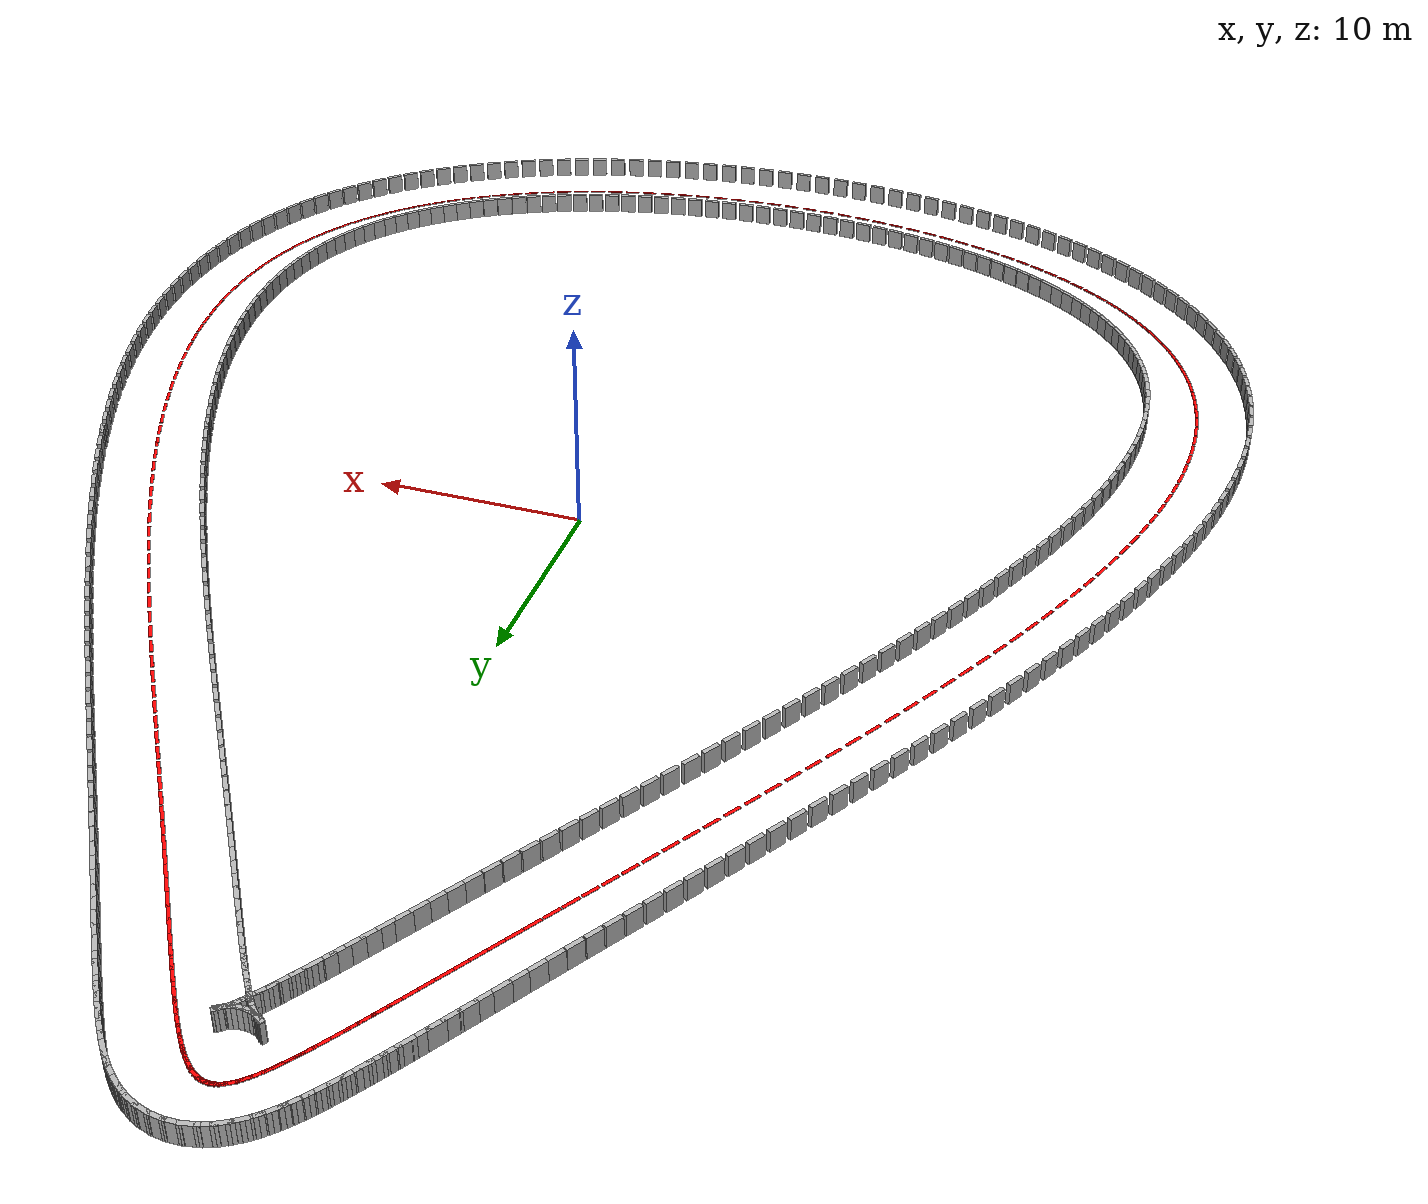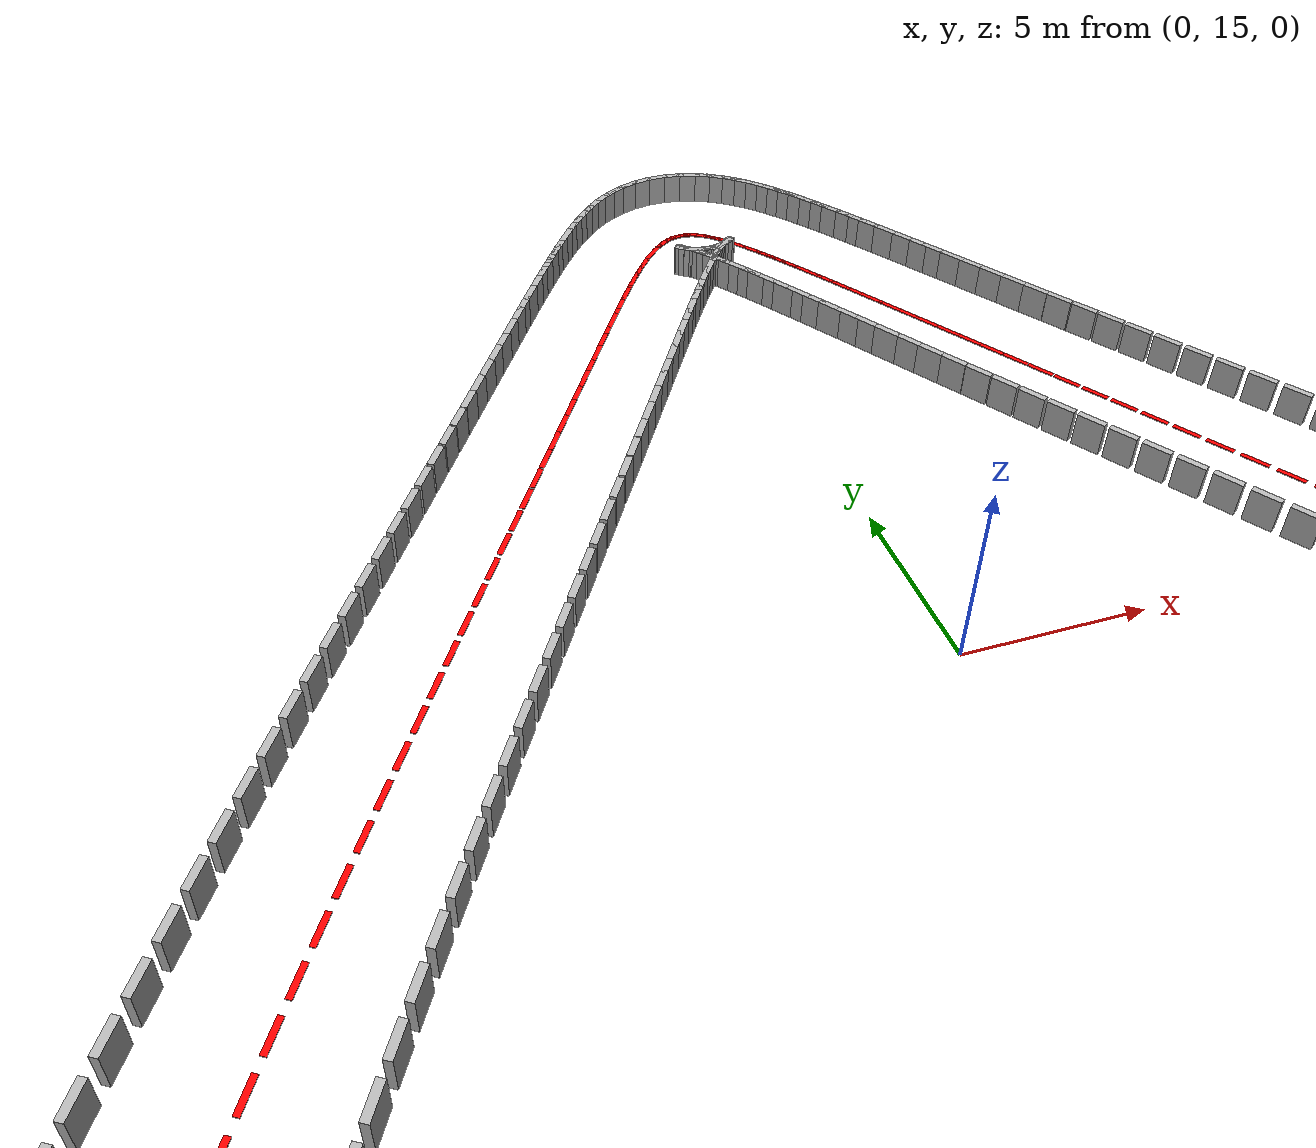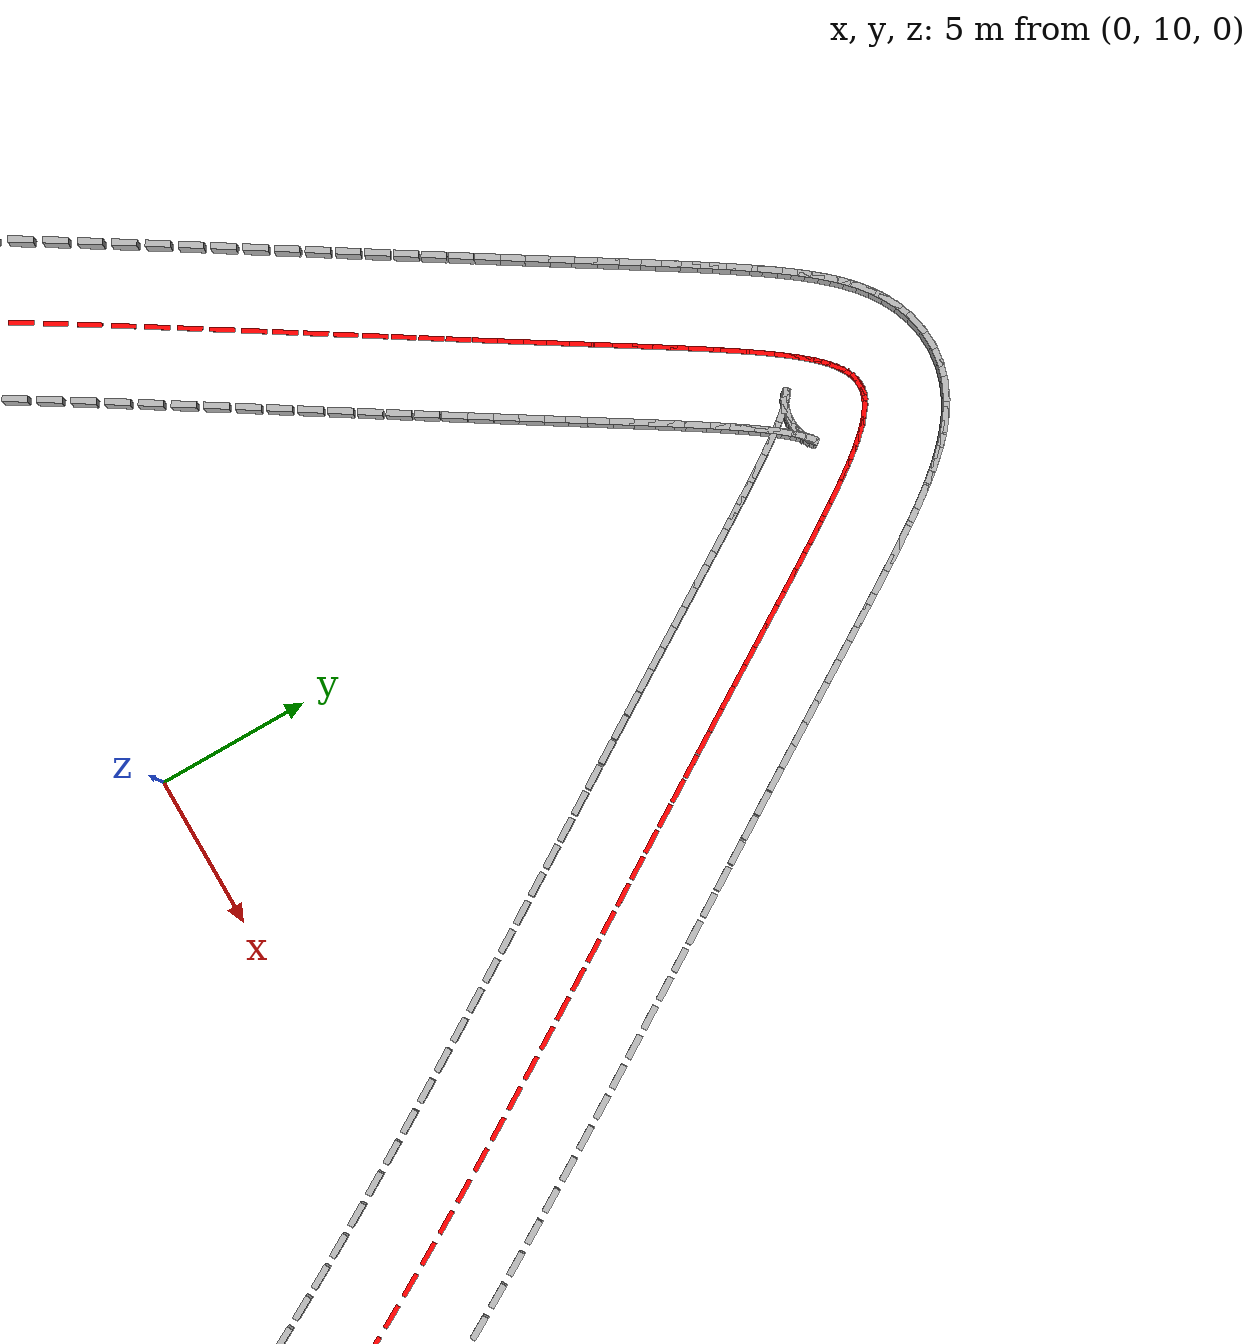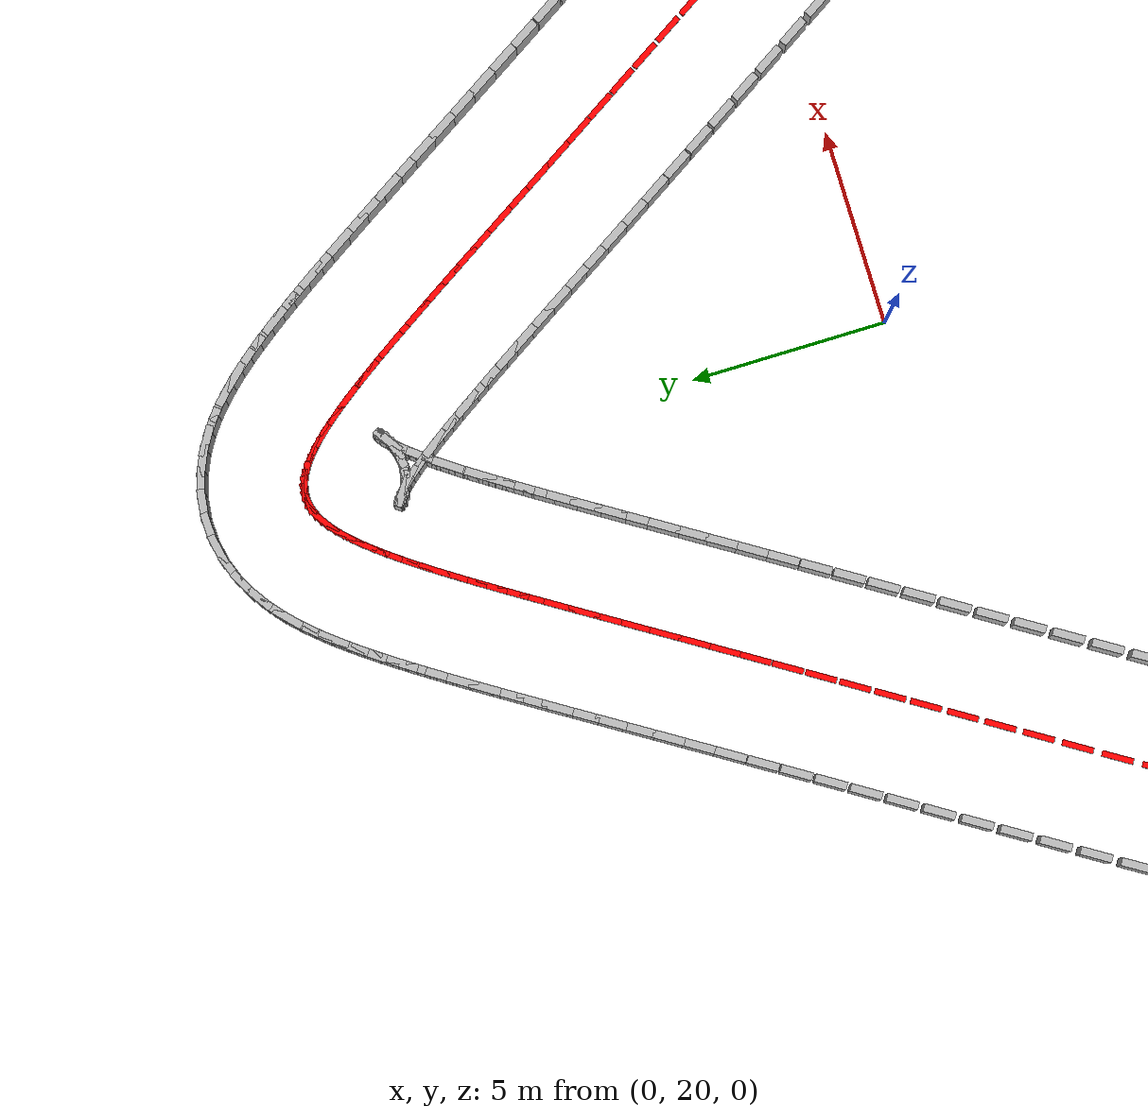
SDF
<?xml version="1.0" ?>
<sdf version="1.7">
<model name="track_walls">
<static>true</static>

    <link name="left_0">
      <pose>24.282 1.022 0.5 0 0 -1.150</pose>
      <collision name="c">
        <geometry>
          <box><size>0.8 0.2 1.0</size></box>
        </geometry>
      </collision>
      <visual name="v">
        <geometry>
          <box><size>0.8 0.2 1.0</size></box>
        </geometry>
      </visual>
    </link>

    <link name="right_0">
      <pose>19.718 -1.022 0.5 0 0 -1.150</pose>
      <collision name="c">
        <geometry>
          <box><size>0.8 0.2 1.0</size></box>
        </geometry>
      </collision>
      <visual name="v">
        <geometry>
          <box><size>0.8 0.2 1.0</size></box>
        </geometry>
      </visual>
    </link>

    <link name="center_0">
      <pose>22.000 -0.000 0.010 0 0 -1.150</pose>
      <visual name="v">
        <geometry>
          <box><size>0.8 0.15 0.02</size></box>
        </geometry>
        <material>
          <ambient>1 0 0 1</ambient>
          <diffuse>1 0 0 1</diffuse>
        </material>
      </visual>
    </link>

    <link name="left_1">
      <pose>24.739 -0.000 0.5 0 0 -1.158</pose>
      <collision name="c">
        <geometry>
          <box><size>0.8 0.2 1.0</size></box>
        </geometry>
      </collision>
      <visual name="v">
        <geometry>
          <box><size>0.8 0.2 1.0</size></box>
        </geometry>
      </visual>
    </link>

    <link name="right_1">
      <pose>20.160 -2.008 0.5 0 0 -1.158</pose>
      <collision name="c">
        <geometry>
          <box><size>0.8 0.2 1.0</size></box>
        </geometry>
      </collision>
      <visual name="v">
        <geometry>
          <box><size>0.8 0.2 1.0</size></box>
        </geometry>
      </visual>
    </link>

    <link name="center_1">
      <pose>22.450 -1.004 0.010 0 0 -1.158</pose>
      <visual name="v">
        <geometry>
          <box><size>0.8 0.15 0.02</size></box>
        </geometry>
        <material>
          <ambient>1 0 0 1</ambient>
          <diffuse>1 0 0 1</diffuse>
        </material>
      </visual>
    </link>

    <link name="left_2">
      <pose>25.186 -1.042 0.5 0 0 -1.174</pose>
      <collision name="c">
        <geometry>
          <box><size>0.8 0.2 1.0</size></box>
        </geometry>
      </collision>
      <visual name="v">
        <geometry>
          <box><size>0.8 0.2 1.0</size></box>
        </geometry>
      </visual>
    </link>

    <link name="right_2">
      <pose>20.574 -2.973 0.5 0 0 -1.174</pose>
      <collision name="c">
        <geometry>
          <box><size>0.8 0.2 1.0</size></box>
        </geometry>
      </collision>
      <visual name="v">
        <geometry>
          <box><size>0.8 0.2 1.0</size></box>
        </geometry>
      </visual>
    </link>

    <link name="center_2">
      <pose>22.880 -2.007 0.010 0 0 -1.174</pose>
      <visual name="v">
        <geometry>
          <box><size>0.8 0.15 0.02</size></box>
        </geometry>
        <material>
          <ambient>1 0 0 1</ambient>
          <diffuse>1 0 0 1</diffuse>
        </material>
      </visual>
    </link>

    <link name="left_3">
      <pose>25.612 -2.085 0.5 0 0 -1.192</pose>
      <collision name="c">
        <geometry>
          <box><size>0.8 0.2 1.0</size></box>
        </geometry>
      </collision>
      <visual name="v">
        <geometry>
          <box><size>0.8 0.2 1.0</size></box>
        </geometry>
      </visual>
    </link>

    <link name="right_3">
      <pose>20.966 -3.933 0.5 0 0 -1.192</pose>
      <collision name="c">
        <geometry>
          <box><size>0.8 0.2 1.0</size></box>
        </geometry>
      </collision>
      <visual name="v">
        <geometry>
          <box><size>0.8 0.2 1.0</size></box>
        </geometry>
      </visual>
    </link>

    <link name="center_3">
      <pose>23.289 -3.009 0.010 0 0 -1.192</pose>
      <visual name="v">
        <geometry>
          <box><size>0.8 0.15 0.02</size></box>
        </geometry>
        <material>
          <ambient>1 0 0 1</ambient>
          <diffuse>1 0 0 1</diffuse>
        </material>
      </visual>
    </link>

    <link name="left_4">
      <pose>26.016 -3.129 0.5 0 0 -1.212</pose>
      <collision name="c">
        <geometry>
          <box><size>0.8 0.2 1.0</size></box>
        </geometry>
      </collision>
      <visual name="v">
        <geometry>
          <box><size>0.8 0.2 1.0</size></box>
        </geometry>
      </visual>
    </link>

    <link name="right_4">
      <pose>21.335 -4.887 0.5 0 0 -1.212</pose>
      <collision name="c">
        <geometry>
          <box><size>0.8 0.2 1.0</size></box>
        </geometry>
      </collision>
      <visual name="v">
        <geometry>
          <box><size>0.8 0.2 1.0</size></box>
        </geometry>
      </visual>
    </link>

    <link name="center_4">
      <pose>23.675 -4.008 0.010 0 0 -1.212</pose>
      <visual name="v">
        <geometry>
          <box><size>0.8 0.15 0.02</size></box>
        </geometry>
        <material>
          <ambient>1 0 0 1</ambient>
          <diffuse>1 0 0 1</diffuse>
        </material>
      </visual>
    </link>

    <link name="left_5">
      <pose>26.396 -4.173 0.5 0 0 -1.232</pose>
      <collision name="c">
        <geometry>
          <box><size>0.8 0.2 1.0</size></box>
        </geometry>
      </collision>
      <visual name="v">
        <geometry>
          <box><size>0.8 0.2 1.0</size></box>
        </geometry>
      </visual>
    </link>

    <link name="right_5">
      <pose>21.680 -5.834 0.5 0 0 -1.232</pose>
      <collision name="c">
        <geometry>
          <box><size>0.8 0.2 1.0</size></box>
        </geometry>
      </collision>
      <visual name="v">
        <geometry>
          <box><size>0.8 0.2 1.0</size></box>
        </geometry>
      </visual>
    </link>

    <link name="center_5">
      <pose>24.038 -5.004 0.010 0 0 -1.232</pose>
      <visual name="v">
        <geometry>
          <box><size>0.8 0.15 0.02</size></box>
        </geometry>
        <material>
          <ambient>1 0 0 1</ambient>
          <diffuse>1 0 0 1</diffuse>
        </material>
      </visual>
    </link>

    <link name="left_6">
      <pose>26.751 -5.218 0.5 0 0 -1.254</pose>
      <collision name="c">
        <geometry>
          <box><size>0.8 0.2 1.0</size></box>
        </geometry>
      </collision>
      <visual name="v">
        <geometry>
          <box><size>0.8 0.2 1.0</size></box>
        </geometry>
      </visual>
    </link>

    <link name="right_6">
      <pose>21.999 -6.773 0.5 0 0 -1.254</pose>
      <collision name="c">
        <geometry>
          <box><size>0.8 0.2 1.0</size></box>
        </geometry>
      </collision>
      <visual name="v">
        <geometry>
          <box><size>0.8 0.2 1.0</size></box>
        </geometry>
      </visual>
    </link>

    <link name="center_6">
      <pose>24.375 -5.995 0.010 0 0 -1.254</pose>
      <visual name="v">
        <geometry>
          <box><size>0.8 0.15 0.02</size></box>
        </geometry>
        <material>
          <ambient>1 0 0 1</ambient>
          <diffuse>1 0 0 1</diffuse>
        </material>
      </visual>
    </link>

    <link name="left_7">
      <pose>27.079 -6.261 0.5 0 0 -1.278</pose>
      <collision name="c">
        <geometry>
          <box><size>0.8 0.2 1.0</size></box>
        </geometry>
      </collision>
      <visual name="v">
        <geometry>
          <box><size>0.8 0.2 1.0</size></box>
        </geometry>
      </visual>
    </link>

    <link name="right_7">
      <pose>22.292 -7.703 0.5 0 0 -1.278</pose>
      <collision name="c">
        <geometry>
          <box><size>0.8 0.2 1.0</size></box>
        </geometry>
      </collision>
      <visual name="v">
        <geometry>
          <box><size>0.8 0.2 1.0</size></box>
        </geometry>
      </visual>
    </link>

    <link name="center_7">
      <pose>24.685 -6.982 0.010 0 0 -1.278</pose>
      <visual name="v">
        <geometry>
          <box><size>0.8 0.15 0.02</size></box>
        </geometry>
        <material>
          <ambient>1 0 0 1</ambient>
          <diffuse>1 0 0 1</diffuse>
        </material>
      </visual>
    </link>

    <link name="left_8">
      <pose>27.379 -7.303 0.5 0 0 -1.304</pose>
      <collision name="c">
        <geometry>
          <box><size>0.8 0.2 1.0</size></box>
        </geometry>
      </collision>
      <visual name="v">
        <geometry>
          <box><size>0.8 0.2 1.0</size></box>
        </geometry>
      </visual>
    </link>

    <link name="right_8">
      <pose>22.557 -8.623 0.5 0 0 -1.304</pose>
      <collision name="c">
        <geometry>
          <box><size>0.8 0.2 1.0</size></box>
        </geometry>
      </collision>
      <visual name="v">
        <geometry>
          <box><size>0.8 0.2 1.0</size></box>
        </geometry>
      </visual>
    </link>

    <link name="center_8">
      <pose>24.968 -7.963 0.010 0 0 -1.304</pose>
      <visual name="v">
        <geometry>
          <box><size>0.8 0.15 0.02</size></box>
        </geometry>
        <material>
          <ambient>1 0 0 1</ambient>
          <diffuse>1 0 0 1</diffuse>
        </material>
      </visual>
    </link>

    <link name="left_9">
      <pose>27.649 -8.343 0.5 0 0 -1.331</pose>
      <collision name="c">
        <geometry>
          <box><size>0.8 0.2 1.0</size></box>
        </geometry>
      </collision>
      <visual name="v">
        <geometry>
          <box><size>0.8 0.2 1.0</size></box>
        </geometry>
      </visual>
    </link>

    <link name="right_9">
      <pose>22.793 -9.532 0.5 0 0 -1.331</pose>
      <collision name="c">
        <geometry>
          <box><size>0.8 0.2 1.0</size></box>
        </geometry>
      </collision>
      <visual name="v">
        <geometry>
          <box><size>0.8 0.2 1.0</size></box>
        </geometry>
      </visual>
    </link>

    <link name="center_9">
      <pose>25.221 -8.937 0.010 0 0 -1.331</pose>
      <visual name="v">
        <geometry>
          <box><size>0.8 0.15 0.02</size></box>
        </geometry>
        <material>
          <ambient>1 0 0 1</ambient>
          <diffuse>1 0 0 1</diffuse>
        </material>
      </visual>
    </link>

    <link name="left_10">
      <pose>27.888 -9.380 0.5 0 0 -1.359</pose>
      <collision name="c">
        <geometry>
          <box><size>0.8 0.2 1.0</size></box>
        </geometry>
      </collision>
      <visual name="v">
        <geometry>
          <box><size>0.8 0.2 1.0</size></box>
        </geometry>
      </visual>
    </link>

    <link name="right_10">
      <pose>22.999 -10.429 0.5 0 0 -1.359</pose>
      <collision name="c">
        <geometry>
          <box><size>0.8 0.2 1.0</size></box>
        </geometry>
      </collision>
      <visual name="v">
        <geometry>
          <box><size>0.8 0.2 1.0</size></box>
        </geometry>
      </visual>
    </link>

    <link name="center_10">
      <pose>25.443 -9.904 0.010 0 0 -1.359</pose>
      <visual name="v">
        <geometry>
          <box><size>0.8 0.15 0.02</size></box>
        </geometry>
        <material>
          <ambient>1 0 0 1</ambient>
          <diffuse>1 0 0 1</diffuse>
        </material>
      </visual>
    </link>

    <link name="left_11">
      <pose>28.094 -10.414 0.5 0 0 -1.390</pose>
      <collision name="c">
        <geometry>
          <box><size>0.8 0.2 1.0</size></box>
        </geometry>
      </collision>
      <visual name="v">
        <geometry>
          <box><size>0.8 0.2 1.0</size></box>
        </geometry>
      </visual>
    </link>

    <link name="right_11">
      <pose>23.175 -11.313 0.5 0 0 -1.390</pose>
      <collision name="c">
        <geometry>
          <box><size>0.8 0.2 1.0</size></box>
        </geometry>
      </collision>
      <visual name="v">
        <geometry>
          <box><size>0.8 0.2 1.0</size></box>
        </geometry>
      </visual>
    </link>

    <link name="center_11">
      <pose>25.634 -10.863 0.010 0 0 -1.390</pose>
      <visual name="v">
        <geometry>
          <box><size>0.8 0.15 0.02</size></box>
        </geometry>
        <material>
          <ambient>1 0 0 1</ambient>
          <diffuse>1 0 0 1</diffuse>
        </material>
      </visual>
    </link>

    <link name="left_12">
      <pose>28.265 -11.444 0.5 0 0 -1.422</pose>
      <collision name="c">
        <geometry>
          <box><size>0.8 0.2 1.0</size></box>
        </geometry>
      </collision>
      <visual name="v">
        <geometry>
          <box><size>0.8 0.2 1.0</size></box>
        </geometry>
      </visual>
    </link>

    <link name="right_12">
      <pose>23.320 -12.183 0.5 0 0 -1.422</pose>
      <collision name="c">
        <geometry>
          <box><size>0.8 0.2 1.0</size></box>
        </geometry>
      </collision>
      <visual name="v">
        <geometry>
          <box><size>0.8 0.2 1.0</size></box>
        </geometry>
      </visual>
    </link>

    <link name="center_12">
      <pose>25.792 -11.813 0.010 0 0 -1.422</pose>
      <visual name="v">
        <geometry>
          <box><size>0.8 0.15 0.02</size></box>
        </geometry>
        <material>
          <ambient>1 0 0 1</ambient>
          <diffuse>1 0 0 1</diffuse>
        </material>
      </visual>
    </link>

    <link name="left_13">
      <pose>28.401 -12.469 0.5 0 0 -1.457</pose>
      <collision name="c">
        <geometry>
          <box><size>0.8 0.2 1.0</size></box>
        </geometry>
      </collision>
      <visual name="v">
        <geometry>
          <box><size>0.8 0.2 1.0</size></box>
        </geometry>
      </visual>
    </link>

    <link name="right_13">
      <pose>23.433 -13.038 0.5 0 0 -1.457</pose>
      <collision name="c">
        <geometry>
          <box><size>0.8 0.2 1.0</size></box>
        </geometry>
      </collision>
      <visual name="v">
        <geometry>
          <box><size>0.8 0.2 1.0</size></box>
        </geometry>
      </visual>
    </link>

    <link name="center_13">
      <pose>25.917 -12.754 0.010 0 0 -1.457</pose>
      <visual name="v">
        <geometry>
          <box><size>0.8 0.15 0.02</size></box>
        </geometry>
        <material>
          <ambient>1 0 0 1</ambient>
          <diffuse>1 0 0 1</diffuse>
        </material>
      </visual>
    </link>

    <link name="left_14">
      <pose>28.499 -13.490 0.5 0 0 -1.493</pose>
      <collision name="c">
        <geometry>
          <box><size>0.8 0.2 1.0</size></box>
        </geometry>
      </collision>
      <visual name="v">
        <geometry>
          <box><size>0.8 0.2 1.0</size></box>
        </geometry>
      </visual>
    </link>

    <link name="right_14">
      <pose>23.514 -13.877 0.5 0 0 -1.493</pose>
      <collision name="c">
        <geometry>
          <box><size>0.8 0.2 1.0</size></box>
        </geometry>
      </collision>
      <visual name="v">
        <geometry>
          <box><size>0.8 0.2 1.0</size></box>
        </geometry>
      </visual>
    </link>

    <link name="center_14">
      <pose>26.006 -13.683 0.010 0 0 -1.493</pose>
      <visual name="v">
        <geometry>
          <box><size>0.8 0.15 0.02</size></box>
        </geometry>
        <material>
          <ambient>1 0 0 1</ambient>
          <diffuse>1 0 0 1</diffuse>
        </material>
      </visual>
    </link>

    <link name="left_15">
      <pose>28.559 -14.504 0.5 0 0 -1.532</pose>
      <collision name="c">
        <geometry>
          <box><size>0.8 0.2 1.0</size></box>
        </geometry>
      </collision>
      <visual name="v">
        <geometry>
          <box><size>0.8 0.2 1.0</size></box>
        </geometry>
      </visual>
    </link>

    <link name="right_15">
      <pose>23.562 -14.700 0.5 0 0 -1.532</pose>
      <collision name="c">
        <geometry>
          <box><size>0.8 0.2 1.0</size></box>
        </geometry>
      </collision>
      <visual name="v">
        <geometry>
          <box><size>0.8 0.2 1.0</size></box>
        </geometry>
      </visual>
    </link>

    <link name="center_15">
      <pose>26.060 -14.602 0.010 0 0 -1.532</pose>
      <visual name="v">
        <geometry>
          <box><size>0.8 0.15 0.02</size></box>
        </geometry>
        <material>
          <ambient>1 0 0 1</ambient>
          <diffuse>1 0 0 1</diffuse>
        </material>
      </visual>
    </link>

    <link name="left_16">
      <pose>28.578 -15.511 0.5 0 0 -1.572</pose>
      <collision name="c">
        <geometry>
          <box><size>0.8 0.2 1.0</size></box>
        </geometry>
      </collision>
      <visual name="v">
        <geometry>
          <box><size>0.8 0.2 1.0</size></box>
        </geometry>
      </visual>
    </link>

    <link name="right_16">
      <pose>23.578 -15.505 0.5 0 0 -1.572</pose>
      <collision name="c">
        <geometry>
          <box><size>0.8 0.2 1.0</size></box>
        </geometry>
      </collision>
      <visual name="v">
        <geometry>
          <box><size>0.8 0.2 1.0</size></box>
        </geometry>
      </visual>
    </link>

    <link name="center_16">
      <pose>26.078 -15.508 0.010 0 0 -1.572</pose>
      <visual name="v">
        <geometry>
          <box><size>0.8 0.15 0.02</size></box>
        </geometry>
        <material>
          <ambient>1 0 0 1</ambient>
          <diffuse>1 0 0 1</diffuse>
        </material>
      </visual>
    </link>

    <link name="left_17">
      <pose>28.556 -16.510 0.5 0 0 -1.614</pose>
      <collision name="c">
        <geometry>
          <box><size>0.8 0.2 1.0</size></box>
        </geometry>
      </collision>
      <visual name="v">
        <geometry>
          <box><size>0.8 0.2 1.0</size></box>
        </geometry>
      </visual>
    </link>

    <link name="right_17">
      <pose>23.561 -16.294 0.5 0 0 -1.614</pose>
      <collision name="c">
        <geometry>
          <box><size>0.8 0.2 1.0</size></box>
        </geometry>
      </collision>
      <visual name="v">
        <geometry>
          <box><size>0.8 0.2 1.0</size></box>
        </geometry>
      </visual>
    </link>

    <link name="center_17">
      <pose>26.058 -16.402 0.010 0 0 -1.614</pose>
      <visual name="v">
        <geometry>
          <box><size>0.8 0.15 0.02</size></box>
        </geometry>
        <material>
          <ambient>1 0 0 1</ambient>
          <diffuse>1 0 0 1</diffuse>
        </material>
      </visual>
    </link>

    <link name="left_18">
      <pose>28.492 -17.500 0.5 0 0 -1.658</pose>
      <collision name="c">
        <geometry>
          <box><size>0.8 0.2 1.0</size></box>
        </geometry>
      </collision>
      <visual name="v">
        <geometry>
          <box><size>0.8 0.2 1.0</size></box>
        </geometry>
      </visual>
    </link>

    <link name="right_18">
      <pose>23.511 -17.064 0.5 0 0 -1.658</pose>
      <collision name="c">
        <geometry>
          <box><size>0.8 0.2 1.0</size></box>
        </geometry>
      </collision>
      <visual name="v">
        <geometry>
          <box><size>0.8 0.2 1.0</size></box>
        </geometry>
      </visual>
    </link>

    <link name="center_18">
      <pose>26.001 -17.282 0.010 0 0 -1.658</pose>
      <visual name="v">
        <geometry>
          <box><size>0.8 0.15 0.02</size></box>
        </geometry>
        <material>
          <ambient>1 0 0 1</ambient>
          <diffuse>1 0 0 1</diffuse>
        </material>
      </visual>
    </link>

    <link name="left_19">
      <pose>28.383 -18.480 0.5 0 0 -1.704</pose>
      <collision name="c">
        <geometry>
          <box><size>0.8 0.2 1.0</size></box>
        </geometry>
      </collision>
      <visual name="v">
        <geometry>
          <box><size>0.8 0.2 1.0</size></box>
        </geometry>
      </visual>
    </link>

    <link name="right_19">
      <pose>23.428 -17.816 0.5 0 0 -1.704</pose>
      <collision name="c">
        <geometry>
          <box><size>0.8 0.2 1.0</size></box>
        </geometry>
      </collision>
      <visual name="v">
        <geometry>
          <box><size>0.8 0.2 1.0</size></box>
        </geometry>
      </visual>
    </link>

    <link name="center_19">
      <pose>25.905 -18.148 0.010 0 0 -1.704</pose>
      <visual name="v">
        <geometry>
          <box><size>0.8 0.15 0.02</size></box>
        </geometry>
        <material>
          <ambient>1 0 0 1</ambient>
          <diffuse>1 0 0 1</diffuse>
        </material>
      </visual>
    </link>

    <link name="left_20">
      <pose>28.230 -19.449 0.5 0 0 -1.752</pose>
      <collision name="c">
        <geometry>
          <box><size>0.8 0.2 1.0</size></box>
        </geometry>
      </collision>
      <visual name="v">
        <geometry>
          <box><size>0.8 0.2 1.0</size></box>
        </geometry>
      </visual>
    </link>

    <link name="right_20">
      <pose>23.312 -18.550 0.5 0 0 -1.752</pose>
      <collision name="c">
        <geometry>
          <box><size>0.8 0.2 1.0</size></box>
        </geometry>
      </collision>
      <visual name="v">
        <geometry>
          <box><size>0.8 0.2 1.0</size></box>
        </geometry>
      </visual>
    </link>

    <link name="center_20">
      <pose>25.771 -18.999 0.010 0 0 -1.752</pose>
      <visual name="v">
        <geometry>
          <box><size>0.8 0.15 0.02</size></box>
        </geometry>
        <material>
          <ambient>1 0 0 1</ambient>
          <diffuse>1 0 0 1</diffuse>
        </material>
      </visual>
    </link>

    <link name="left_21">
      <pose>28.031 -20.404 0.5 0 0 -1.801</pose>
      <collision name="c">
        <geometry>
          <box><size>0.8 0.2 1.0</size></box>
        </geometry>
      </collision>
      <visual name="v">
        <geometry>
          <box><size>0.8 0.2 1.0</size></box>
        </geometry>
      </visual>
    </link>

    <link name="right_21">
      <pose>23.163 -19.265 0.5 0 0 -1.801</pose>
      <collision name="c">
        <geometry>
          <box><size>0.8 0.2 1.0</size></box>
        </geometry>
      </collision>
      <visual name="v">
        <geometry>
          <box><size>0.8 0.2 1.0</size></box>
        </geometry>
      </visual>
    </link>

    <link name="center_21">
      <pose>25.597 -19.835 0.010 0 0 -1.801</pose>
      <visual name="v">
        <geometry>
          <box><size>0.8 0.15 0.02</size></box>
        </geometry>
        <material>
          <ambient>1 0 0 1</ambient>
          <diffuse>1 0 0 1</diffuse>
        </material>
      </visual>
    </link>

    <link name="left_22">
      <pose>27.786 -21.345 0.5 0 0 -1.851</pose>
      <collision name="c">
        <geometry>
          <box><size>0.8 0.2 1.0</size></box>
        </geometry>
      </collision>
      <visual name="v">
        <geometry>
          <box><size>0.8 0.2 1.0</size></box>
        </geometry>
      </visual>
    </link>

    <link name="right_22">
      <pose>22.981 -19.963 0.5 0 0 -1.851</pose>
      <collision name="c">
        <geometry>
          <box><size>0.8 0.2 1.0</size></box>
        </geometry>
      </collision>
      <visual name="v">
        <geometry>
          <box><size>0.8 0.2 1.0</size></box>
        </geometry>
      </visual>
    </link>

    <link name="center_22">
      <pose>25.384 -20.654 0.010 0 0 -1.851</pose>
      <visual name="v">
        <geometry>
          <box><size>0.8 0.15 0.02</size></box>
        </geometry>
        <material>
          <ambient>1 0 0 1</ambient>
          <diffuse>1 0 0 1</diffuse>
        </material>
      </visual>
    </link>

    <link name="left_23">
      <pose>27.495 -22.269 0.5 0 0 -1.902</pose>
      <collision name="c">
        <geometry>
          <box><size>0.8 0.2 1.0</size></box>
        </geometry>
      </collision>
      <visual name="v">
        <geometry>
          <box><size>0.8 0.2 1.0</size></box>
        </geometry>
      </visual>
    </link>

    <link name="right_23">
      <pose>22.767 -20.642 0.5 0 0 -1.902</pose>
      <collision name="c">
        <geometry>
          <box><size>0.8 0.2 1.0</size></box>
        </geometry>
      </collision>
      <visual name="v">
        <geometry>
          <box><size>0.8 0.2 1.0</size></box>
        </geometry>
      </visual>
    </link>

    <link name="center_23">
      <pose>25.131 -21.456 0.010 0 0 -1.902</pose>
      <visual name="v">
        <geometry>
          <box><size>0.8 0.15 0.02</size></box>
        </geometry>
        <material>
          <ambient>1 0 0 1</ambient>
          <diffuse>1 0 0 1</diffuse>
        </material>
      </visual>
    </link>

    <link name="left_24">
      <pose>27.156 -23.175 0.5 0 0 -1.954</pose>
      <collision name="c">
        <geometry>
          <box><size>0.8 0.2 1.0</size></box>
        </geometry>
      </collision>
      <visual name="v">
        <geometry>
          <box><size>0.8 0.2 1.0</size></box>
        </geometry>
      </visual>
    </link>

    <link name="right_24">
      <pose>22.519 -21.305 0.5 0 0 -1.954</pose>
      <collision name="c">
        <geometry>
          <box><size>0.8 0.2 1.0</size></box>
        </geometry>
      </collision>
      <visual name="v">
        <geometry>
          <box><size>0.8 0.2 1.0</size></box>
        </geometry>
      </visual>
    </link>

    <link name="center_24">
      <pose>24.838 -22.240 0.010 0 0 -1.954</pose>
      <visual name="v">
        <geometry>
          <box><size>0.8 0.15 0.02</size></box>
        </geometry>
        <material>
          <ambient>1 0 0 1</ambient>
          <diffuse>1 0 0 1</diffuse>
        </material>
      </visual>
    </link>

    <link name="left_25">
      <pose>26.771 -24.062 0.5 0 0 -2.007</pose>
      <collision name="c">
        <geometry>
          <box><size>0.8 0.2 1.0</size></box>
        </geometry>
      </collision>
      <visual name="v">
        <geometry>
          <box><size>0.8 0.2 1.0</size></box>
        </geometry>
      </visual>
    </link>

    <link name="right_25">
      <pose>22.239 -21.950 0.5 0 0 -2.007</pose>
      <collision name="c">
        <geometry>
          <box><size>0.8 0.2 1.0</size></box>
        </geometry>
      </collision>
      <visual name="v">
        <geometry>
          <box><size>0.8 0.2 1.0</size></box>
        </geometry>
      </visual>
    </link>

    <link name="center_25">
      <pose>24.505 -23.006 0.010 0 0 -2.007</pose>
      <visual name="v">
        <geometry>
          <box><size>0.8 0.15 0.02</size></box>
        </geometry>
        <material>
          <ambient>1 0 0 1</ambient>
          <diffuse>1 0 0 1</diffuse>
        </material>
      </visual>
    </link>

    <link name="left_26">
      <pose>26.340 -24.927 0.5 0 0 -2.060</pose>
      <collision name="c">
        <geometry>
          <box><size>0.8 0.2 1.0</size></box>
        </geometry>
      </collision>
      <visual name="v">
        <geometry>
          <box><size>0.8 0.2 1.0</size></box>
        </geometry>
      </visual>
    </link>

    <link name="right_26">
      <pose>21.926 -22.580 0.5 0 0 -2.060</pose>
      <collision name="c">
        <geometry>
          <box><size>0.8 0.2 1.0</size></box>
        </geometry>
      </collision>
      <visual name="v">
        <geometry>
          <box><size>0.8 0.2 1.0</size></box>
        </geometry>
      </visual>
    </link>

    <link name="center_26">
      <pose>24.133 -23.753 0.010 0 0 -2.060</pose>
      <visual name="v">
        <geometry>
          <box><size>0.8 0.15 0.02</size></box>
        </geometry>
        <material>
          <ambient>1 0 0 1</ambient>
          <diffuse>1 0 0 1</diffuse>
        </material>
      </visual>
    </link>

    <link name="left_27">
      <pose>25.863 -25.770 0.5 0 0 -2.112</pose>
      <collision name="c">
        <geometry>
          <box><size>0.8 0.2 1.0</size></box>
        </geometry>
      </collision>
      <visual name="v">
        <geometry>
          <box><size>0.8 0.2 1.0</size></box>
        </geometry>
      </visual>
    </link>

    <link name="right_27">
      <pose>21.579 -23.193 0.5 0 0 -2.112</pose>
      <collision name="c">
        <geometry>
          <box><size>0.8 0.2 1.0</size></box>
        </geometry>
      </collision>
      <visual name="v">
        <geometry>
          <box><size>0.8 0.2 1.0</size></box>
        </geometry>
      </visual>
    </link>

    <link name="center_27">
      <pose>23.721 -24.481 0.010 0 0 -2.112</pose>
      <visual name="v">
        <geometry>
          <box><size>0.8 0.15 0.02</size></box>
        </geometry>
        <material>
          <ambient>1 0 0 1</ambient>
          <diffuse>1 0 0 1</diffuse>
        </material>
      </visual>
    </link>

    <link name="left_28">
      <pose>25.342 -26.587 0.5 0 0 -2.165</pose>
      <collision name="c">
        <geometry>
          <box><size>0.8 0.2 1.0</size></box>
        </geometry>
      </collision>
      <visual name="v">
        <geometry>
          <box><size>0.8 0.2 1.0</size></box>
        </geometry>
      </visual>
    </link>

    <link name="right_28">
      <pose>21.198 -23.790 0.5 0 0 -2.165</pose>
      <collision name="c">
        <geometry>
          <box><size>0.8 0.2 1.0</size></box>
        </geometry>
      </collision>
      <visual name="v">
        <geometry>
          <box><size>0.8 0.2 1.0</size></box>
        </geometry>
      </visual>
    </link>

    <link name="center_28">
      <pose>23.270 -25.189 0.010 0 0 -2.165</pose>
      <visual name="v">
        <geometry>
          <box><size>0.8 0.15 0.02</size></box>
        </geometry>
        <material>
          <ambient>1 0 0 1</ambient>
          <diffuse>1 0 0 1</diffuse>
        </material>
      </visual>
    </link>

    <link name="left_29">
      <pose>24.777 -27.379 0.5 0 0 -2.216</pose>
      <collision name="c">
        <geometry>
          <box><size>0.8 0.2 1.0</size></box>
        </geometry>
      </collision>
      <visual name="v">
        <geometry>
          <box><size>0.8 0.2 1.0</size></box>
        </geometry>
      </visual>
    </link>

    <link name="right_29">
      <pose>20.783 -24.371 0.5 0 0 -2.216</pose>
      <collision name="c">
        <geometry>
          <box><size>0.8 0.2 1.0</size></box>
        </geometry>
      </collision>
      <visual name="v">
        <geometry>
          <box><size>0.8 0.2 1.0</size></box>
        </geometry>
      </visual>
    </link>

    <link name="center_29">
      <pose>22.780 -25.875 0.010 0 0 -2.216</pose>
      <visual name="v">
        <geometry>
          <box><size>0.8 0.15 0.02</size></box>
        </geometry>
        <material>
          <ambient>1 0 0 1</ambient>
          <diffuse>1 0 0 1</diffuse>
        </material>
      </visual>
    </link>

    <link name="left_30">
      <pose>24.169 -28.145 0.5 0 0 -2.267</pose>
      <collision name="c">
        <geometry>
          <box><size>0.8 0.2 1.0</size></box>
        </geometry>
      </collision>
      <visual name="v">
        <geometry>
          <box><size>0.8 0.2 1.0</size></box>
        </geometry>
      </visual>
    </link>

    <link name="right_30">
      <pose>20.333 -24.937 0.5 0 0 -2.267</pose>
      <collision name="c">
        <geometry>
          <box><size>0.8 0.2 1.0</size></box>
        </geometry>
      </collision>
      <visual name="v">
        <geometry>
          <box><size>0.8 0.2 1.0</size></box>
        </geometry>
      </visual>
    </link>

    <link name="center_30">
      <pose>22.251 -26.541 0.010 0 0 -2.267</pose>
      <visual name="v">
        <geometry>
          <box><size>0.8 0.15 0.02</size></box>
        </geometry>
        <material>
          <ambient>1 0 0 1</ambient>
          <diffuse>1 0 0 1</diffuse>
        </material>
      </visual>
    </link>

    <link name="left_31">
      <pose>23.520 -28.882 0.5 0 0 -2.317</pose>
      <collision name="c">
        <geometry>
          <box><size>0.8 0.2 1.0</size></box>
        </geometry>
      </collision>
      <visual name="v">
        <geometry>
          <box><size>0.8 0.2 1.0</size></box>
        </geometry>
      </visual>
    </link>

    <link name="right_31">
      <pose>19.850 -25.487 0.5 0 0 -2.317</pose>
      <collision name="c">
        <geometry>
          <box><size>0.8 0.2 1.0</size></box>
        </geometry>
      </collision>
      <visual name="v">
        <geometry>
          <box><size>0.8 0.2 1.0</size></box>
        </geometry>
      </visual>
    </link>

    <link name="center_31">
      <pose>21.685 -27.184 0.010 0 0 -2.317</pose>
      <visual name="v">
        <geometry>
          <box><size>0.8 0.15 0.02</size></box>
        </geometry>
        <material>
          <ambient>1 0 0 1</ambient>
          <diffuse>1 0 0 1</diffuse>
        </material>
      </visual>
    </link>

    <link name="left_32">
      <pose>22.832 -29.590 0.5 0 0 -2.366</pose>
      <collision name="c">
        <geometry>
          <box><size>0.8 0.2 1.0</size></box>
        </geometry>
      </collision>
      <visual name="v">
        <geometry>
          <box><size>0.8 0.2 1.0</size></box>
        </geometry>
      </visual>
    </link>

    <link name="right_32">
      <pose>19.331 -26.021 0.5 0 0 -2.366</pose>
      <collision name="c">
        <geometry>
          <box><size>0.8 0.2 1.0</size></box>
        </geometry>
      </collision>
      <visual name="v">
        <geometry>
          <box><size>0.8 0.2 1.0</size></box>
        </geometry>
      </visual>
    </link>

    <link name="center_32">
      <pose>21.081 -27.806 0.010 0 0 -2.366</pose>
      <visual name="v">
        <geometry>
          <box><size>0.8 0.15 0.02</size></box>
        </geometry>
        <material>
          <ambient>1 0 0 1</ambient>
          <diffuse>1 0 0 1</diffuse>
        </material>
      </visual>
    </link>

    <link name="left_33">
      <pose>22.106 -30.270 0.5 0 0 -2.413</pose>
      <collision name="c">
        <geometry>
          <box><size>0.8 0.2 1.0</size></box>
        </geometry>
      </collision>
      <visual name="v">
        <geometry>
          <box><size>0.8 0.2 1.0</size></box>
        </geometry>
      </visual>
    </link>

    <link name="right_33">
      <pose>18.777 -26.538 0.5 0 0 -2.413</pose>
      <collision name="c">
        <geometry>
          <box><size>0.8 0.2 1.0</size></box>
        </geometry>
      </collision>
      <visual name="v">
        <geometry>
          <box><size>0.8 0.2 1.0</size></box>
        </geometry>
      </visual>
    </link>

    <link name="center_33">
      <pose>20.441 -28.404 0.010 0 0 -2.413</pose>
      <visual name="v">
        <geometry>
          <box><size>0.8 0.15 0.02</size></box>
        </geometry>
        <material>
          <ambient>1 0 0 1</ambient>
          <diffuse>1 0 0 1</diffuse>
        </material>
      </visual>
    </link>

    <link name="left_34">
      <pose>21.343 -30.919 0.5 0 0 -2.459</pose>
      <collision name="c">
        <geometry>
          <box><size>0.8 0.2 1.0</size></box>
        </geometry>
      </collision>
      <visual name="v">
        <geometry>
          <box><size>0.8 0.2 1.0</size></box>
        </geometry>
      </visual>
    </link>

    <link name="right_34">
      <pose>18.189 -27.039 0.5 0 0 -2.459</pose>
      <collision name="c">
        <geometry>
          <box><size>0.8 0.2 1.0</size></box>
        </geometry>
      </collision>
      <visual name="v">
        <geometry>
          <box><size>0.8 0.2 1.0</size></box>
        </geometry>
      </visual>
    </link>

    <link name="center_34">
      <pose>19.766 -28.979 0.010 0 0 -2.459</pose>
      <visual name="v">
        <geometry>
          <box><size>0.8 0.15 0.02</size></box>
        </geometry>
        <material>
          <ambient>1 0 0 1</ambient>
          <diffuse>1 0 0 1</diffuse>
        </material>
      </visual>
    </link>

    <link name="left_35">
      <pose>20.545 -31.538 0.5 0 0 -2.504</pose>
      <collision name="c">
        <geometry>
          <box><size>0.8 0.2 1.0</size></box>
        </geometry>
      </collision>
      <visual name="v">
        <geometry>
          <box><size>0.8 0.2 1.0</size></box>
        </geometry>
      </visual>
    </link>

    <link name="right_35">
      <pose>17.567 -27.522 0.5 0 0 -2.504</pose>
      <collision name="c">
        <geometry>
          <box><size>0.8 0.2 1.0</size></box>
        </geometry>
      </collision>
      <visual name="v">
        <geometry>
          <box><size>0.8 0.2 1.0</size></box>
        </geometry>
      </visual>
    </link>

    <link name="center_35">
      <pose>19.056 -29.530 0.010 0 0 -2.504</pose>
      <visual name="v">
        <geometry>
          <box><size>0.8 0.15 0.02</size></box>
        </geometry>
        <material>
          <ambient>1 0 0 1</ambient>
          <diffuse>1 0 0 1</diffuse>
        </material>
      </visual>
    </link>

    <link name="left_36">
      <pose>19.714 -32.127 0.5 0 0 -2.546</pose>
      <collision name="c">
        <geometry>
          <box><size>0.8 0.2 1.0</size></box>
        </geometry>
      </collision>
      <visual name="v">
        <geometry>
          <box><size>0.8 0.2 1.0</size></box>
        </geometry>
      </visual>
    </link>

    <link name="right_36">
      <pose>16.911 -27.987 0.5 0 0 -2.546</pose>
      <collision name="c">
        <geometry>
          <box><size>0.8 0.2 1.0</size></box>
        </geometry>
      </collision>
      <visual name="v">
        <geometry>
          <box><size>0.8 0.2 1.0</size></box>
        </geometry>
      </visual>
    </link>

    <link name="center_36">
      <pose>18.312 -30.057 0.010 0 0 -2.546</pose>
      <visual name="v">
        <geometry>
          <box><size>0.8 0.15 0.02</size></box>
        </geometry>
        <material>
          <ambient>1 0 0 1</ambient>
          <diffuse>1 0 0 1</diffuse>
        </material>
      </visual>
    </link>

    <link name="left_37">
      <pose>18.851 -32.685 0.5 0 0 -2.588</pose>
      <collision name="c">
        <geometry>
          <box><size>0.8 0.2 1.0</size></box>
        </geometry>
      </collision>
      <visual name="v">
        <geometry>
          <box><size>0.8 0.2 1.0</size></box>
        </geometry>
      </visual>
    </link>

    <link name="right_37">
      <pose>16.221 -28.432 0.5 0 0 -2.588</pose>
      <collision name="c">
        <geometry>
          <box><size>0.8 0.2 1.0</size></box>
        </geometry>
      </collision>
      <visual name="v">
        <geometry>
          <box><size>0.8 0.2 1.0</size></box>
        </geometry>
      </visual>
    </link>

    <link name="center_37">
      <pose>17.536 -30.559 0.010 0 0 -2.588</pose>
      <visual name="v">
        <geometry>
          <box><size>0.8 0.15 0.02</size></box>
        </geometry>
        <material>
          <ambient>1 0 0 1</ambient>
          <diffuse>1 0 0 1</diffuse>
        </material>
      </visual>
    </link>

    <link name="left_38">
      <pose>17.958 -33.213 0.5 0 0 -2.628</pose>
      <collision name="c">
        <geometry>
          <box><size>0.8 0.2 1.0</size></box>
        </geometry>
      </collision>
      <visual name="v">
        <geometry>
          <box><size>0.8 0.2 1.0</size></box>
        </geometry>
      </visual>
    </link>

    <link name="right_38">
      <pose>15.500 -28.859 0.5 0 0 -2.628</pose>
      <collision name="c">
        <geometry>
          <box><size>0.8 0.2 1.0</size></box>
        </geometry>
      </collision>
      <visual name="v">
        <geometry>
          <box><size>0.8 0.2 1.0</size></box>
        </geometry>
      </visual>
    </link>

    <link name="center_38">
      <pose>16.729 -31.036 0.010 0 0 -2.628</pose>
      <visual name="v">
        <geometry>
          <box><size>0.8 0.15 0.02</size></box>
        </geometry>
        <material>
          <ambient>1 0 0 1</ambient>
          <diffuse>1 0 0 1</diffuse>
        </material>
      </visual>
    </link>

    <link name="left_39">
      <pose>17.036 -33.710 0.5 0 0 -2.666</pose>
      <collision name="c">
        <geometry>
          <box><size>0.8 0.2 1.0</size></box>
        </geometry>
      </collision>
      <visual name="v">
        <geometry>
          <box><size>0.8 0.2 1.0</size></box>
        </geometry>
      </visual>
    </link>

    <link name="right_39">
      <pose>14.747 -29.264 0.5 0 0 -2.666</pose>
      <collision name="c">
        <geometry>
          <box><size>0.8 0.2 1.0</size></box>
        </geometry>
      </collision>
      <visual name="v">
        <geometry>
          <box><size>0.8 0.2 1.0</size></box>
        </geometry>
      </visual>
    </link>

    <link name="center_39">
      <pose>15.892 -31.487 0.010 0 0 -2.666</pose>
      <visual name="v">
        <geometry>
          <box><size>0.8 0.15 0.02</size></box>
        </geometry>
        <material>
          <ambient>1 0 0 1</ambient>
          <diffuse>1 0 0 1</diffuse>
        </material>
      </visual>
    </link>

    <link name="left_40">
      <pose>16.087 -34.176 0.5 0 0 -2.703</pose>
      <collision name="c">
        <geometry>
          <box><size>0.8 0.2 1.0</size></box>
        </geometry>
      </collision>
      <visual name="v">
        <geometry>
          <box><size>0.8 0.2 1.0</size></box>
        </geometry>
      </visual>
    </link>

    <link name="right_40">
      <pose>13.964 -29.649 0.5 0 0 -2.703</pose>
      <collision name="c">
        <geometry>
          <box><size>0.8 0.2 1.0</size></box>
        </geometry>
      </collision>
      <visual name="v">
        <geometry>
          <box><size>0.8 0.2 1.0</size></box>
        </geometry>
      </visual>
    </link>

    <link name="center_40">
      <pose>15.026 -31.913 0.010 0 0 -2.703</pose>
      <visual name="v">
        <geometry>
          <box><size>0.8 0.15 0.02</size></box>
        </geometry>
        <material>
          <ambient>1 0 0 1</ambient>
          <diffuse>1 0 0 1</diffuse>
        </material>
      </visual>
    </link>

    <link name="left_41">
      <pose>15.112 -34.612 0.5 0 0 -2.739</pose>
      <collision name="c">
        <geometry>
          <box><size>0.8 0.2 1.0</size></box>
        </geometry>
      </collision>
      <visual name="v">
        <geometry>
          <box><size>0.8 0.2 1.0</size></box>
        </geometry>
      </visual>
    </link>

    <link name="right_41">
      <pose>13.153 -30.012 0.5 0 0 -2.739</pose>
      <collision name="c">
        <geometry>
          <box><size>0.8 0.2 1.0</size></box>
        </geometry>
      </collision>
      <visual name="v">
        <geometry>
          <box><size>0.8 0.2 1.0</size></box>
        </geometry>
      </visual>
    </link>

    <link name="center_41">
      <pose>14.133 -32.312 0.010 0 0 -2.739</pose>
      <visual name="v">
        <geometry>
          <box><size>0.8 0.15 0.02</size></box>
        </geometry>
        <material>
          <ambient>1 0 0 1</ambient>
          <diffuse>1 0 0 1</diffuse>
        </material>
      </visual>
    </link>

    <link name="left_42">
      <pose>14.114 -35.017 0.5 0 0 -2.773</pose>
      <collision name="c">
        <geometry>
          <box><size>0.8 0.2 1.0</size></box>
        </geometry>
      </collision>
      <visual name="v">
        <geometry>
          <box><size>0.8 0.2 1.0</size></box>
        </geometry>
      </visual>
    </link>

    <link name="right_42">
      <pose>12.314 -30.352 0.5 0 0 -2.773</pose>
      <collision name="c">
        <geometry>
          <box><size>0.8 0.2 1.0</size></box>
        </geometry>
      </collision>
      <visual name="v">
        <geometry>
          <box><size>0.8 0.2 1.0</size></box>
        </geometry>
      </visual>
    </link>

    <link name="center_42">
      <pose>13.214 -32.684 0.010 0 0 -2.773</pose>
      <visual name="v">
        <geometry>
          <box><size>0.8 0.15 0.02</size></box>
        </geometry>
        <material>
          <ambient>1 0 0 1</ambient>
          <diffuse>1 0 0 1</diffuse>
        </material>
      </visual>
    </link>

    <link name="left_43">
      <pose>13.093 -35.391 0.5 0 0 -2.807</pose>
      <collision name="c">
        <geometry>
          <box><size>0.8 0.2 1.0</size></box>
        </geometry>
      </collision>
      <visual name="v">
        <geometry>
          <box><size>0.8 0.2 1.0</size></box>
        </geometry>
      </visual>
    </link>

    <link name="right_43">
      <pose>11.449 -30.669 0.5 0 0 -2.807</pose>
      <collision name="c">
        <geometry>
          <box><size>0.8 0.2 1.0</size></box>
        </geometry>
      </collision>
      <visual name="v">
        <geometry>
          <box><size>0.8 0.2 1.0</size></box>
        </geometry>
      </visual>
    </link>

    <link name="center_43">
      <pose>12.271 -33.030 0.010 0 0 -2.807</pose>
      <visual name="v">
        <geometry>
          <box><size>0.8 0.15 0.02</size></box>
        </geometry>
        <material>
          <ambient>1 0 0 1</ambient>
          <diffuse>1 0 0 1</diffuse>
        </material>
      </visual>
    </link>

    <link name="left_44">
      <pose>12.051 -35.735 0.5 0 0 -2.839</pose>
      <collision name="c">
        <geometry>
          <box><size>0.8 0.2 1.0</size></box>
        </geometry>
      </collision>
      <visual name="v">
        <geometry>
          <box><size>0.8 0.2 1.0</size></box>
        </geometry>
      </visual>
    </link>

    <link name="right_44">
      <pose>10.560 -30.962 0.5 0 0 -2.839</pose>
      <collision name="c">
        <geometry>
          <box><size>0.8 0.2 1.0</size></box>
        </geometry>
      </collision>
      <visual name="v">
        <geometry>
          <box><size>0.8 0.2 1.0</size></box>
        </geometry>
      </visual>
    </link>

    <link name="center_44">
      <pose>11.306 -33.348 0.010 0 0 -2.839</pose>
      <visual name="v">
        <geometry>
          <box><size>0.8 0.15 0.02</size></box>
        </geometry>
        <material>
          <ambient>1 0 0 1</ambient>
          <diffuse>1 0 0 1</diffuse>
        </material>
      </visual>
    </link>

    <link name="left_45">
      <pose>10.991 -36.048 0.5 0 0 -2.870</pose>
      <collision name="c">
        <geometry>
          <box><size>0.8 0.2 1.0</size></box>
        </geometry>
      </collision>
      <visual name="v">
        <geometry>
          <box><size>0.8 0.2 1.0</size></box>
        </geometry>
      </visual>
    </link>

    <link name="right_45">
      <pose>9.649 -31.231 0.5 0 0 -2.870</pose>
      <collision name="c">
        <geometry>
          <box><size>0.8 0.2 1.0</size></box>
        </geometry>
      </collision>
      <visual name="v">
        <geometry>
          <box><size>0.8 0.2 1.0</size></box>
        </geometry>
      </visual>
    </link>

    <link name="center_45">
      <pose>10.320 -33.640 0.010 0 0 -2.870</pose>
      <visual name="v">
        <geometry>
          <box><size>0.8 0.15 0.02</size></box>
        </geometry>
        <material>
          <ambient>1 0 0 1</ambient>
          <diffuse>1 0 0 1</diffuse>
        </material>
      </visual>
    </link>

    <link name="left_46">
      <pose>9.912 -36.330 0.5 0 0 -2.900</pose>
      <collision name="c">
        <geometry>
          <box><size>0.8 0.2 1.0</size></box>
        </geometry>
      </collision>
      <visual name="v">
        <geometry>
          <box><size>0.8 0.2 1.0</size></box>
        </geometry>
      </visual>
    </link>

    <link name="right_46">
      <pose>8.718 -31.475 0.5 0 0 -2.900</pose>
      <collision name="c">
        <geometry>
          <box><size>0.8 0.2 1.0</size></box>
        </geometry>
      </collision>
      <visual name="v">
        <geometry>
          <box><size>0.8 0.2 1.0</size></box>
        </geometry>
      </visual>
    </link>

    <link name="center_46">
      <pose>9.315 -33.903 0.010 0 0 -2.900</pose>
      <visual name="v">
        <geometry>
          <box><size>0.8 0.15 0.02</size></box>
        </geometry>
        <material>
          <ambient>1 0 0 1</ambient>
          <diffuse>1 0 0 1</diffuse>
        </material>
      </visual>
    </link>

    <link name="left_47">
      <pose>8.819 -36.583 0.5 0 0 -2.930</pose>
      <collision name="c">
        <geometry>
          <box><size>0.8 0.2 1.0</size></box>
        </geometry>
      </collision>
      <visual name="v">
        <geometry>
          <box><size>0.8 0.2 1.0</size></box>
        </geometry>
      </visual>
    </link>

    <link name="right_47">
      <pose>7.767 -31.694 0.5 0 0 -2.930</pose>
      <collision name="c">
        <geometry>
          <box><size>0.8 0.2 1.0</size></box>
        </geometry>
      </collision>
      <visual name="v">
        <geometry>
          <box><size>0.8 0.2 1.0</size></box>
        </geometry>
      </visual>
    </link>

    <link name="center_47">
      <pose>8.293 -34.138 0.010 0 0 -2.930</pose>
      <visual name="v">
        <geometry>
          <box><size>0.8 0.15 0.02</size></box>
        </geometry>
        <material>
          <ambient>1 0 0 1</ambient>
          <diffuse>1 0 0 1</diffuse>
        </material>
      </visual>
    </link>

    <link name="left_48">
      <pose>7.711 -36.804 0.5 0 0 -2.959</pose>
      <collision name="c">
        <geometry>
          <box><size>0.8 0.2 1.0</size></box>
        </geometry>
      </collision>
      <visual name="v">
        <geometry>
          <box><size>0.8 0.2 1.0</size></box>
        </geometry>
      </visual>
    </link>

    <link name="right_48">
      <pose>6.801 -31.887 0.5 0 0 -2.959</pose>
      <collision name="c">
        <geometry>
          <box><size>0.8 0.2 1.0</size></box>
        </geometry>
      </collision>
      <visual name="v">
        <geometry>
          <box><size>0.8 0.2 1.0</size></box>
        </geometry>
      </visual>
    </link>

    <link name="center_48">
      <pose>7.256 -34.346 0.010 0 0 -2.959</pose>
      <visual name="v">
        <geometry>
          <box><size>0.8 0.15 0.02</size></box>
        </geometry>
        <material>
          <ambient>1 0 0 1</ambient>
          <diffuse>1 0 0 1</diffuse>
        </material>
      </visual>
    </link>

    <link name="left_49">
      <pose>6.590 -36.995 0.5 0 0 -2.987</pose>
      <collision name="c">
        <geometry>
          <box><size>0.8 0.2 1.0</size></box>
        </geometry>
      </collision>
      <visual name="v">
        <geometry>
          <box><size>0.8 0.2 1.0</size></box>
        </geometry>
      </visual>
    </link>

    <link name="right_49">
      <pose>5.819 -32.055 0.5 0 0 -2.987</pose>
      <collision name="c">
        <geometry>
          <box><size>0.8 0.2 1.0</size></box>
        </geometry>
      </collision>
      <visual name="v">
        <geometry>
          <box><size>0.8 0.2 1.0</size></box>
        </geometry>
      </visual>
    </link>

    <link name="center_49">
      <pose>6.205 -34.525 0.010 0 0 -2.987</pose>
      <visual name="v">
        <geometry>
          <box><size>0.8 0.15 0.02</size></box>
        </geometry>
        <material>
          <ambient>1 0 0 1</ambient>
          <diffuse>1 0 0 1</diffuse>
        </material>
      </visual>
    </link>

    <link name="left_50">
      <pose>5.459 -37.155 0.5 0 0 -3.014</pose>
      <collision name="c">
        <geometry>
          <box><size>0.8 0.2 1.0</size></box>
        </geometry>
      </collision>
      <visual name="v">
        <geometry>
          <box><size>0.8 0.2 1.0</size></box>
        </geometry>
      </visual>
    </link>

    <link name="right_50">
      <pose>4.825 -32.196 0.5 0 0 -3.014</pose>
      <collision name="c">
        <geometry>
          <box><size>0.8 0.2 1.0</size></box>
        </geometry>
      </collision>
      <visual name="v">
        <geometry>
          <box><size>0.8 0.2 1.0</size></box>
        </geometry>
      </visual>
    </link>

    <link name="center_50">
      <pose>5.142 -34.675 0.010 0 0 -3.014</pose>
      <visual name="v">
        <geometry>
          <box><size>0.8 0.15 0.02</size></box>
        </geometry>
        <material>
          <ambient>1 0 0 1</ambient>
          <diffuse>1 0 0 1</diffuse>
        </material>
      </visual>
    </link>

    <link name="left_51">
      <pose>4.320 -37.285 0.5 0 0 -3.042</pose>
      <collision name="c">
        <geometry>
          <box><size>0.8 0.2 1.0</size></box>
        </geometry>
      </collision>
      <visual name="v">
        <geometry>
          <box><size>0.8 0.2 1.0</size></box>
        </geometry>
      </visual>
    </link>

    <link name="right_51">
      <pose>3.821 -32.310 0.5 0 0 -3.042</pose>
      <collision name="c">
        <geometry>
          <box><size>0.8 0.2 1.0</size></box>
        </geometry>
      </collision>
      <visual name="v">
        <geometry>
          <box><size>0.8 0.2 1.0</size></box>
        </geometry>
      </visual>
    </link>

    <link name="center_51">
      <pose>4.071 -34.798 0.010 0 0 -3.042</pose>
      <visual name="v">
        <geometry>
          <box><size>0.8 0.15 0.02</size></box>
        </geometry>
        <material>
          <ambient>1 0 0 1</ambient>
          <diffuse>1 0 0 1</diffuse>
        </material>
      </visual>
    </link>

    <link name="left_52">
      <pose>3.173 -37.384 0.5 0 0 -3.069</pose>
      <collision name="c">
        <geometry>
          <box><size>0.8 0.2 1.0</size></box>
        </geometry>
      </collision>
      <visual name="v">
        <geometry>
          <box><size>0.8 0.2 1.0</size></box>
        </geometry>
      </visual>
    </link>

    <link name="right_52">
      <pose>2.809 -32.398 0.5 0 0 -3.069</pose>
      <collision name="c">
        <geometry>
          <box><size>0.8 0.2 1.0</size></box>
        </geometry>
      </collision>
      <visual name="v">
        <geometry>
          <box><size>0.8 0.2 1.0</size></box>
        </geometry>
      </visual>
    </link>

    <link name="center_52">
      <pose>2.991 -34.891 0.010 0 0 -3.069</pose>
      <visual name="v">
        <geometry>
          <box><size>0.8 0.15 0.02</size></box>
        </geometry>
        <material>
          <ambient>1 0 0 1</ambient>
          <diffuse>1 0 0 1</diffuse>
        </material>
      </visual>
    </link>

    <link name="left_53">
      <pose>2.022 -37.453 0.5 0 0 -3.095</pose>
      <collision name="c">
        <geometry>
          <box><size>0.8 0.2 1.0</size></box>
        </geometry>
      </collision>
      <visual name="v">
        <geometry>
          <box><size>0.8 0.2 1.0</size></box>
        </geometry>
      </visual>
    </link>

    <link name="right_53">
      <pose>1.790 -32.459 0.5 0 0 -3.095</pose>
      <collision name="c">
        <geometry>
          <box><size>0.8 0.2 1.0</size></box>
        </geometry>
      </collision>
      <visual name="v">
        <geometry>
          <box><size>0.8 0.2 1.0</size></box>
        </geometry>
      </visual>
    </link>

    <link name="center_53">
      <pose>1.906 -34.956 0.010 0 0 -3.095</pose>
      <visual name="v">
        <geometry>
          <box><size>0.8 0.15 0.02</size></box>
        </geometry>
        <material>
          <ambient>1 0 0 1</ambient>
          <diffuse>1 0 0 1</diffuse>
        </material>
      </visual>
    </link>

    <link name="left_54">
      <pose>0.867 -37.491 0.5 0 0 -3.122</pose>
      <collision name="c">
        <geometry>
          <box><size>0.8 0.2 1.0</size></box>
        </geometry>
      </collision>
      <visual name="v">
        <geometry>
          <box><size>0.8 0.2 1.0</size></box>
        </geometry>
      </visual>
    </link>

    <link name="right_54">
      <pose>0.768 -32.492 0.5 0 0 -3.122</pose>
      <collision name="c">
        <geometry>
          <box><size>0.8 0.2 1.0</size></box>
        </geometry>
      </collision>
      <visual name="v">
        <geometry>
          <box><size>0.8 0.2 1.0</size></box>
        </geometry>
      </visual>
    </link>

    <link name="center_54">
      <pose>0.818 -34.992 0.010 0 0 -3.122</pose>
      <visual name="v">
        <geometry>
          <box><size>0.8 0.15 0.02</size></box>
        </geometry>
        <material>
          <ambient>1 0 0 1</ambient>
          <diffuse>1 0 0 1</diffuse>
        </material>
      </visual>
    </link>

    <link name="left_55">
      <pose>-0.289 -37.499 0.5 0 0 3.135</pose>
      <collision name="c">
        <geometry>
          <box><size>0.8 0.2 1.0</size></box>
        </geometry>
      </collision>
      <visual name="v">
        <geometry>
          <box><size>0.8 0.2 1.0</size></box>
        </geometry>
      </visual>
    </link>

    <link name="right_55">
      <pose>-0.256 -32.499 0.5 0 0 3.135</pose>
      <collision name="c">
        <geometry>
          <box><size>0.8 0.2 1.0</size></box>
        </geometry>
      </collision>
      <visual name="v">
        <geometry>
          <box><size>0.8 0.2 1.0</size></box>
        </geometry>
      </visual>
    </link>

    <link name="center_55">
      <pose>-0.273 -34.999 0.010 0 0 3.135</pose>
      <visual name="v">
        <geometry>
          <box><size>0.8 0.15 0.02</size></box>
        </geometry>
        <material>
          <ambient>1 0 0 1</ambient>
          <diffuse>1 0 0 1</diffuse>
        </material>
      </visual>
    </link>

    <link name="left_56">
      <pose>-1.445 -37.476 0.5 0 0 3.109</pose>
      <collision name="c">
        <geometry>
          <box><size>0.8 0.2 1.0</size></box>
        </geometry>
      </collision>
      <visual name="v">
        <geometry>
          <box><size>0.8 0.2 1.0</size></box>
        </geometry>
      </visual>
    </link>

    <link name="right_56">
      <pose>-1.279 -32.479 0.5 0 0 3.109</pose>
      <collision name="c">
        <geometry>
          <box><size>0.8 0.2 1.0</size></box>
        </geometry>
      </collision>
      <visual name="v">
        <geometry>
          <box><size>0.8 0.2 1.0</size></box>
        </geometry>
      </visual>
    </link>

    <link name="center_56">
      <pose>-1.362 -34.977 0.010 0 0 3.109</pose>
      <visual name="v">
        <geometry>
          <box><size>0.8 0.15 0.02</size></box>
        </geometry>
        <material>
          <ambient>1 0 0 1</ambient>
          <diffuse>1 0 0 1</diffuse>
        </material>
      </visual>
    </link>

    <link name="left_57">
      <pose>-2.598 -37.423 0.5 0 0 3.082</pose>
      <collision name="c">
        <geometry>
          <box><size>0.8 0.2 1.0</size></box>
        </geometry>
      </collision>
      <visual name="v">
        <geometry>
          <box><size>0.8 0.2 1.0</size></box>
        </geometry>
      </visual>
    </link>

    <link name="right_57">
      <pose>-2.300 -32.432 0.5 0 0 3.082</pose>
      <collision name="c">
        <geometry>
          <box><size>0.8 0.2 1.0</size></box>
        </geometry>
      </collision>
      <visual name="v">
        <geometry>
          <box><size>0.8 0.2 1.0</size></box>
        </geometry>
      </visual>
    </link>

    <link name="center_57">
      <pose>-2.449 -34.927 0.010 0 0 3.082</pose>
      <visual name="v">
        <geometry>
          <box><size>0.8 0.15 0.02</size></box>
        </geometry>
        <material>
          <ambient>1 0 0 1</ambient>
          <diffuse>1 0 0 1</diffuse>
        </material>
      </visual>
    </link>

    <link name="left_58">
      <pose>-3.747 -37.339 0.5 0 0 3.055</pose>
      <collision name="c">
        <geometry>
          <box><size>0.8 0.2 1.0</size></box>
        </geometry>
      </collision>
      <visual name="v">
        <geometry>
          <box><size>0.8 0.2 1.0</size></box>
        </geometry>
      </visual>
    </link>

    <link name="right_58">
      <pose>-3.316 -32.357 0.5 0 0 3.055</pose>
      <collision name="c">
        <geometry>
          <box><size>0.8 0.2 1.0</size></box>
        </geometry>
      </collision>
      <visual name="v">
        <geometry>
          <box><size>0.8 0.2 1.0</size></box>
        </geometry>
      </visual>
    </link>

    <link name="center_58">
      <pose>-3.532 -34.848 0.010 0 0 3.055</pose>
      <visual name="v">
        <geometry>
          <box><size>0.8 0.15 0.02</size></box>
        </geometry>
        <material>
          <ambient>1 0 0 1</ambient>
          <diffuse>1 0 0 1</diffuse>
        </material>
      </visual>
    </link>

    <link name="left_59">
      <pose>-4.891 -37.224 0.5 0 0 3.028</pose>
      <collision name="c">
        <geometry>
          <box><size>0.8 0.2 1.0</size></box>
        </geometry>
      </collision>
      <visual name="v">
        <geometry>
          <box><size>0.8 0.2 1.0</size></box>
        </geometry>
      </visual>
    </link>

    <link name="right_59">
      <pose>-4.325 -32.256 0.5 0 0 3.028</pose>
      <collision name="c">
        <geometry>
          <box><size>0.8 0.2 1.0</size></box>
        </geometry>
      </collision>
      <visual name="v">
        <geometry>
          <box><size>0.8 0.2 1.0</size></box>
        </geometry>
      </visual>
    </link>

    <link name="center_59">
      <pose>-4.608 -34.740 0.010 0 0 3.028</pose>
      <visual name="v">
        <geometry>
          <box><size>0.8 0.15 0.02</size></box>
        </geometry>
        <material>
          <ambient>1 0 0 1</ambient>
          <diffuse>1 0 0 1</diffuse>
        </material>
      </visual>
    </link>

    <link name="left_60">
      <pose>-6.026 -37.079 0.5 0 0 3.001</pose>
      <collision name="c">
        <geometry>
          <box><size>0.8 0.2 1.0</size></box>
        </geometry>
      </collision>
      <visual name="v">
        <geometry>
          <box><size>0.8 0.2 1.0</size></box>
        </geometry>
      </visual>
    </link>

    <link name="right_60">
      <pose>-5.324 -32.128 0.5 0 0 3.001</pose>
      <collision name="c">
        <geometry>
          <box><size>0.8 0.2 1.0</size></box>
        </geometry>
      </collision>
      <visual name="v">
        <geometry>
          <box><size>0.8 0.2 1.0</size></box>
        </geometry>
      </visual>
    </link>

    <link name="center_60">
      <pose>-5.675 -34.604 0.010 0 0 3.001</pose>
      <visual name="v">
        <geometry>
          <box><size>0.8 0.15 0.02</size></box>
        </geometry>
        <material>
          <ambient>1 0 0 1</ambient>
          <diffuse>1 0 0 1</diffuse>
        </material>
      </visual>
    </link>

    <link name="left_61">
      <pose>-7.152 -36.903 0.5 0 0 2.973</pose>
      <collision name="c">
        <geometry>
          <box><size>0.8 0.2 1.0</size></box>
        </geometry>
      </collision>
      <visual name="v">
        <geometry>
          <box><size>0.8 0.2 1.0</size></box>
        </geometry>
      </visual>
    </link>

    <link name="right_61">
      <pose>-6.312 -31.974 0.5 0 0 2.973</pose>
      <collision name="c">
        <geometry>
          <box><size>0.8 0.2 1.0</size></box>
        </geometry>
      </collision>
      <visual name="v">
        <geometry>
          <box><size>0.8 0.2 1.0</size></box>
        </geometry>
      </visual>
    </link>

    <link name="center_61">
      <pose>-6.732 -34.439 0.010 0 0 2.973</pose>
      <visual name="v">
        <geometry>
          <box><size>0.8 0.15 0.02</size></box>
        </geometry>
        <material>
          <ambient>1 0 0 1</ambient>
          <diffuse>1 0 0 1</diffuse>
        </material>
      </visual>
    </link>

    <link name="left_62">
      <pose>-8.266 -36.697 0.5 0 0 2.944</pose>
      <collision name="c">
        <geometry>
          <box><size>0.8 0.2 1.0</size></box>
        </geometry>
      </collision>
      <visual name="v">
        <geometry>
          <box><size>0.8 0.2 1.0</size></box>
        </geometry>
      </visual>
    </link>

    <link name="right_62">
      <pose>-7.286 -31.794 0.5 0 0 2.944</pose>
      <collision name="c">
        <geometry>
          <box><size>0.8 0.2 1.0</size></box>
        </geometry>
      </collision>
      <visual name="v">
        <geometry>
          <box><size>0.8 0.2 1.0</size></box>
        </geometry>
      </visual>
    </link>

    <link name="center_62">
      <pose>-7.776 -34.246 0.010 0 0 2.944</pose>
      <visual name="v">
        <geometry>
          <box><size>0.8 0.15 0.02</size></box>
        </geometry>
        <material>
          <ambient>1 0 0 1</ambient>
          <diffuse>1 0 0 1</diffuse>
        </material>
      </visual>
    </link>

    <link name="left_63">
      <pose>-9.367 -36.460 0.5 0 0 2.915</pose>
      <collision name="c">
        <geometry>
          <box><size>0.8 0.2 1.0</size></box>
        </geometry>
      </collision>
      <visual name="v">
        <geometry>
          <box><size>0.8 0.2 1.0</size></box>
        </geometry>
      </visual>
    </link>

    <link name="right_63">
      <pose>-8.245 -31.588 0.5 0 0 2.915</pose>
      <collision name="c">
        <geometry>
          <box><size>0.8 0.2 1.0</size></box>
        </geometry>
      </collision>
      <visual name="v">
        <geometry>
          <box><size>0.8 0.2 1.0</size></box>
        </geometry>
      </visual>
    </link>

    <link name="center_63">
      <pose>-8.806 -34.024 0.010 0 0 2.915</pose>
      <visual name="v">
        <geometry>
          <box><size>0.8 0.15 0.02</size></box>
        </geometry>
        <material>
          <ambient>1 0 0 1</ambient>
          <diffuse>1 0 0 1</diffuse>
        </material>
      </visual>
    </link>

    <link name="left_64">
      <pose>-10.454 -36.193 0.5 0 0 2.885</pose>
      <collision name="c">
        <geometry>
          <box><size>0.8 0.2 1.0</size></box>
        </geometry>
      </collision>
      <visual name="v">
        <geometry>
          <box><size>0.8 0.2 1.0</size></box>
        </geometry>
      </visual>
    </link>

    <link name="right_64">
      <pose>-9.186 -31.356 0.5 0 0 2.885</pose>
      <collision name="c">
        <geometry>
          <box><size>0.8 0.2 1.0</size></box>
        </geometry>
      </collision>
      <visual name="v">
        <geometry>
          <box><size>0.8 0.2 1.0</size></box>
        </geometry>
      </visual>
    </link>

    <link name="center_64">
      <pose>-9.820 -33.775 0.010 0 0 2.885</pose>
      <visual name="v">
        <geometry>
          <box><size>0.8 0.15 0.02</size></box>
        </geometry>
        <material>
          <ambient>1 0 0 1</ambient>
          <diffuse>1 0 0 1</diffuse>
        </material>
      </visual>
    </link>

    <link name="left_65">
      <pose>-11.523 -35.895 0.5 0 0 2.855</pose>
      <collision name="c">
        <geometry>
          <box><size>0.8 0.2 1.0</size></box>
        </geometry>
      </collision>
      <visual name="v">
        <geometry>
          <box><size>0.8 0.2 1.0</size></box>
        </geometry>
      </visual>
    </link>

    <link name="right_65">
      <pose>-10.108 -31.100 0.5 0 0 2.855</pose>
      <collision name="c">
        <geometry>
          <box><size>0.8 0.2 1.0</size></box>
        </geometry>
      </collision>
      <visual name="v">
        <geometry>
          <box><size>0.8 0.2 1.0</size></box>
        </geometry>
      </visual>
    </link>

    <link name="center_65">
      <pose>-10.815 -33.497 0.010 0 0 2.855</pose>
      <visual name="v">
        <geometry>
          <box><size>0.8 0.15 0.02</size></box>
        </geometry>
        <material>
          <ambient>1 0 0 1</ambient>
          <diffuse>1 0 0 1</diffuse>
        </material>
      </visual>
    </link>

    <link name="left_66">
      <pose>-12.575 -35.567 0.5 0 0 2.823</pose>
      <collision name="c">
        <geometry>
          <box><size>0.8 0.2 1.0</size></box>
        </geometry>
      </collision>
      <visual name="v">
        <geometry>
          <box><size>0.8 0.2 1.0</size></box>
        </geometry>
      </visual>
    </link>

    <link name="right_66">
      <pose>-11.008 -30.819 0.5 0 0 2.823</pose>
      <collision name="c">
        <geometry>
          <box><size>0.8 0.2 1.0</size></box>
        </geometry>
      </collision>
      <visual name="v">
        <geometry>
          <box><size>0.8 0.2 1.0</size></box>
        </geometry>
      </visual>
    </link>

    <link name="center_66">
      <pose>-11.791 -33.193 0.010 0 0 2.823</pose>
      <visual name="v">
        <geometry>
          <box><size>0.8 0.15 0.02</size></box>
        </geometry>
        <material>
          <ambient>1 0 0 1</ambient>
          <diffuse>1 0 0 1</diffuse>
        </material>
      </visual>
    </link>

    <link name="left_67">
      <pose>-13.606 -35.208 0.5 0 0 2.790</pose>
      <collision name="c">
        <geometry>
          <box><size>0.8 0.2 1.0</size></box>
        </geometry>
      </collision>
      <visual name="v">
        <geometry>
          <box><size>0.8 0.2 1.0</size></box>
        </geometry>
      </visual>
    </link>

    <link name="right_67">
      <pose>-11.885 -30.513 0.5 0 0 2.790</pose>
      <collision name="c">
        <geometry>
          <box><size>0.8 0.2 1.0</size></box>
        </geometry>
      </collision>
      <visual name="v">
        <geometry>
          <box><size>0.8 0.2 1.0</size></box>
        </geometry>
      </visual>
    </link>

    <link name="center_67">
      <pose>-12.745 -32.861 0.010 0 0 2.790</pose>
      <visual name="v">
        <geometry>
          <box><size>0.8 0.15 0.02</size></box>
        </geometry>
        <material>
          <ambient>1 0 0 1</ambient>
          <diffuse>1 0 0 1</diffuse>
        </material>
      </visual>
    </link>

    <link name="left_68">
      <pose>-14.616 -34.818 0.5 0 0 2.756</pose>
      <collision name="c">
        <geometry>
          <box><size>0.8 0.2 1.0</size></box>
        </geometry>
      </collision>
      <visual name="v">
        <geometry>
          <box><size>0.8 0.2 1.0</size></box>
        </geometry>
      </visual>
    </link>

    <link name="right_68">
      <pose>-12.737 -30.185 0.5 0 0 2.756</pose>
      <collision name="c">
        <geometry>
          <box><size>0.8 0.2 1.0</size></box>
        </geometry>
      </collision>
      <visual name="v">
        <geometry>
          <box><size>0.8 0.2 1.0</size></box>
        </geometry>
      </visual>
    </link>

    <link name="center_68">
      <pose>-13.676 -32.501 0.010 0 0 2.756</pose>
      <visual name="v">
        <geometry>
          <box><size>0.8 0.15 0.02</size></box>
        </geometry>
        <material>
          <ambient>1 0 0 1</ambient>
          <diffuse>1 0 0 1</diffuse>
        </material>
      </visual>
    </link>

    <link name="left_69">
      <pose>-15.603 -34.398 0.5 0 0 2.721</pose>
      <collision name="c">
        <geometry>
          <box><size>0.8 0.2 1.0</size></box>
        </geometry>
      </collision>
      <visual name="v">
        <geometry>
          <box><size>0.8 0.2 1.0</size></box>
        </geometry>
      </visual>
    </link>

    <link name="right_69">
      <pose>-13.562 -29.833 0.5 0 0 2.721</pose>
      <collision name="c">
        <geometry>
          <box><size>0.8 0.2 1.0</size></box>
        </geometry>
      </collision>
      <visual name="v">
        <geometry>
          <box><size>0.8 0.2 1.0</size></box>
        </geometry>
      </visual>
    </link>

    <link name="center_69">
      <pose>-14.582 -32.115 0.010 0 0 2.721</pose>
      <visual name="v">
        <geometry>
          <box><size>0.8 0.15 0.02</size></box>
        </geometry>
        <material>
          <ambient>1 0 0 1</ambient>
          <diffuse>1 0 0 1</diffuse>
        </material>
      </visual>
    </link>

    <link name="left_70">
      <pose>-16.565 -33.947 0.5 0 0 2.685</pose>
      <collision name="c">
        <geometry>
          <box><size>0.8 0.2 1.0</size></box>
        </geometry>
      </collision>
      <visual name="v">
        <geometry>
          <box><size>0.8 0.2 1.0</size></box>
        </geometry>
      </visual>
    </link>

    <link name="right_70">
      <pose>-14.360 -29.459 0.5 0 0 2.685</pose>
      <collision name="c">
        <geometry>
          <box><size>0.8 0.2 1.0</size></box>
        </geometry>
      </collision>
      <visual name="v">
        <geometry>
          <box><size>0.8 0.2 1.0</size></box>
        </geometry>
      </visual>
    </link>

    <link name="center_70">
      <pose>-15.462 -31.703 0.010 0 0 2.685</pose>
      <visual name="v">
        <geometry>
          <box><size>0.8 0.15 0.02</size></box>
        </geometry>
        <material>
          <ambient>1 0 0 1</ambient>
          <diffuse>1 0 0 1</diffuse>
        </material>
      </visual>
    </link>

    <link name="left_71">
      <pose>-17.500 -33.465 0.5 0 0 2.647</pose>
      <collision name="c">
        <geometry>
          <box><size>0.8 0.2 1.0</size></box>
        </geometry>
      </collision>
      <visual name="v">
        <geometry>
          <box><size>0.8 0.2 1.0</size></box>
        </geometry>
      </visual>
    </link>

    <link name="right_71">
      <pose>-15.127 -29.064 0.5 0 0 2.647</pose>
      <collision name="c">
        <geometry>
          <box><size>0.8 0.2 1.0</size></box>
        </geometry>
      </collision>
      <visual name="v">
        <geometry>
          <box><size>0.8 0.2 1.0</size></box>
        </geometry>
      </visual>
    </link>

    <link name="center_71">
      <pose>-16.314 -31.265 0.010 0 0 2.647</pose>
      <visual name="v">
        <geometry>
          <box><size>0.8 0.15 0.02</size></box>
        </geometry>
        <material>
          <ambient>1 0 0 1</ambient>
          <diffuse>1 0 0 1</diffuse>
        </material>
      </visual>
    </link>

    <link name="left_72">
      <pose>-18.408 -32.953 0.5 0 0 2.608</pose>
      <collision name="c">
        <geometry>
          <box><size>0.8 0.2 1.0</size></box>
        </geometry>
      </collision>
      <visual name="v">
        <geometry>
          <box><size>0.8 0.2 1.0</size></box>
        </geometry>
      </visual>
    </link>

    <link name="right_72">
      <pose>-15.865 -28.648 0.5 0 0 2.608</pose>
      <collision name="c">
        <geometry>
          <box><size>0.8 0.2 1.0</size></box>
        </geometry>
      </collision>
      <visual name="v">
        <geometry>
          <box><size>0.8 0.2 1.0</size></box>
        </geometry>
      </visual>
    </link>

    <link name="center_72">
      <pose>-17.136 -30.800 0.010 0 0 2.608</pose>
      <visual name="v">
        <geometry>
          <box><size>0.8 0.15 0.02</size></box>
        </geometry>
        <material>
          <ambient>1 0 0 1</ambient>
          <diffuse>1 0 0 1</diffuse>
        </material>
      </visual>
    </link>

    <link name="left_73">
      <pose>-19.286 -32.410 0.5 0 0 2.567</pose>
      <collision name="c">
        <geometry>
          <box><size>0.8 0.2 1.0</size></box>
        </geometry>
      </collision>
      <visual name="v">
        <geometry>
          <box><size>0.8 0.2 1.0</size></box>
        </geometry>
      </visual>
    </link>

    <link name="right_73">
      <pose>-16.570 -28.212 0.5 0 0 2.567</pose>
      <collision name="c">
        <geometry>
          <box><size>0.8 0.2 1.0</size></box>
        </geometry>
      </collision>
      <visual name="v">
        <geometry>
          <box><size>0.8 0.2 1.0</size></box>
        </geometry>
      </visual>
    </link>

    <link name="center_73">
      <pose>-17.928 -30.311 0.010 0 0 2.567</pose>
      <visual name="v">
        <geometry>
          <box><size>0.8 0.15 0.02</size></box>
        </geometry>
        <material>
          <ambient>1 0 0 1</ambient>
          <diffuse>1 0 0 1</diffuse>
        </material>
      </visual>
    </link>

    <link name="left_74">
      <pose>-20.133 -31.836 0.5 0 0 2.525</pose>
      <collision name="c">
        <geometry>
          <box><size>0.8 0.2 1.0</size></box>
        </geometry>
      </collision>
      <visual name="v">
        <geometry>
          <box><size>0.8 0.2 1.0</size></box>
        </geometry>
      </visual>
    </link>

    <link name="right_74">
      <pose>-17.243 -27.756 0.5 0 0 2.525</pose>
      <collision name="c">
        <geometry>
          <box><size>0.8 0.2 1.0</size></box>
        </geometry>
      </collision>
      <visual name="v">
        <geometry>
          <box><size>0.8 0.2 1.0</size></box>
        </geometry>
      </visual>
    </link>

    <link name="center_74">
      <pose>-18.688 -29.796 0.010 0 0 2.525</pose>
      <visual name="v">
        <geometry>
          <box><size>0.8 0.15 0.02</size></box>
        </geometry>
        <material>
          <ambient>1 0 0 1</ambient>
          <diffuse>1 0 0 1</diffuse>
        </material>
      </visual>
    </link>

    <link name="left_75">
      <pose>-20.948 -31.232 0.5 0 0 2.482</pose>
      <collision name="c">
        <geometry>
          <box><size>0.8 0.2 1.0</size></box>
        </geometry>
      </collision>
      <visual name="v">
        <geometry>
          <box><size>0.8 0.2 1.0</size></box>
        </geometry>
      </visual>
    </link>

    <link name="right_75">
      <pose>-17.882 -27.282 0.5 0 0 2.482</pose>
      <collision name="c">
        <geometry>
          <box><size>0.8 0.2 1.0</size></box>
        </geometry>
      </collision>
      <visual name="v">
        <geometry>
          <box><size>0.8 0.2 1.0</size></box>
        </geometry>
      </visual>
    </link>

    <link name="center_75">
      <pose>-19.415 -29.257 0.010 0 0 2.482</pose>
      <visual name="v">
        <geometry>
          <box><size>0.8 0.15 0.02</size></box>
        </geometry>
        <material>
          <ambient>1 0 0 1</ambient>
          <diffuse>1 0 0 1</diffuse>
        </material>
      </visual>
    </link>

    <link name="left_76">
      <pose>-21.729 -30.598 0.5 0 0 2.436</pose>
      <collision name="c">
        <geometry>
          <box><size>0.8 0.2 1.0</size></box>
        </geometry>
      </collision>
      <visual name="v">
        <geometry>
          <box><size>0.8 0.2 1.0</size></box>
        </geometry>
      </visual>
    </link>

    <link name="right_76">
      <pose>-18.488 -26.791 0.5 0 0 2.436</pose>
      <collision name="c">
        <geometry>
          <box><size>0.8 0.2 1.0</size></box>
        </geometry>
      </collision>
      <visual name="v">
        <geometry>
          <box><size>0.8 0.2 1.0</size></box>
        </geometry>
      </visual>
    </link>

    <link name="center_76">
      <pose>-20.108 -28.694 0.010 0 0 2.436</pose>
      <visual name="v">
        <geometry>
          <box><size>0.8 0.15 0.02</size></box>
        </geometry>
        <material>
          <ambient>1 0 0 1</ambient>
          <diffuse>1 0 0 1</diffuse>
        </material>
      </visual>
    </link>

    <link name="left_77">
      <pose>-22.473 -29.934 0.5 0 0 2.390</pose>
      <collision name="c">
        <geometry>
          <box><size>0.8 0.2 1.0</size></box>
        </geometry>
      </collision>
      <visual name="v">
        <geometry>
          <box><size>0.8 0.2 1.0</size></box>
        </geometry>
      </visual>
    </link>

    <link name="right_77">
      <pose>-19.058 -26.282 0.5 0 0 2.390</pose>
      <collision name="c">
        <geometry>
          <box><size>0.8 0.2 1.0</size></box>
        </geometry>
      </collision>
      <visual name="v">
        <geometry>
          <box><size>0.8 0.2 1.0</size></box>
        </geometry>
      </visual>
    </link>

    <link name="center_77">
      <pose>-20.766 -28.108 0.010 0 0 2.390</pose>
      <visual name="v">
        <geometry>
          <box><size>0.8 0.15 0.02</size></box>
        </geometry>
        <material>
          <ambient>1 0 0 1</ambient>
          <diffuse>1 0 0 1</diffuse>
        </material>
      </visual>
    </link>

    <link name="left_78">
      <pose>-23.181 -29.240 0.5 0 0 2.342</pose>
      <collision name="c">
        <geometry>
          <box><size>0.8 0.2 1.0</size></box>
        </geometry>
      </collision>
      <visual name="v">
        <geometry>
          <box><size>0.8 0.2 1.0</size></box>
        </geometry>
      </visual>
    </link>

    <link name="right_78">
      <pose>-19.595 -25.756 0.5 0 0 2.342</pose>
      <collision name="c">
        <geometry>
          <box><size>0.8 0.2 1.0</size></box>
        </geometry>
      </collision>
      <visual name="v">
        <geometry>
          <box><size>0.8 0.2 1.0</size></box>
        </geometry>
      </visual>
    </link>

    <link name="center_78">
      <pose>-21.388 -27.498 0.010 0 0 2.342</pose>
      <visual name="v">
        <geometry>
          <box><size>0.8 0.15 0.02</size></box>
        </geometry>
        <material>
          <ambient>1 0 0 1</ambient>
          <diffuse>1 0 0 1</diffuse>
        </material>
      </visual>
    </link>

    <link name="left_79">
      <pose>-23.850 -28.517 0.5 0 0 2.292</pose>
      <collision name="c">
        <geometry>
          <box><size>0.8 0.2 1.0</size></box>
        </geometry>
      </collision>
      <visual name="v">
        <geometry>
          <box><size>0.8 0.2 1.0</size></box>
        </geometry>
      </visual>
    </link>

    <link name="right_79">
      <pose>-20.096 -25.214 0.5 0 0 2.292</pose>
      <collision name="c">
        <geometry>
          <box><size>0.8 0.2 1.0</size></box>
        </geometry>
      </collision>
      <visual name="v">
        <geometry>
          <box><size>0.8 0.2 1.0</size></box>
        </geometry>
      </visual>
    </link>

    <link name="center_79">
      <pose>-21.973 -26.865 0.010 0 0 2.292</pose>
      <visual name="v">
        <geometry>
          <box><size>0.8 0.15 0.02</size></box>
        </geometry>
        <material>
          <ambient>1 0 0 1</ambient>
          <diffuse>1 0 0 1</diffuse>
        </material>
      </visual>
    </link>

    <link name="left_80">
      <pose>-24.478 -27.765 0.5 0 0 2.242</pose>
      <collision name="c">
        <geometry>
          <box><size>0.8 0.2 1.0</size></box>
        </geometry>
      </collision>
      <visual name="v">
        <geometry>
          <box><size>0.8 0.2 1.0</size></box>
        </geometry>
      </visual>
    </link>

    <link name="right_80">
      <pose>-20.562 -24.656 0.5 0 0 2.242</pose>
      <collision name="c">
        <geometry>
          <box><size>0.8 0.2 1.0</size></box>
        </geometry>
      </collision>
      <visual name="v">
        <geometry>
          <box><size>0.8 0.2 1.0</size></box>
        </geometry>
      </visual>
    </link>

    <link name="center_80">
      <pose>-22.520 -26.211 0.010 0 0 2.242</pose>
      <visual name="v">
        <geometry>
          <box><size>0.8 0.15 0.02</size></box>
        </geometry>
        <material>
          <ambient>1 0 0 1</ambient>
          <diffuse>1 0 0 1</diffuse>
        </material>
      </visual>
    </link>

    <link name="left_81">
      <pose>-25.065 -26.987 0.5 0 0 2.191</pose>
      <collision name="c">
        <geometry>
          <box><size>0.8 0.2 1.0</size></box>
        </geometry>
      </collision>
      <visual name="v">
        <geometry>
          <box><size>0.8 0.2 1.0</size></box>
        </geometry>
      </visual>
    </link>

    <link name="right_81">
      <pose>-20.995 -24.082 0.5 0 0 2.191</pose>
      <collision name="c">
        <geometry>
          <box><size>0.8 0.2 1.0</size></box>
        </geometry>
      </collision>
      <visual name="v">
        <geometry>
          <box><size>0.8 0.2 1.0</size></box>
        </geometry>
      </visual>
    </link>

    <link name="center_81">
      <pose>-23.030 -25.535 0.010 0 0 2.191</pose>
      <visual name="v">
        <geometry>
          <box><size>0.8 0.15 0.02</size></box>
        </geometry>
        <material>
          <ambient>1 0 0 1</ambient>
          <diffuse>1 0 0 1</diffuse>
        </material>
      </visual>
    </link>

    <link name="left_82">
      <pose>-25.608 -26.182 0.5 0 0 2.139</pose>
      <collision name="c">
        <geometry>
          <box><size>0.8 0.2 1.0</size></box>
        </geometry>
      </collision>
      <visual name="v">
        <geometry>
          <box><size>0.8 0.2 1.0</size></box>
        </geometry>
      </visual>
    </link>

    <link name="right_82">
      <pose>-21.392 -23.493 0.5 0 0 2.139</pose>
      <collision name="c">
        <geometry>
          <box><size>0.8 0.2 1.0</size></box>
        </geometry>
      </collision>
      <visual name="v">
        <geometry>
          <box><size>0.8 0.2 1.0</size></box>
        </geometry>
      </visual>
    </link>

    <link name="center_82">
      <pose>-23.500 -24.837 0.010 0 0 2.139</pose>
      <visual name="v">
        <geometry>
          <box><size>0.8 0.15 0.02</size></box>
        </geometry>
        <material>
          <ambient>1 0 0 1</ambient>
          <diffuse>1 0 0 1</diffuse>
        </material>
      </visual>
    </link>

    <link name="left_83">
      <pose>-26.107 -25.351 0.5 0 0 2.086</pose>
      <collision name="c">
        <geometry>
          <box><size>0.8 0.2 1.0</size></box>
        </geometry>
      </collision>
      <visual name="v">
        <geometry>
          <box><size>0.8 0.2 1.0</size></box>
        </geometry>
      </visual>
    </link>

    <link name="right_83">
      <pose>-21.756 -22.888 0.5 0 0 2.086</pose>
      <collision name="c">
        <geometry>
          <box><size>0.8 0.2 1.0</size></box>
        </geometry>
      </collision>
      <visual name="v">
        <geometry>
          <box><size>0.8 0.2 1.0</size></box>
        </geometry>
      </visual>
    </link>

    <link name="center_83">
      <pose>-23.932 -24.120 0.010 0 0 2.086</pose>
      <visual name="v">
        <geometry>
          <box><size>0.8 0.15 0.02</size></box>
        </geometry>
        <material>
          <ambient>1 0 0 1</ambient>
          <diffuse>1 0 0 1</diffuse>
        </material>
      </visual>
    </link>

    <link name="left_84">
      <pose>-26.562 -24.497 0.5 0 0 2.033</pose>
      <collision name="c">
        <geometry>
          <box><size>0.8 0.2 1.0</size></box>
        </geometry>
      </collision>
      <visual name="v">
        <geometry>
          <box><size>0.8 0.2 1.0</size></box>
        </geometry>
      </visual>
    </link>

    <link name="right_84">
      <pose>-22.087 -22.267 0.5 0 0 2.033</pose>
      <collision name="c">
        <geometry>
          <box><size>0.8 0.2 1.0</size></box>
        </geometry>
      </collision>
      <visual name="v">
        <geometry>
          <box><size>0.8 0.2 1.0</size></box>
        </geometry>
      </visual>
    </link>

    <link name="center_84">
      <pose>-24.324 -23.382 0.010 0 0 2.033</pose>
      <visual name="v">
        <geometry>
          <box><size>0.8 0.15 0.02</size></box>
        </geometry>
        <material>
          <ambient>1 0 0 1</ambient>
          <diffuse>1 0 0 1</diffuse>
        </material>
      </visual>
    </link>

    <link name="left_85">
      <pose>-26.970 -23.621 0.5 0 0 1.980</pose>
      <collision name="c">
        <geometry>
          <box><size>0.8 0.2 1.0</size></box>
        </geometry>
      </collision>
      <visual name="v">
        <geometry>
          <box><size>0.8 0.2 1.0</size></box>
        </geometry>
      </visual>
    </link>

    <link name="right_85">
      <pose>-22.383 -21.630 0.5 0 0 1.980</pose>
      <collision name="c">
        <geometry>
          <box><size>0.8 0.2 1.0</size></box>
        </geometry>
      </collision>
      <visual name="v">
        <geometry>
          <box><size>0.8 0.2 1.0</size></box>
        </geometry>
      </visual>
    </link>

    <link name="center_85">
      <pose>-24.677 -22.626 0.010 0 0 1.980</pose>
      <visual name="v">
        <geometry>
          <box><size>0.8 0.15 0.02</size></box>
        </geometry>
        <material>
          <ambient>1 0 0 1</ambient>
          <diffuse>1 0 0 1</diffuse>
        </material>
      </visual>
    </link>

    <link name="left_86">
      <pose>-27.331 -22.725 0.5 0 0 1.928</pose>
      <collision name="c">
        <geometry>
          <box><size>0.8 0.2 1.0</size></box>
        </geometry>
      </collision>
      <visual name="v">
        <geometry>
          <box><size>0.8 0.2 1.0</size></box>
        </geometry>
      </visual>
    </link>

    <link name="right_86">
      <pose>-22.647 -20.976 0.5 0 0 1.928</pose>
      <collision name="c">
        <geometry>
          <box><size>0.8 0.2 1.0</size></box>
        </geometry>
      </collision>
      <visual name="v">
        <geometry>
          <box><size>0.8 0.2 1.0</size></box>
        </geometry>
      </visual>
    </link>

    <link name="center_86">
      <pose>-24.989 -21.850 0.010 0 0 1.928</pose>
      <visual name="v">
        <geometry>
          <box><size>0.8 0.15 0.02</size></box>
        </geometry>
        <material>
          <ambient>1 0 0 1</ambient>
          <diffuse>1 0 0 1</diffuse>
        </material>
      </visual>
    </link>

    <link name="left_87">
      <pose>-27.646 -21.809 0.5 0 0 1.876</pose>
      <collision name="c">
        <geometry>
          <box><size>0.8 0.2 1.0</size></box>
        </geometry>
      </collision>
      <visual name="v">
        <geometry>
          <box><size>0.8 0.2 1.0</size></box>
        </geometry>
      </visual>
    </link>

    <link name="right_87">
      <pose>-22.878 -20.305 0.5 0 0 1.876</pose>
      <collision name="c">
        <geometry>
          <box><size>0.8 0.2 1.0</size></box>
        </geometry>
      </collision>
      <visual name="v">
        <geometry>
          <box><size>0.8 0.2 1.0</size></box>
        </geometry>
      </visual>
    </link>

    <link name="center_87">
      <pose>-25.262 -21.057 0.010 0 0 1.876</pose>
      <visual name="v">
        <geometry>
          <box><size>0.8 0.15 0.02</size></box>
        </geometry>
        <material>
          <ambient>1 0 0 1</ambient>
          <diffuse>1 0 0 1</diffuse>
        </material>
      </visual>
    </link>

    <link name="left_88">
      <pose>-27.915 -20.876 0.5 0 0 1.826</pose>
      <collision name="c">
        <geometry>
          <box><size>0.8 0.2 1.0</size></box>
        </geometry>
      </collision>
      <visual name="v">
        <geometry>
          <box><size>0.8 0.2 1.0</size></box>
        </geometry>
      </visual>
    </link>

    <link name="right_88">
      <pose>-23.076 -19.616 0.5 0 0 1.826</pose>
      <collision name="c">
        <geometry>
          <box><size>0.8 0.2 1.0</size></box>
        </geometry>
      </collision>
      <visual name="v">
        <geometry>
          <box><size>0.8 0.2 1.0</size></box>
        </geometry>
      </visual>
    </link>

    <link name="center_88">
      <pose>-25.495 -20.246 0.010 0 0 1.826</pose>
      <visual name="v">
        <geometry>
          <box><size>0.8 0.15 0.02</size></box>
        </geometry>
        <material>
          <ambient>1 0 0 1</ambient>
          <diffuse>1 0 0 1</diffuse>
        </material>
      </visual>
    </link>

    <link name="left_89">
      <pose>-28.136 -19.928 0.5 0 0 1.776</pose>
      <collision name="c">
        <geometry>
          <box><size>0.8 0.2 1.0</size></box>
        </geometry>
      </collision>
      <visual name="v">
        <geometry>
          <box><size>0.8 0.2 1.0</size></box>
        </geometry>
      </visual>
    </link>

    <link name="right_89">
      <pose>-23.241 -18.910 0.5 0 0 1.776</pose>
      <collision name="c">
        <geometry>
          <box><size>0.8 0.2 1.0</size></box>
        </geometry>
      </collision>
      <visual name="v">
        <geometry>
          <box><size>0.8 0.2 1.0</size></box>
        </geometry>
      </visual>
    </link>

    <link name="center_89">
      <pose>-25.689 -19.419 0.010 0 0 1.776</pose>
      <visual name="v">
        <geometry>
          <box><size>0.8 0.15 0.02</size></box>
        </geometry>
        <material>
          <ambient>1 0 0 1</ambient>
          <diffuse>1 0 0 1</diffuse>
        </material>
      </visual>
    </link>

    <link name="left_90">
      <pose>-28.312 -18.966 0.5 0 0 1.728</pose>
      <collision name="c">
        <geometry>
          <box><size>0.8 0.2 1.0</size></box>
        </geometry>
      </collision>
      <visual name="v">
        <geometry>
          <box><size>0.8 0.2 1.0</size></box>
        </geometry>
      </visual>
    </link>

    <link name="right_90">
      <pose>-23.374 -18.185 0.5 0 0 1.728</pose>
      <collision name="c">
        <geometry>
          <box><size>0.8 0.2 1.0</size></box>
        </geometry>
      </collision>
      <visual name="v">
        <geometry>
          <box><size>0.8 0.2 1.0</size></box>
        </geometry>
      </visual>
    </link>

    <link name="center_90">
      <pose>-25.843 -18.576 0.010 0 0 1.728</pose>
      <visual name="v">
        <geometry>
          <box><size>0.8 0.15 0.02</size></box>
        </geometry>
        <material>
          <ambient>1 0 0 1</ambient>
          <diffuse>1 0 0 1</diffuse>
        </material>
      </visual>
    </link>

    <link name="left_91">
      <pose>-28.443 -17.992 0.5 0 0 1.681</pose>
      <collision name="c">
        <geometry>
          <box><size>0.8 0.2 1.0</size></box>
        </geometry>
      </collision>
      <visual name="v">
        <geometry>
          <box><size>0.8 0.2 1.0</size></box>
        </geometry>
      </visual>
    </link>

    <link name="right_91">
      <pose>-23.473 -17.442 0.5 0 0 1.681</pose>
      <collision name="c">
        <geometry>
          <box><size>0.8 0.2 1.0</size></box>
        </geometry>
      </collision>
      <visual name="v">
        <geometry>
          <box><size>0.8 0.2 1.0</size></box>
        </geometry>
      </visual>
    </link>

    <link name="center_91">
      <pose>-25.958 -17.717 0.010 0 0 1.681</pose>
      <visual name="v">
        <geometry>
          <box><size>0.8 0.15 0.02</size></box>
        </geometry>
        <material>
          <ambient>1 0 0 1</ambient>
          <diffuse>1 0 0 1</diffuse>
        </material>
      </visual>
    </link>

    <link name="left_92">
      <pose>-28.529 -17.007 0.5 0 0 1.636</pose>
      <collision name="c">
        <geometry>
          <box><size>0.8 0.2 1.0</size></box>
        </geometry>
      </collision>
      <visual name="v">
        <geometry>
          <box><size>0.8 0.2 1.0</size></box>
        </geometry>
      </visual>
    </link>

    <link name="right_92">
      <pose>-23.540 -16.681 0.5 0 0 1.636</pose>
      <collision name="c">
        <geometry>
          <box><size>0.8 0.2 1.0</size></box>
        </geometry>
      </collision>
      <visual name="v">
        <geometry>
          <box><size>0.8 0.2 1.0</size></box>
        </geometry>
      </visual>
    </link>

    <link name="center_92">
      <pose>-26.035 -16.844 0.010 0 0 1.636</pose>
      <visual name="v">
        <geometry>
          <box><size>0.8 0.15 0.02</size></box>
        </geometry>
        <material>
          <ambient>1 0 0 1</ambient>
          <diffuse>1 0 0 1</diffuse>
        </material>
      </visual>
    </link>

    <link name="left_93">
      <pose>-28.572 -16.012 0.5 0 0 1.593</pose>
      <collision name="c">
        <geometry>
          <box><size>0.8 0.2 1.0</size></box>
        </geometry>
      </collision>
      <visual name="v">
        <geometry>
          <box><size>0.8 0.2 1.0</size></box>
        </geometry>
      </visual>
    </link>

    <link name="right_93">
      <pose>-23.574 -15.902 0.5 0 0 1.593</pose>
      <collision name="c">
        <geometry>
          <box><size>0.8 0.2 1.0</size></box>
        </geometry>
      </collision>
      <visual name="v">
        <geometry>
          <box><size>0.8 0.2 1.0</size></box>
        </geometry>
      </visual>
    </link>

    <link name="center_93">
      <pose>-26.073 -15.957 0.010 0 0 1.593</pose>
      <visual name="v">
        <geometry>
          <box><size>0.8 0.15 0.02</size></box>
        </geometry>
        <material>
          <ambient>1 0 0 1</ambient>
          <diffuse>1 0 0 1</diffuse>
        </material>
      </visual>
    </link>

    <link name="left_94">
      <pose>-28.573 -15.008 0.5 0 0 1.551</pose>
      <collision name="c">
        <geometry>
          <box><size>0.8 0.2 1.0</size></box>
        </geometry>
      </collision>
      <visual name="v">
        <geometry>
          <box><size>0.8 0.2 1.0</size></box>
        </geometry>
      </visual>
    </link>

    <link name="right_94">
      <pose>-23.574 -15.105 0.5 0 0 1.551</pose>
      <collision name="c">
        <geometry>
          <box><size>0.8 0.2 1.0</size></box>
        </geometry>
      </collision>
      <visual name="v">
        <geometry>
          <box><size>0.8 0.2 1.0</size></box>
        </geometry>
      </visual>
    </link>

    <link name="center_94">
      <pose>-26.074 -15.057 0.010 0 0 1.551</pose>
      <visual name="v">
        <geometry>
          <box><size>0.8 0.15 0.02</size></box>
        </geometry>
        <material>
          <ambient>1 0 0 1</ambient>
          <diffuse>1 0 0 1</diffuse>
        </material>
      </visual>
    </link>

    <link name="left_95">
      <pose>-28.534 -13.997 0.5 0 0 1.512</pose>
      <collision name="c">
        <geometry>
          <box><size>0.8 0.2 1.0</size></box>
        </geometry>
      </collision>
      <visual name="v">
        <geometry>
          <box><size>0.8 0.2 1.0</size></box>
        </geometry>
      </visual>
    </link>

    <link name="right_95">
      <pose>-23.542 -14.290 0.5 0 0 1.512</pose>
      <collision name="c">
        <geometry>
          <box><size>0.8 0.2 1.0</size></box>
        </geometry>
      </collision>
      <visual name="v">
        <geometry>
          <box><size>0.8 0.2 1.0</size></box>
        </geometry>
      </visual>
    </link>

    <link name="center_95">
      <pose>-26.038 -14.144 0.010 0 0 1.512</pose>
      <visual name="v">
        <geometry>
          <box><size>0.8 0.15 0.02</size></box>
        </geometry>
        <material>
          <ambient>1 0 0 1</ambient>
          <diffuse>1 0 0 1</diffuse>
        </material>
      </visual>
    </link>

    <link name="left_96">
      <pose>-28.455 -12.980 0.5 0 0 1.475</pose>
      <collision name="c">
        <geometry>
          <box><size>0.8 0.2 1.0</size></box>
        </geometry>
      </collision>
      <visual name="v">
        <geometry>
          <box><size>0.8 0.2 1.0</size></box>
        </geometry>
      </visual>
    </link>

    <link name="right_96">
      <pose>-23.478 -13.459 0.5 0 0 1.475</pose>
      <collision name="c">
        <geometry>
          <box><size>0.8 0.2 1.0</size></box>
        </geometry>
      </collision>
      <visual name="v">
        <geometry>
          <box><size>0.8 0.2 1.0</size></box>
        </geometry>
      </visual>
    </link>

    <link name="center_96">
      <pose>-25.966 -13.220 0.010 0 0 1.475</pose>
      <visual name="v">
        <geometry>
          <box><size>0.8 0.15 0.02</size></box>
        </geometry>
        <material>
          <ambient>1 0 0 1</ambient>
          <diffuse>1 0 0 1</diffuse>
        </material>
      </visual>
    </link>

    <link name="left_97">
      <pose>-28.337 -11.957 0.5 0 0 1.439</pose>
      <collision name="c">
        <geometry>
          <box><size>0.8 0.2 1.0</size></box>
        </geometry>
      </collision>
      <visual name="v">
        <geometry>
          <box><size>0.8 0.2 1.0</size></box>
        </geometry>
      </visual>
    </link>

    <link name="right_97">
      <pose>-23.380 -12.612 0.5 0 0 1.439</pose>
      <collision name="c">
        <geometry>
          <box><size>0.8 0.2 1.0</size></box>
        </geometry>
      </collision>
      <visual name="v">
        <geometry>
          <box><size>0.8 0.2 1.0</size></box>
        </geometry>
      </visual>
    </link>

    <link name="center_97">
      <pose>-25.859 -12.285 0.010 0 0 1.439</pose>
      <visual name="v">
        <geometry>
          <box><size>0.8 0.15 0.02</size></box>
        </geometry>
        <material>
          <ambient>1 0 0 1</ambient>
          <diffuse>1 0 0 1</diffuse>
        </material>
      </visual>
    </link>

    <link name="left_98">
      <pose>-28.184 -10.929 0.5 0 0 1.406</pose>
      <collision name="c">
        <geometry>
          <box><size>0.8 0.2 1.0</size></box>
        </geometry>
      </collision>
      <visual name="v">
        <geometry>
          <box><size>0.8 0.2 1.0</size></box>
        </geometry>
      </visual>
    </link>

    <link name="right_98">
      <pose>-23.251 -11.750 0.5 0 0 1.406</pose>
      <collision name="c">
        <geometry>
          <box><size>0.8 0.2 1.0</size></box>
        </geometry>
      </collision>
      <visual name="v">
        <geometry>
          <box><size>0.8 0.2 1.0</size></box>
        </geometry>
      </visual>
    </link>

    <link name="center_98">
      <pose>-25.718 -11.339 0.010 0 0 1.406</pose>
      <visual name="v">
        <geometry>
          <box><size>0.8 0.15 0.02</size></box>
        </geometry>
        <material>
          <ambient>1 0 0 1</ambient>
          <diffuse>1 0 0 1</diffuse>
        </material>
      </visual>
    </link>

    <link name="left_99">
      <pose>-27.995 -9.897 0.5 0 0 1.374</pose>
      <collision name="c">
        <geometry>
          <box><size>0.8 0.2 1.0</size></box>
        </geometry>
      </collision>
      <visual name="v">
        <geometry>
          <box><size>0.8 0.2 1.0</size></box>
        </geometry>
      </visual>
    </link>

    <link name="right_99">
      <pose>-23.091 -10.873 0.5 0 0 1.374</pose>
      <collision name="c">
        <geometry>
          <box><size>0.8 0.2 1.0</size></box>
        </geometry>
      </collision>
      <visual name="v">
        <geometry>
          <box><size>0.8 0.2 1.0</size></box>
        </geometry>
      </visual>
    </link>

    <link name="center_99">
      <pose>-25.543 -10.385 0.010 0 0 1.374</pose>
      <visual name="v">
        <geometry>
          <box><size>0.8 0.15 0.02</size></box>
        </geometry>
        <material>
          <ambient>1 0 0 1</ambient>
          <diffuse>1 0 0 1</diffuse>
        </material>
      </visual>
    </link>

    <link name="left_100">
      <pose>-27.772 -8.861 0.5 0 0 1.345</pose>
      <collision name="c">
        <geometry>
          <box><size>0.8 0.2 1.0</size></box>
        </geometry>
      </collision>
      <visual name="v">
        <geometry>
          <box><size>0.8 0.2 1.0</size></box>
        </geometry>
      </visual>
    </link>

    <link name="right_100">
      <pose>-22.900 -9.982 0.5 0 0 1.345</pose>
      <collision name="c">
        <geometry>
          <box><size>0.8 0.2 1.0</size></box>
        </geometry>
      </collision>
      <visual name="v">
        <geometry>
          <box><size>0.8 0.2 1.0</size></box>
        </geometry>
      </visual>
    </link>

    <link name="center_100">
      <pose>-25.336 -9.422 0.010 0 0 1.345</pose>
      <visual name="v">
        <geometry>
          <box><size>0.8 0.15 0.02</size></box>
        </geometry>
        <material>
          <ambient>1 0 0 1</ambient>
          <diffuse>1 0 0 1</diffuse>
        </material>
      </visual>
    </link>

    <link name="left_101">
      <pose>-27.518 -7.823 0.5 0 0 1.317</pose>
      <collision name="c">
        <geometry>
          <box><size>0.8 0.2 1.0</size></box>
        </geometry>
      </collision>
      <visual name="v">
        <geometry>
          <box><size>0.8 0.2 1.0</size></box>
        </geometry>
      </visual>
    </link>

    <link name="right_101">
      <pose>-22.678 -9.079 0.5 0 0 1.317</pose>
      <collision name="c">
        <geometry>
          <box><size>0.8 0.2 1.0</size></box>
        </geometry>
      </collision>
      <visual name="v">
        <geometry>
          <box><size>0.8 0.2 1.0</size></box>
        </geometry>
      </visual>
    </link>

    <link name="center_101">
      <pose>-25.098 -8.451 0.010 0 0 1.317</pose>
      <visual name="v">
        <geometry>
          <box><size>0.8 0.15 0.02</size></box>
        </geometry>
        <material>
          <ambient>1 0 0 1</ambient>
          <diffuse>1 0 0 1</diffuse>
        </material>
      </visual>
    </link>

    <link name="left_102">
      <pose>-27.233 -6.782 0.5 0 0 1.291</pose>
      <collision name="c">
        <geometry>
          <box><size>0.8 0.2 1.0</size></box>
        </geometry>
      </collision>
      <visual name="v">
        <geometry>
          <box><size>0.8 0.2 1.0</size></box>
        </geometry>
      </visual>
    </link>

    <link name="right_102">
      <pose>-22.428 -8.164 0.5 0 0 1.291</pose>
      <collision name="c">
        <geometry>
          <box><size>0.8 0.2 1.0</size></box>
        </geometry>
      </collision>
      <visual name="v">
        <geometry>
          <box><size>0.8 0.2 1.0</size></box>
        </geometry>
      </visual>
    </link>

    <link name="center_102">
      <pose>-24.830 -7.473 0.010 0 0 1.291</pose>
      <visual name="v">
        <geometry>
          <box><size>0.8 0.15 0.02</size></box>
        </geometry>
        <material>
          <ambient>1 0 0 1</ambient>
          <diffuse>1 0 0 1</diffuse>
        </material>
      </visual>
    </link>

    <link name="left_103">
      <pose>-26.919 -5.739 0.5 0 0 1.266</pose>
      <collision name="c">
        <geometry>
          <box><size>0.8 0.2 1.0</size></box>
        </geometry>
      </collision>
      <visual name="v">
        <geometry>
          <box><size>0.8 0.2 1.0</size></box>
        </geometry>
      </visual>
    </link>

    <link name="right_103">
      <pose>-22.149 -7.239 0.5 0 0 1.266</pose>
      <collision name="c">
        <geometry>
          <box><size>0.8 0.2 1.0</size></box>
        </geometry>
      </collision>
      <visual name="v">
        <geometry>
          <box><size>0.8 0.2 1.0</size></box>
        </geometry>
      </visual>
    </link>

    <link name="center_103">
      <pose>-24.534 -6.489 0.010 0 0 1.266</pose>
      <visual name="v">
        <geometry>
          <box><size>0.8 0.15 0.02</size></box>
        </geometry>
        <material>
          <ambient>1 0 0 1</ambient>
          <diffuse>1 0 0 1</diffuse>
        </material>
      </visual>
    </link>

    <link name="left_104">
      <pose>-26.577 -4.696 0.5 0 0 1.243</pose>
      <collision name="c">
        <geometry>
          <box><size>0.8 0.2 1.0</size></box>
        </geometry>
      </collision>
      <visual name="v">
        <geometry>
          <box><size>0.8 0.2 1.0</size></box>
        </geometry>
      </visual>
    </link>

    <link name="right_104">
      <pose>-21.843 -6.304 0.5 0 0 1.243</pose>
      <collision name="c">
        <geometry>
          <box><size>0.8 0.2 1.0</size></box>
        </geometry>
      </collision>
      <visual name="v">
        <geometry>
          <box><size>0.8 0.2 1.0</size></box>
        </geometry>
      </visual>
    </link>

    <link name="center_104">
      <pose>-24.210 -5.500 0.010 0 0 1.243</pose>
      <visual name="v">
        <geometry>
          <box><size>0.8 0.15 0.02</size></box>
        </geometry>
        <material>
          <ambient>1 0 0 1</ambient>
          <diffuse>1 0 0 1</diffuse>
        </material>
      </visual>
    </link>

    <link name="left_105">
      <pose>-26.209 -3.651 0.5 0 0 1.222</pose>
      <collision name="c">
        <geometry>
          <box><size>0.8 0.2 1.0</size></box>
        </geometry>
      </collision>
      <visual name="v">
        <geometry>
          <box><size>0.8 0.2 1.0</size></box>
        </geometry>
      </visual>
    </link>

    <link name="right_105">
      <pose>-21.510 -5.361 0.5 0 0 1.222</pose>
      <collision name="c">
        <geometry>
          <box><size>0.8 0.2 1.0</size></box>
        </geometry>
      </collision>
      <visual name="v">
        <geometry>
          <box><size>0.8 0.2 1.0</size></box>
        </geometry>
      </visual>
    </link>

    <link name="center_105">
      <pose>-23.860 -4.506 0.010 0 0 1.222</pose>
      <visual name="v">
        <geometry>
          <box><size>0.8 0.15 0.02</size></box>
        </geometry>
        <material>
          <ambient>1 0 0 1</ambient>
          <diffuse>1 0 0 1</diffuse>
        </material>
      </visual>
    </link>

    <link name="left_106">
      <pose>-25.817 -2.607 0.5 0 0 1.202</pose>
      <collision name="c">
        <geometry>
          <box><size>0.8 0.2 1.0</size></box>
        </geometry>
      </collision>
      <visual name="v">
        <geometry>
          <box><size>0.8 0.2 1.0</size></box>
        </geometry>
      </visual>
    </link>

    <link name="right_106">
      <pose>-21.153 -4.410 0.5 0 0 1.202</pose>
      <collision name="c">
        <geometry>
          <box><size>0.8 0.2 1.0</size></box>
        </geometry>
      </collision>
      <visual name="v">
        <geometry>
          <box><size>0.8 0.2 1.0</size></box>
        </geometry>
      </visual>
    </link>

    <link name="center_106">
      <pose>-23.485 -3.509 0.010 0 0 1.202</pose>
      <visual name="v">
        <geometry>
          <box><size>0.8 0.15 0.02</size></box>
        </geometry>
        <material>
          <ambient>1 0 0 1</ambient>
          <diffuse>1 0 0 1</diffuse>
        </material>
      </visual>
    </link>

    <link name="left_107">
      <pose>-25.402 -1.563 0.5 0 0 1.183</pose>
      <collision name="c">
        <geometry>
          <box><size>0.8 0.2 1.0</size></box>
        </geometry>
      </collision>
      <visual name="v">
        <geometry>
          <box><size>0.8 0.2 1.0</size></box>
        </geometry>
      </visual>
    </link>

    <link name="right_107">
      <pose>-20.773 -3.453 0.5 0 0 1.183</pose>
      <collision name="c">
        <geometry>
          <box><size>0.8 0.2 1.0</size></box>
        </geometry>
      </collision>
      <visual name="v">
        <geometry>
          <box><size>0.8 0.2 1.0</size></box>
        </geometry>
      </visual>
    </link>

    <link name="center_107">
      <pose>-23.087 -2.508 0.010 0 0 1.183</pose>
      <visual name="v">
        <geometry>
          <box><size>0.8 0.15 0.02</size></box>
        </geometry>
        <material>
          <ambient>1 0 0 1</ambient>
          <diffuse>1 0 0 1</diffuse>
        </material>
      </visual>
    </link>

    <link name="left_108">
      <pose>-24.965 -0.521 0.5 0 0 1.166</pose>
      <collision name="c">
        <geometry>
          <box><size>0.8 0.2 1.0</size></box>
        </geometry>
      </collision>
      <visual name="v">
        <geometry>
          <box><size>0.8 0.2 1.0</size></box>
        </geometry>
      </visual>
    </link>

    <link name="right_108">
      <pose>-20.370 -2.491 0.5 0 0 1.166</pose>
      <collision name="c">
        <geometry>
          <box><size>0.8 0.2 1.0</size></box>
        </geometry>
      </collision>
      <visual name="v">
        <geometry>
          <box><size>0.8 0.2 1.0</size></box>
        </geometry>
      </visual>
    </link>

    <link name="center_108">
      <pose>-22.667 -1.506 0.010 0 0 1.166</pose>
      <visual name="v">
        <geometry>
          <box><size>0.8 0.15 0.02</size></box>
        </geometry>
        <material>
          <ambient>1 0 0 1</ambient>
          <diffuse>1 0 0 1</diffuse>
        </material>
      </visual>
    </link>

    <link name="left_109">
      <pose>-24.509 0.520 0.5 0 0 1.150</pose>
      <collision name="c">
        <geometry>
          <box><size>0.8 0.2 1.0</size></box>
        </geometry>
      </collision>
      <visual name="v">
        <geometry>
          <box><size>0.8 0.2 1.0</size></box>
        </geometry>
      </visual>
    </link>

    <link name="right_109">
      <pose>-19.946 -1.524 0.5 0 0 1.150</pose>
      <collision name="c">
        <geometry>
          <box><size>0.8 0.2 1.0</size></box>
        </geometry>
      </collision>
      <visual name="v">
        <geometry>
          <box><size>0.8 0.2 1.0</size></box>
        </geometry>
      </visual>
    </link>

    <link name="center_109">
      <pose>-22.227 -0.502 0.010 0 0 1.150</pose>
      <visual name="v">
        <geometry>
          <box><size>0.8 0.15 0.02</size></box>
        </geometry>
        <material>
          <ambient>1 0 0 1</ambient>
          <diffuse>1 0 0 1</diffuse>
        </material>
      </visual>
    </link>

    <link name="left_110">
      <pose>-24.034 1.558 0.5 0 0 1.135</pose>
      <collision name="c">
        <geometry>
          <box><size>0.8 0.2 1.0</size></box>
        </geometry>
      </collision>
      <visual name="v">
        <geometry>
          <box><size>0.8 0.2 1.0</size></box>
        </geometry>
      </visual>
    </link>

    <link name="right_110">
      <pose>-19.502 -0.554 0.5 0 0 1.135</pose>
      <collision name="c">
        <geometry>
          <box><size>0.8 0.2 1.0</size></box>
        </geometry>
      </collision>
      <visual name="v">
        <geometry>
          <box><size>0.8 0.2 1.0</size></box>
        </geometry>
      </visual>
    </link>

    <link name="center_110">
      <pose>-21.768 0.502 0.010 0 0 1.135</pose>
      <visual name="v">
        <geometry>
          <box><size>0.8 0.15 0.02</size></box>
        </geometry>
        <material>
          <ambient>1 0 0 1</ambient>
          <diffuse>1 0 0 1</diffuse>
        </material>
      </visual>
    </link>

    <link name="left_111">
      <pose>-23.543 2.593 0.5 0 0 1.121</pose>
      <collision name="c">
        <geometry>
          <box><size>0.8 0.2 1.0</size></box>
        </geometry>
      </collision>
      <visual name="v">
        <geometry>
          <box><size>0.8 0.2 1.0</size></box>
        </geometry>
      </visual>
    </link>

    <link name="right_111">
      <pose>-19.041 0.419 0.5 0 0 1.121</pose>
      <collision name="c">
        <geometry>
          <box><size>0.8 0.2 1.0</size></box>
        </geometry>
      </collision>
      <visual name="v">
        <geometry>
          <box><size>0.8 0.2 1.0</size></box>
        </geometry>
      </visual>
    </link>

    <link name="center_111">
      <pose>-21.292 1.506 0.010 0 0 1.121</pose>
      <visual name="v">
        <geometry>
          <box><size>0.8 0.15 0.02</size></box>
        </geometry>
        <material>
          <ambient>1 0 0 1</ambient>
          <diffuse>1 0 0 1</diffuse>
        </material>
      </visual>
    </link>

    <link name="left_112">
      <pose>-23.037 3.624 0.5 0 0 1.108</pose>
      <collision name="c">
        <geometry>
          <box><size>0.8 0.2 1.0</size></box>
        </geometry>
      </collision>
      <visual name="v">
        <geometry>
          <box><size>0.8 0.2 1.0</size></box>
        </geometry>
      </visual>
    </link>

    <link name="right_112">
      <pose>-18.562 1.393 0.5 0 0 1.108</pose>
      <collision name="c">
        <geometry>
          <box><size>0.8 0.2 1.0</size></box>
        </geometry>
      </collision>
      <visual name="v">
        <geometry>
          <box><size>0.8 0.2 1.0</size></box>
        </geometry>
      </visual>
    </link>

    <link name="center_112">
      <pose>-20.800 2.508 0.010 0 0 1.108</pose>
      <visual name="v">
        <geometry>
          <box><size>0.8 0.15 0.02</size></box>
        </geometry>
        <material>
          <ambient>1 0 0 1</ambient>
          <diffuse>1 0 0 1</diffuse>
        </material>
      </visual>
    </link>

    <link name="left_113">
      <pose>-22.517 4.650 0.5 0 0 1.097</pose>
      <collision name="c">
        <geometry>
          <box><size>0.8 0.2 1.0</size></box>
        </geometry>
      </collision>
      <visual name="v">
        <geometry>
          <box><size>0.8 0.2 1.0</size></box>
        </geometry>
      </visual>
    </link>

    <link name="right_113">
      <pose>-18.069 2.367 0.5 0 0 1.097</pose>
      <collision name="c">
        <geometry>
          <box><size>0.8 0.2 1.0</size></box>
        </geometry>
      </collision>
      <visual name="v">
        <geometry>
          <box><size>0.8 0.2 1.0</size></box>
        </geometry>
      </visual>
    </link>

    <link name="center_113">
      <pose>-20.293 3.509 0.010 0 0 1.097</pose>
      <visual name="v">
        <geometry>
          <box><size>0.8 0.15 0.02</size></box>
        </geometry>
        <material>
          <ambient>1 0 0 1</ambient>
          <diffuse>1 0 0 1</diffuse>
        </material>
      </visual>
    </link>

    <link name="left_114">
      <pose>-21.986 5.672 0.5 0 0 1.086</pose>
      <collision name="c">
        <geometry>
          <box><size>0.8 0.2 1.0</size></box>
        </geometry>
      </collision>
      <visual name="v">
        <geometry>
          <box><size>0.8 0.2 1.0</size></box>
        </geometry>
      </visual>
    </link>

    <link name="right_114">
      <pose>-17.563 3.340 0.5 0 0 1.086</pose>
      <collision name="c">
        <geometry>
          <box><size>0.8 0.2 1.0</size></box>
        </geometry>
      </collision>
      <visual name="v">
        <geometry>
          <box><size>0.8 0.2 1.0</size></box>
        </geometry>
      </visual>
    </link>

    <link name="center_114">
      <pose>-19.774 4.506 0.010 0 0 1.086</pose>
      <visual name="v">
        <geometry>
          <box><size>0.8 0.15 0.02</size></box>
        </geometry>
        <material>
          <ambient>1 0 0 1</ambient>
          <diffuse>1 0 0 1</diffuse>
        </material>
      </visual>
    </link>

    <link name="left_115">
      <pose>-21.444 6.688 0.5 0 0 1.076</pose>
      <collision name="c">
        <geometry>
          <box><size>0.8 0.2 1.0</size></box>
        </geometry>
      </collision>
      <visual name="v">
        <geometry>
          <box><size>0.8 0.2 1.0</size></box>
        </geometry>
      </visual>
    </link>

    <link name="right_115">
      <pose>-17.044 4.312 0.5 0 0 1.076</pose>
      <collision name="c">
        <geometry>
          <box><size>0.8 0.2 1.0</size></box>
        </geometry>
      </collision>
      <visual name="v">
        <geometry>
          <box><size>0.8 0.2 1.0</size></box>
        </geometry>
      </visual>
    </link>

    <link name="center_115">
      <pose>-19.244 5.500 0.010 0 0 1.076</pose>
      <visual name="v">
        <geometry>
          <box><size>0.8 0.15 0.02</size></box>
        </geometry>
        <material>
          <ambient>1 0 0 1</ambient>
          <diffuse>1 0 0 1</diffuse>
        </material>
      </visual>
    </link>

    <link name="left_116">
      <pose>-20.892 7.697 0.5 0 0 1.067</pose>
      <collision name="c">
        <geometry>
          <box><size>0.8 0.2 1.0</size></box>
        </geometry>
      </collision>
      <visual name="v">
        <geometry>
          <box><size>0.8 0.2 1.0</size></box>
        </geometry>
      </visual>
    </link>

    <link name="right_116">
      <pose>-16.514 5.282 0.5 0 0 1.067</pose>
      <collision name="c">
        <geometry>
          <box><size>0.8 0.2 1.0</size></box>
        </geometry>
      </collision>
      <visual name="v">
        <geometry>
          <box><size>0.8 0.2 1.0</size></box>
        </geometry>
      </visual>
    </link>

    <link name="center_116">
      <pose>-18.703 6.489 0.010 0 0 1.067</pose>
      <visual name="v">
        <geometry>
          <box><size>0.8 0.15 0.02</size></box>
        </geometry>
        <material>
          <ambient>1 0 0 1</ambient>
          <diffuse>1 0 0 1</diffuse>
        </material>
      </visual>
    </link>

    <link name="left_117">
      <pose>-20.334 8.699 0.5 0 0 1.058</pose>
      <collision name="c">
        <geometry>
          <box><size>0.8 0.2 1.0</size></box>
        </geometry>
      </collision>
      <visual name="v">
        <geometry>
          <box><size>0.8 0.2 1.0</size></box>
        </geometry>
      </visual>
    </link>

    <link name="right_117">
      <pose>-15.976 6.248 0.5 0 0 1.058</pose>
      <collision name="c">
        <geometry>
          <box><size>0.8 0.2 1.0</size></box>
        </geometry>
      </collision>
      <visual name="v">
        <geometry>
          <box><size>0.8 0.2 1.0</size></box>
        </geometry>
      </visual>
    </link>

    <link name="center_117">
      <pose>-18.155 7.473 0.010 0 0 1.058</pose>
      <visual name="v">
        <geometry>
          <box><size>0.8 0.15 0.02</size></box>
        </geometry>
        <material>
          <ambient>1 0 0 1</ambient>
          <diffuse>1 0 0 1</diffuse>
        </material>
      </visual>
    </link>

    <link name="left_118">
      <pose>-19.770 9.693 0.5 0 0 1.051</pose>
      <collision name="c">
        <geometry>
          <box><size>0.8 0.2 1.0</size></box>
        </geometry>
      </collision>
      <visual name="v">
        <geometry>
          <box><size>0.8 0.2 1.0</size></box>
        </geometry>
      </visual>
    </link>

    <link name="right_118">
      <pose>-15.430 7.209 0.5 0 0 1.051</pose>
      <collision name="c">
        <geometry>
          <box><size>0.8 0.2 1.0</size></box>
        </geometry>
      </collision>
      <visual name="v">
        <geometry>
          <box><size>0.8 0.2 1.0</size></box>
        </geometry>
      </visual>
    </link>

    <link name="center_118">
      <pose>-17.600 8.451 0.010 0 0 1.051</pose>
      <visual name="v">
        <geometry>
          <box><size>0.8 0.15 0.02</size></box>
        </geometry>
        <material>
          <ambient>1 0 0 1</ambient>
          <diffuse>1 0 0 1</diffuse>
        </material>
      </visual>
    </link>

    <link name="left_119">
      <pose>-19.201 10.678 0.5 0 0 1.044</pose>
      <collision name="c">
        <geometry>
          <box><size>0.8 0.2 1.0</size></box>
        </geometry>
      </collision>
      <visual name="v">
        <geometry>
          <box><size>0.8 0.2 1.0</size></box>
        </geometry>
      </visual>
    </link>

    <link name="right_119">
      <pose>-14.878 8.165 0.5 0 0 1.044</pose>
      <collision name="c">
        <geometry>
          <box><size>0.8 0.2 1.0</size></box>
        </geometry>
      </collision>
      <visual name="v">
        <geometry>
          <box><size>0.8 0.2 1.0</size></box>
        </geometry>
      </visual>
    </link>

    <link name="center_119">
      <pose>-17.040 9.422 0.010 0 0 1.044</pose>
      <visual name="v">
        <geometry>
          <box><size>0.8 0.15 0.02</size></box>
        </geometry>
        <material>
          <ambient>1 0 0 1</ambient>
          <diffuse>1 0 0 1</diffuse>
        </material>
      </visual>
    </link>

    <link name="left_120">
      <pose>-18.629 11.655 0.5 0 0 1.038</pose>
      <collision name="c">
        <geometry>
          <box><size>0.8 0.2 1.0</size></box>
        </geometry>
      </collision>
      <visual name="v">
        <geometry>
          <box><size>0.8 0.2 1.0</size></box>
        </geometry>
      </visual>
    </link>

    <link name="right_120">
      <pose>-14.322 9.115 0.5 0 0 1.038</pose>
      <collision name="c">
        <geometry>
          <box><size>0.8 0.2 1.0</size></box>
        </geometry>
      </collision>
      <visual name="v">
        <geometry>
          <box><size>0.8 0.2 1.0</size></box>
        </geometry>
      </visual>
    </link>

    <link name="center_120">
      <pose>-16.476 10.385 0.010 0 0 1.038</pose>
      <visual name="v">
        <geometry>
          <box><size>0.8 0.15 0.02</size></box>
        </geometry>
        <material>
          <ambient>1 0 0 1</ambient>
          <diffuse>1 0 0 1</diffuse>
        </material>
      </visual>
    </link>

    <link name="left_121">
      <pose>-18.056 12.621 0.5 0 0 1.033</pose>
      <collision name="c">
        <geometry>
          <box><size>0.8 0.2 1.0</size></box>
        </geometry>
      </collision>
      <visual name="v">
        <geometry>
          <box><size>0.8 0.2 1.0</size></box>
        </geometry>
      </visual>
    </link>

    <link name="right_121">
      <pose>-13.763 10.058 0.5 0 0 1.033</pose>
      <collision name="c">
        <geometry>
          <box><size>0.8 0.2 1.0</size></box>
        </geometry>
      </collision>
      <visual name="v">
        <geometry>
          <box><size>0.8 0.2 1.0</size></box>
        </geometry>
      </visual>
    </link>

    <link name="center_121">
      <pose>-15.909 11.339 0.010 0 0 1.033</pose>
      <visual name="v">
        <geometry>
          <box><size>0.8 0.15 0.02</size></box>
        </geometry>
        <material>
          <ambient>1 0 0 1</ambient>
          <diffuse>1 0 0 1</diffuse>
        </material>
      </visual>
    </link>

    <link name="left_122">
      <pose>-17.482 13.576 0.5 0 0 1.028</pose>
      <collision name="c">
        <geometry>
          <box><size>0.8 0.2 1.0</size></box>
        </geometry>
      </collision>
      <visual name="v">
        <geometry>
          <box><size>0.8 0.2 1.0</size></box>
        </geometry>
      </visual>
    </link>

    <link name="right_122">
      <pose>-13.201 10.993 0.5 0 0 1.028</pose>
      <collision name="c">
        <geometry>
          <box><size>0.8 0.2 1.0</size></box>
        </geometry>
      </collision>
      <visual name="v">
        <geometry>
          <box><size>0.8 0.2 1.0</size></box>
        </geometry>
      </visual>
    </link>

    <link name="center_122">
      <pose>-15.342 12.285 0.010 0 0 1.028</pose>
      <visual name="v">
        <geometry>
          <box><size>0.8 0.15 0.02</size></box>
        </geometry>
        <material>
          <ambient>1 0 0 1</ambient>
          <diffuse>1 0 0 1</diffuse>
        </material>
      </visual>
    </link>

    <link name="left_123">
      <pose>-16.910 14.520 0.5 0 0 1.024</pose>
      <collision name="c">
        <geometry>
          <box><size>0.8 0.2 1.0</size></box>
        </geometry>
      </collision>
      <visual name="v">
        <geometry>
          <box><size>0.8 0.2 1.0</size></box>
        </geometry>
      </visual>
    </link>

    <link name="right_123">
      <pose>-12.640 11.919 0.5 0 0 1.024</pose>
      <collision name="c">
        <geometry>
          <box><size>0.8 0.2 1.0</size></box>
        </geometry>
      </collision>
      <visual name="v">
        <geometry>
          <box><size>0.8 0.2 1.0</size></box>
        </geometry>
      </visual>
    </link>

    <link name="center_123">
      <pose>-14.775 13.220 0.010 0 0 1.024</pose>
      <visual name="v">
        <geometry>
          <box><size>0.8 0.15 0.02</size></box>
        </geometry>
        <material>
          <ambient>1 0 0 1</ambient>
          <diffuse>1 0 0 1</diffuse>
        </material>
      </visual>
    </link>

    <link name="left_124">
      <pose>-16.340 15.452 0.5 0 0 1.020</pose>
      <collision name="c">
        <geometry>
          <box><size>0.8 0.2 1.0</size></box>
        </geometry>
      </collision>
      <visual name="v">
        <geometry>
          <box><size>0.8 0.2 1.0</size></box>
        </geometry>
      </visual>
    </link>

    <link name="right_124">
      <pose>-12.079 12.836 0.5 0 0 1.020</pose>
      <collision name="c">
        <geometry>
          <box><size>0.8 0.2 1.0</size></box>
        </geometry>
      </collision>
      <visual name="v">
        <geometry>
          <box><size>0.8 0.2 1.0</size></box>
        </geometry>
      </visual>
    </link>

    <link name="center_124">
      <pose>-14.209 14.144 0.010 0 0 1.020</pose>
      <visual name="v">
        <geometry>
          <box><size>0.8 0.15 0.02</size></box>
        </geometry>
        <material>
          <ambient>1 0 0 1</ambient>
          <diffuse>1 0 0 1</diffuse>
        </material>
      </visual>
    </link>

    <link name="left_125">
      <pose>-15.773 16.371 0.5 0 0 1.017</pose>
      <collision name="c">
        <geometry>
          <box><size>0.8 0.2 1.0</size></box>
        </geometry>
      </collision>
      <visual name="v">
        <geometry>
          <box><size>0.8 0.2 1.0</size></box>
        </geometry>
      </visual>
    </link>

    <link name="right_125">
      <pose>-11.520 13.742 0.5 0 0 1.017</pose>
      <collision name="c">
        <geometry>
          <box><size>0.8 0.2 1.0</size></box>
        </geometry>
      </collision>
      <visual name="v">
        <geometry>
          <box><size>0.8 0.2 1.0</size></box>
        </geometry>
      </visual>
    </link>

    <link name="center_125">
      <pose>-13.647 15.057 0.010 0 0 1.017</pose>
      <visual name="v">
        <geometry>
          <box><size>0.8 0.15 0.02</size></box>
        </geometry>
        <material>
          <ambient>1 0 0 1</ambient>
          <diffuse>1 0 0 1</diffuse>
        </material>
      </visual>
    </link>

    <link name="left_126">
      <pose>-15.211 17.277 0.5 0 0 1.014</pose>
      <collision name="c">
        <geometry>
          <box><size>0.8 0.2 1.0</size></box>
        </geometry>
      </collision>
      <visual name="v">
        <geometry>
          <box><size>0.8 0.2 1.0</size></box>
        </geometry>
      </visual>
    </link>

    <link name="right_126">
      <pose>-10.965 14.636 0.5 0 0 1.014</pose>
      <collision name="c">
        <geometry>
          <box><size>0.8 0.2 1.0</size></box>
        </geometry>
      </collision>
      <visual name="v">
        <geometry>
          <box><size>0.8 0.2 1.0</size></box>
        </geometry>
      </visual>
    </link>

    <link name="center_126">
      <pose>-13.088 15.957 0.010 0 0 1.014</pose>
      <visual name="v">
        <geometry>
          <box><size>0.8 0.15 0.02</size></box>
        </geometry>
        <material>
          <ambient>1 0 0 1</ambient>
          <diffuse>1 0 0 1</diffuse>
        </material>
      </visual>
    </link>

    <link name="left_127">
      <pose>-14.655 18.169 0.5 0 0 1.012</pose>
      <collision name="c">
        <geometry>
          <box><size>0.8 0.2 1.0</size></box>
        </geometry>
      </collision>
      <visual name="v">
        <geometry>
          <box><size>0.8 0.2 1.0</size></box>
        </geometry>
      </visual>
    </link>

    <link name="right_127">
      <pose>-10.415 15.519 0.5 0 0 1.012</pose>
      <collision name="c">
        <geometry>
          <box><size>0.8 0.2 1.0</size></box>
        </geometry>
      </collision>
      <visual name="v">
        <geometry>
          <box><size>0.8 0.2 1.0</size></box>
        </geometry>
      </visual>
    </link>

    <link name="center_127">
      <pose>-12.535 16.844 0.010 0 0 1.012</pose>
      <visual name="v">
        <geometry>
          <box><size>0.8 0.15 0.02</size></box>
        </geometry>
        <material>
          <ambient>1 0 0 1</ambient>
          <diffuse>1 0 0 1</diffuse>
        </material>
      </visual>
    </link>

    <link name="left_128">
      <pose>-14.106 19.045 0.5 0 0 1.011</pose>
      <collision name="c">
        <geometry>
          <box><size>0.8 0.2 1.0</size></box>
        </geometry>
      </collision>
      <visual name="v">
        <geometry>
          <box><size>0.8 0.2 1.0</size></box>
        </geometry>
      </visual>
    </link>

    <link name="right_128">
      <pose>-9.870 16.389 0.5 0 0 1.011</pose>
      <collision name="c">
        <geometry>
          <box><size>0.8 0.2 1.0</size></box>
        </geometry>
      </collision>
      <visual name="v">
        <geometry>
          <box><size>0.8 0.2 1.0</size></box>
        </geometry>
      </visual>
    </link>

    <link name="center_128">
      <pose>-11.988 17.717 0.010 0 0 1.011</pose>
      <visual name="v">
        <geometry>
          <box><size>0.8 0.15 0.02</size></box>
        </geometry>
        <material>
          <ambient>1 0 0 1</ambient>
          <diffuse>1 0 0 1</diffuse>
        </material>
      </visual>
    </link>

    <link name="left_129">
      <pose>-13.565 19.907 0.5 0 0 1.009</pose>
      <collision name="c">
        <geometry>
          <box><size>0.8 0.2 1.0</size></box>
        </geometry>
      </collision>
      <visual name="v">
        <geometry>
          <box><size>0.8 0.2 1.0</size></box>
        </geometry>
      </visual>
    </link>

    <link name="right_129">
      <pose>-9.333 17.244 0.5 0 0 1.009</pose>
      <collision name="c">
        <geometry>
          <box><size>0.8 0.2 1.0</size></box>
        </geometry>
      </collision>
      <visual name="v">
        <geometry>
          <box><size>0.8 0.2 1.0</size></box>
        </geometry>
      </visual>
    </link>

    <link name="center_129">
      <pose>-11.449 18.576 0.010 0 0 1.009</pose>
      <visual name="v">
        <geometry>
          <box><size>0.8 0.15 0.02</size></box>
        </geometry>
        <material>
          <ambient>1 0 0 1</ambient>
          <diffuse>1 0 0 1</diffuse>
        </material>
      </visual>
    </link>

    <link name="left_130">
      <pose>-13.033 20.752 0.5 0 0 1.008</pose>
      <collision name="c">
        <geometry>
          <box><size>0.8 0.2 1.0</size></box>
        </geometry>
      </collision>
      <visual name="v">
        <geometry>
          <box><size>0.8 0.2 1.0</size></box>
        </geometry>
      </visual>
    </link>

    <link name="right_130">
      <pose>-8.803 18.086 0.5 0 0 1.008</pose>
      <collision name="c">
        <geometry>
          <box><size>0.8 0.2 1.0</size></box>
        </geometry>
      </collision>
      <visual name="v">
        <geometry>
          <box><size>0.8 0.2 1.0</size></box>
        </geometry>
      </visual>
    </link>

    <link name="center_130">
      <pose>-10.918 19.419 0.010 0 0 1.008</pose>
      <visual name="v">
        <geometry>
          <box><size>0.8 0.15 0.02</size></box>
        </geometry>
        <material>
          <ambient>1 0 0 1</ambient>
          <diffuse>1 0 0 1</diffuse>
        </material>
      </visual>
    </link>

    <link name="left_131">
      <pose>-12.510 21.580 0.5 0 0 1.008</pose>
      <collision name="c">
        <geometry>
          <box><size>0.8 0.2 1.0</size></box>
        </geometry>
      </collision>
      <visual name="v">
        <geometry>
          <box><size>0.8 0.2 1.0</size></box>
        </geometry>
      </visual>
    </link>

    <link name="right_131">
      <pose>-8.282 18.912 0.5 0 0 1.008</pose>
      <collision name="c">
        <geometry>
          <box><size>0.8 0.2 1.0</size></box>
        </geometry>
      </collision>
      <visual name="v">
        <geometry>
          <box><size>0.8 0.2 1.0</size></box>
        </geometry>
      </visual>
    </link>

    <link name="center_131">
      <pose>-10.396 20.246 0.010 0 0 1.008</pose>
      <visual name="v">
        <geometry>
          <box><size>0.8 0.15 0.02</size></box>
        </geometry>
        <material>
          <ambient>1 0 0 1</ambient>
          <diffuse>1 0 0 1</diffuse>
        </material>
      </visual>
    </link>

    <link name="left_132">
      <pose>-11.998 22.392 0.5 0 0 1.008</pose>
      <collision name="c">
        <geometry>
          <box><size>0.8 0.2 1.0</size></box>
        </geometry>
      </collision>
      <visual name="v">
        <geometry>
          <box><size>0.8 0.2 1.0</size></box>
        </geometry>
      </visual>
    </link>

    <link name="right_132">
      <pose>-7.770 19.722 0.5 0 0 1.008</pose>
      <collision name="c">
        <geometry>
          <box><size>0.8 0.2 1.0</size></box>
        </geometry>
      </collision>
      <visual name="v">
        <geometry>
          <box><size>0.8 0.2 1.0</size></box>
        </geometry>
      </visual>
    </link>

    <link name="center_132">
      <pose>-9.884 21.057 0.010 0 0 1.008</pose>
      <visual name="v">
        <geometry>
          <box><size>0.8 0.15 0.02</size></box>
        </geometry>
        <material>
          <ambient>1 0 0 1</ambient>
          <diffuse>1 0 0 1</diffuse>
        </material>
      </visual>
    </link>

    <link name="left_133">
      <pose>-11.497 23.185 0.5 0 0 1.008</pose>
      <collision name="c">
        <geometry>
          <box><size>0.8 0.2 1.0</size></box>
        </geometry>
      </collision>
      <visual name="v">
        <geometry>
          <box><size>0.8 0.2 1.0</size></box>
        </geometry>
      </visual>
    </link>

    <link name="right_133">
      <pose>-7.269 20.516 0.5 0 0 1.008</pose>
      <collision name="c">
        <geometry>
          <box><size>0.8 0.2 1.0</size></box>
        </geometry>
      </collision>
      <visual name="v">
        <geometry>
          <box><size>0.8 0.2 1.0</size></box>
        </geometry>
      </visual>
    </link>

    <link name="center_133">
      <pose>-9.383 21.850 0.010 0 0 1.008</pose>
      <visual name="v">
        <geometry>
          <box><size>0.8 0.15 0.02</size></box>
        </geometry>
        <material>
          <ambient>1 0 0 1</ambient>
          <diffuse>1 0 0 1</diffuse>
        </material>
      </visual>
    </link>

    <link name="left_134">
      <pose>-11.008 23.960 0.5 0 0 1.008</pose>
      <collision name="c">
        <geometry>
          <box><size>0.8 0.2 1.0</size></box>
        </geometry>
      </collision>
      <visual name="v">
        <geometry>
          <box><size>0.8 0.2 1.0</size></box>
        </geometry>
      </visual>
    </link>

    <link name="right_134">
      <pose>-6.779 21.292 0.5 0 0 1.008</pose>
      <collision name="c">
        <geometry>
          <box><size>0.8 0.2 1.0</size></box>
        </geometry>
      </collision>
      <visual name="v">
        <geometry>
          <box><size>0.8 0.2 1.0</size></box>
        </geometry>
      </visual>
    </link>

    <link name="center_134">
      <pose>-8.894 22.626 0.010 0 0 1.008</pose>
      <visual name="v">
        <geometry>
          <box><size>0.8 0.15 0.02</size></box>
        </geometry>
        <material>
          <ambient>1 0 0 1</ambient>
          <diffuse>1 0 0 1</diffuse>
        </material>
      </visual>
    </link>

    <link name="left_135">
      <pose>-10.532 24.715 0.5 0 0 1.008</pose>
      <collision name="c">
        <geometry>
          <box><size>0.8 0.2 1.0</size></box>
        </geometry>
      </collision>
      <visual name="v">
        <geometry>
          <box><size>0.8 0.2 1.0</size></box>
        </geometry>
      </visual>
    </link>

    <link name="right_135">
      <pose>-6.302 22.049 0.5 0 0 1.008</pose>
      <collision name="c">
        <geometry>
          <box><size>0.8 0.2 1.0</size></box>
        </geometry>
      </collision>
      <visual name="v">
        <geometry>
          <box><size>0.8 0.2 1.0</size></box>
        </geometry>
      </visual>
    </link>

    <link name="center_135">
      <pose>-8.417 23.382 0.010 0 0 1.008</pose>
      <visual name="v">
        <geometry>
          <box><size>0.8 0.15 0.02</size></box>
        </geometry>
        <material>
          <ambient>1 0 0 1</ambient>
          <diffuse>1 0 0 1</diffuse>
        </material>
      </visual>
    </link>

    <link name="left_136">
      <pose>-10.068 25.451 0.5 0 0 1.009</pose>
      <collision name="c">
        <geometry>
          <box><size>0.8 0.2 1.0</size></box>
        </geometry>
      </collision>
      <visual name="v">
        <geometry>
          <box><size>0.8 0.2 1.0</size></box>
        </geometry>
      </visual>
    </link>

    <link name="right_136">
      <pose>-5.836 22.788 0.5 0 0 1.009</pose>
      <collision name="c">
        <geometry>
          <box><size>0.8 0.2 1.0</size></box>
        </geometry>
      </collision>
      <visual name="v">
        <geometry>
          <box><size>0.8 0.2 1.0</size></box>
        </geometry>
      </visual>
    </link>

    <link name="center_136">
      <pose>-7.952 24.120 0.010 0 0 1.009</pose>
      <visual name="v">
        <geometry>
          <box><size>0.8 0.15 0.02</size></box>
        </geometry>
        <material>
          <ambient>1 0 0 1</ambient>
          <diffuse>1 0 0 1</diffuse>
        </material>
      </visual>
    </link>

    <link name="left_137">
      <pose>-9.617 26.168 0.5 0 0 1.010</pose>
      <collision name="c">
        <geometry>
          <box><size>0.8 0.2 1.0</size></box>
        </geometry>
      </collision>
      <visual name="v">
        <geometry>
          <box><size>0.8 0.2 1.0</size></box>
        </geometry>
      </visual>
    </link>

    <link name="right_137">
      <pose>-5.384 23.507 0.5 0 0 1.010</pose>
      <collision name="c">
        <geometry>
          <box><size>0.8 0.2 1.0</size></box>
        </geometry>
      </collision>
      <visual name="v">
        <geometry>
          <box><size>0.8 0.2 1.0</size></box>
        </geometry>
      </visual>
    </link>

    <link name="center_137">
      <pose>-7.501 24.837 0.010 0 0 1.010</pose>
      <visual name="v">
        <geometry>
          <box><size>0.8 0.15 0.02</size></box>
        </geometry>
        <material>
          <ambient>1 0 0 1</ambient>
          <diffuse>1 0 0 1</diffuse>
        </material>
      </visual>
    </link>

    <link name="left_138">
      <pose>-9.181 26.863 0.5 0 0 1.010</pose>
      <collision name="c">
        <geometry>
          <box><size>0.8 0.2 1.0</size></box>
        </geometry>
      </collision>
      <visual name="v">
        <geometry>
          <box><size>0.8 0.2 1.0</size></box>
        </geometry>
      </visual>
    </link>

    <link name="right_138">
      <pose>-4.945 24.206 0.5 0 0 1.010</pose>
      <collision name="c">
        <geometry>
          <box><size>0.8 0.2 1.0</size></box>
        </geometry>
      </collision>
      <visual name="v">
        <geometry>
          <box><size>0.8 0.2 1.0</size></box>
        </geometry>
      </visual>
    </link>

    <link name="center_138">
      <pose>-7.063 25.535 0.010 0 0 1.010</pose>
      <visual name="v">
        <geometry>
          <box><size>0.8 0.15 0.02</size></box>
        </geometry>
        <material>
          <ambient>1 0 0 1</ambient>
          <diffuse>1 0 0 1</diffuse>
        </material>
      </visual>
    </link>

    <link name="left_139">
      <pose>-8.758 27.538 0.5 0 0 1.011</pose>
      <collision name="c">
        <geometry>
          <box><size>0.8 0.2 1.0</size></box>
        </geometry>
      </collision>
      <visual name="v">
        <geometry>
          <box><size>0.8 0.2 1.0</size></box>
        </geometry>
      </visual>
    </link>

    <link name="right_139">
      <pose>-4.520 24.884 0.5 0 0 1.011</pose>
      <collision name="c">
        <geometry>
          <box><size>0.8 0.2 1.0</size></box>
        </geometry>
      </collision>
      <visual name="v">
        <geometry>
          <box><size>0.8 0.2 1.0</size></box>
        </geometry>
      </visual>
    </link>

    <link name="center_139">
      <pose>-6.639 26.211 0.010 0 0 1.011</pose>
      <visual name="v">
        <geometry>
          <box><size>0.8 0.15 0.02</size></box>
        </geometry>
        <material>
          <ambient>1 0 0 1</ambient>
          <diffuse>1 0 0 1</diffuse>
        </material>
      </visual>
    </link>

    <link name="left_140">
      <pose>-8.349 28.191 0.5 0 0 1.012</pose>
      <collision name="c">
        <geometry>
          <box><size>0.8 0.2 1.0</size></box>
        </geometry>
      </collision>
      <visual name="v">
        <geometry>
          <box><size>0.8 0.2 1.0</size></box>
        </geometry>
      </visual>
    </link>

    <link name="right_140">
      <pose>-4.110 25.539 0.5 0 0 1.012</pose>
      <collision name="c">
        <geometry>
          <box><size>0.8 0.2 1.0</size></box>
        </geometry>
      </collision>
      <visual name="v">
        <geometry>
          <box><size>0.8 0.2 1.0</size></box>
        </geometry>
      </visual>
    </link>

    <link name="center_140">
      <pose>-6.229 26.865 0.010 0 0 1.012</pose>
      <visual name="v">
        <geometry>
          <box><size>0.8 0.15 0.02</size></box>
        </geometry>
        <material>
          <ambient>1 0 0 1</ambient>
          <diffuse>1 0 0 1</diffuse>
        </material>
      </visual>
    </link>

    <link name="left_141">
      <pose>-7.954 28.823 0.5 0 0 1.012</pose>
      <collision name="c">
        <geometry>
          <box><size>0.8 0.2 1.0</size></box>
        </geometry>
      </collision>
      <visual name="v">
        <geometry>
          <box><size>0.8 0.2 1.0</size></box>
        </geometry>
      </visual>
    </link>

    <link name="right_141">
      <pose>-3.714 26.173 0.5 0 0 1.012</pose>
      <collision name="c">
        <geometry>
          <box><size>0.8 0.2 1.0</size></box>
        </geometry>
      </collision>
      <visual name="v">
        <geometry>
          <box><size>0.8 0.2 1.0</size></box>
        </geometry>
      </visual>
    </link>

    <link name="center_141">
      <pose>-5.834 27.498 0.010 0 0 1.012</pose>
      <visual name="v">
        <geometry>
          <box><size>0.8 0.15 0.02</size></box>
        </geometry>
        <material>
          <ambient>1 0 0 1</ambient>
          <diffuse>1 0 0 1</diffuse>
        </material>
      </visual>
    </link>

    <link name="left_142">
      <pose>-7.573 29.432 0.5 0 0 1.012</pose>
      <collision name="c">
        <geometry>
          <box><size>0.8 0.2 1.0</size></box>
        </geometry>
      </collision>
      <visual name="v">
        <geometry>
          <box><size>0.8 0.2 1.0</size></box>
        </geometry>
      </visual>
    </link>

    <link name="right_142">
      <pose>-3.333 26.783 0.5 0 0 1.012</pose>
      <collision name="c">
        <geometry>
          <box><size>0.8 0.2 1.0</size></box>
        </geometry>
      </collision>
      <visual name="v">
        <geometry>
          <box><size>0.8 0.2 1.0</size></box>
        </geometry>
      </visual>
    </link>

    <link name="center_142">
      <pose>-5.453 28.108 0.010 0 0 1.012</pose>
      <visual name="v">
        <geometry>
          <box><size>0.8 0.15 0.02</size></box>
        </geometry>
        <material>
          <ambient>1 0 0 1</ambient>
          <diffuse>1 0 0 1</diffuse>
        </material>
      </visual>
    </link>

    <link name="left_143">
      <pose>-7.206 30.020 0.5 0 0 1.012</pose>
      <collision name="c">
        <geometry>
          <box><size>0.8 0.2 1.0</size></box>
        </geometry>
      </collision>
      <visual name="v">
        <geometry>
          <box><size>0.8 0.2 1.0</size></box>
        </geometry>
      </visual>
    </link>

    <link name="right_143">
      <pose>-2.966 27.369 0.5 0 0 1.012</pose>
      <collision name="c">
        <geometry>
          <box><size>0.8 0.2 1.0</size></box>
        </geometry>
      </collision>
      <visual name="v">
        <geometry>
          <box><size>0.8 0.2 1.0</size></box>
        </geometry>
      </visual>
    </link>

    <link name="center_143">
      <pose>-5.086 28.694 0.010 0 0 1.012</pose>
      <visual name="v">
        <geometry>
          <box><size>0.8 0.15 0.02</size></box>
        </geometry>
        <material>
          <ambient>1 0 0 1</ambient>
          <diffuse>1 0 0 1</diffuse>
        </material>
      </visual>
    </link>

    <link name="left_144">
      <pose>-6.853 30.584 0.5 0 0 1.011</pose>
      <collision name="c">
        <geometry>
          <box><size>0.8 0.2 1.0</size></box>
        </geometry>
      </collision>
      <visual name="v">
        <geometry>
          <box><size>0.8 0.2 1.0</size></box>
        </geometry>
      </visual>
    </link>

    <link name="right_144">
      <pose>-2.615 27.930 0.5 0 0 1.011</pose>
      <collision name="c">
        <geometry>
          <box><size>0.8 0.2 1.0</size></box>
        </geometry>
      </collision>
      <visual name="v">
        <geometry>
          <box><size>0.8 0.2 1.0</size></box>
        </geometry>
      </visual>
    </link>

    <link name="center_144">
      <pose>-4.734 29.257 0.010 0 0 1.011</pose>
      <visual name="v">
        <geometry>
          <box><size>0.8 0.15 0.02</size></box>
        </geometry>
        <material>
          <ambient>1 0 0 1</ambient>
          <diffuse>1 0 0 1</diffuse>
        </material>
      </visual>
    </link>

    <link name="left_145">
      <pose>-6.513 31.127 0.5 0 0 1.010</pose>
      <collision name="c">
        <geometry>
          <box><size>0.8 0.2 1.0</size></box>
        </geometry>
      </collision>
      <visual name="v">
        <geometry>
          <box><size>0.8 0.2 1.0</size></box>
        </geometry>
      </visual>
    </link>

    <link name="right_145">
      <pose>-2.279 28.466 0.5 0 0 1.010</pose>
      <collision name="c">
        <geometry>
          <box><size>0.8 0.2 1.0</size></box>
        </geometry>
      </collision>
      <visual name="v">
        <geometry>
          <box><size>0.8 0.2 1.0</size></box>
        </geometry>
      </visual>
    </link>

    <link name="center_145">
      <pose>-4.396 29.796 0.010 0 0 1.010</pose>
      <visual name="v">
        <geometry>
          <box><size>0.8 0.15 0.02</size></box>
        </geometry>
        <material>
          <ambient>1 0 0 1</ambient>
          <diffuse>1 0 0 1</diffuse>
        </material>
      </visual>
    </link>

    <link name="left_146">
      <pose>-6.185 31.646 0.5 0 0 1.007</pose>
      <collision name="c">
        <geometry>
          <box><size>0.8 0.2 1.0</size></box>
        </geometry>
      </collision>
      <visual name="v">
        <geometry>
          <box><size>0.8 0.2 1.0</size></box>
        </geometry>
      </visual>
    </link>

    <link name="right_146">
      <pose>-1.958 28.976 0.5 0 0 1.007</pose>
      <collision name="c">
        <geometry>
          <box><size>0.8 0.2 1.0</size></box>
        </geometry>
      </collision>
      <visual name="v">
        <geometry>
          <box><size>0.8 0.2 1.0</size></box>
        </geometry>
      </visual>
    </link>

    <link name="center_146">
      <pose>-4.072 30.311 0.010 0 0 1.007</pose>
      <visual name="v">
        <geometry>
          <box><size>0.8 0.15 0.02</size></box>
        </geometry>
        <material>
          <ambient>1 0 0 1</ambient>
          <diffuse>1 0 0 1</diffuse>
        </material>
      </visual>
    </link>

    <link name="left_147">
      <pose>-5.870 32.143 0.5 0 0 1.004</pose>
      <collision name="c">
        <geometry>
          <box><size>0.8 0.2 1.0</size></box>
        </geometry>
      </collision>
      <visual name="v">
        <geometry>
          <box><size>0.8 0.2 1.0</size></box>
        </geometry>
      </visual>
    </link>

    <link name="right_147">
      <pose>-1.653 29.458 0.5 0 0 1.004</pose>
      <collision name="c">
        <geometry>
          <box><size>0.8 0.2 1.0</size></box>
        </geometry>
      </collision>
      <visual name="v">
        <geometry>
          <box><size>0.8 0.2 1.0</size></box>
        </geometry>
      </visual>
    </link>

    <link name="center_147">
      <pose>-3.762 30.800 0.010 0 0 1.004</pose>
      <visual name="v">
        <geometry>
          <box><size>0.8 0.15 0.02</size></box>
        </geometry>
        <material>
          <ambient>1 0 0 1</ambient>
          <diffuse>1 0 0 1</diffuse>
        </material>
      </visual>
    </link>

    <link name="left_148">
      <pose>-5.567 32.617 0.5 0 0 0.999</pose>
      <collision name="c">
        <geometry>
          <box><size>0.8 0.2 1.0</size></box>
        </geometry>
      </collision>
      <visual name="v">
        <geometry>
          <box><size>0.8 0.2 1.0</size></box>
        </geometry>
      </visual>
    </link>

    <link name="right_148">
      <pose>-1.362 29.912 0.5 0 0 0.999</pose>
      <collision name="c">
        <geometry>
          <box><size>0.8 0.2 1.0</size></box>
        </geometry>
      </collision>
      <visual name="v">
        <geometry>
          <box><size>0.8 0.2 1.0</size></box>
        </geometry>
      </visual>
    </link>

    <link name="center_148">
      <pose>-3.465 31.265 0.010 0 0 0.999</pose>
      <visual name="v">
        <geometry>
          <box><size>0.8 0.15 0.02</size></box>
        </geometry>
        <material>
          <ambient>1 0 0 1</ambient>
          <diffuse>1 0 0 1</diffuse>
        </material>
      </visual>
    </link>

    <link name="left_149">
      <pose>-5.274 33.069 0.5 0 0 0.993</pose>
      <collision name="c">
        <geometry>
          <box><size>0.8 0.2 1.0</size></box>
        </geometry>
      </collision>
      <visual name="v">
        <geometry>
          <box><size>0.8 0.2 1.0</size></box>
        </geometry>
      </visual>
    </link>

    <link name="right_149">
      <pose>-1.087 30.337 0.5 0 0 0.993</pose>
      <collision name="c">
        <geometry>
          <box><size>0.8 0.2 1.0</size></box>
        </geometry>
      </collision>
      <visual name="v">
        <geometry>
          <box><size>0.8 0.2 1.0</size></box>
        </geometry>
      </visual>
    </link>

    <link name="center_149">
      <pose>-3.181 31.703 0.010 0 0 0.993</pose>
      <visual name="v">
        <geometry>
          <box><size>0.8 0.15 0.02</size></box>
        </geometry>
        <material>
          <ambient>1 0 0 1</ambient>
          <diffuse>1 0 0 1</diffuse>
        </material>
      </visual>
    </link>

    <link name="left_150">
      <pose>-4.991 33.499 0.5 0 0 0.984</pose>
      <collision name="c">
        <geometry>
          <box><size>0.8 0.2 1.0</size></box>
        </geometry>
      </collision>
      <visual name="v">
        <geometry>
          <box><size>0.8 0.2 1.0</size></box>
        </geometry>
      </visual>
    </link>

    <link name="right_150">
      <pose>-0.827 30.732 0.5 0 0 0.984</pose>
      <collision name="c">
        <geometry>
          <box><size>0.8 0.2 1.0</size></box>
        </geometry>
      </collision>
      <visual name="v">
        <geometry>
          <box><size>0.8 0.2 1.0</size></box>
        </geometry>
      </visual>
    </link>

    <link name="center_150">
      <pose>-2.909 32.115 0.010 0 0 0.984</pose>
      <visual name="v">
        <geometry>
          <box><size>0.8 0.15 0.02</size></box>
        </geometry>
        <material>
          <ambient>1 0 0 1</ambient>
          <diffuse>1 0 0 1</diffuse>
        </material>
      </visual>
    </link>

    <link name="left_151">
      <pose>-4.717 33.908 0.5 0 0 0.973</pose>
      <collision name="c">
        <geometry>
          <box><size>0.8 0.2 1.0</size></box>
        </geometry>
      </collision>
      <visual name="v">
        <geometry>
          <box><size>0.8 0.2 1.0</size></box>
        </geometry>
      </visual>
    </link>

    <link name="right_151">
      <pose>-0.584 31.095 0.5 0 0 0.973</pose>
      <collision name="c">
        <geometry>
          <box><size>0.8 0.2 1.0</size></box>
        </geometry>
      </collision>
      <visual name="v">
        <geometry>
          <box><size>0.8 0.2 1.0</size></box>
        </geometry>
      </visual>
    </link>

    <link name="center_151">
      <pose>-2.650 32.501 0.010 0 0 0.973</pose>
      <visual name="v">
        <geometry>
          <box><size>0.8 0.15 0.02</size></box>
        </geometry>
        <material>
          <ambient>1 0 0 1</ambient>
          <diffuse>1 0 0 1</diffuse>
        </material>
      </visual>
    </link>

    <link name="left_152">
      <pose>-4.449 34.296 0.5 0 0 0.959</pose>
      <collision name="c">
        <geometry>
          <box><size>0.8 0.2 1.0</size></box>
        </geometry>
      </collision>
      <visual name="v">
        <geometry>
          <box><size>0.8 0.2 1.0</size></box>
        </geometry>
      </visual>
    </link>

    <link name="right_152">
      <pose>-0.356 31.425 0.5 0 0 0.959</pose>
      <collision name="c">
        <geometry>
          <box><size>0.8 0.2 1.0</size></box>
        </geometry>
      </collision>
      <visual name="v">
        <geometry>
          <box><size>0.8 0.2 1.0</size></box>
        </geometry>
      </visual>
    </link>

    <link name="center_152">
      <pose>-2.402 32.861 0.010 0 0 0.959</pose>
      <visual name="v">
        <geometry>
          <box><size>0.8 0.15 0.02</size></box>
        </geometry>
        <material>
          <ambient>1 0 0 1</ambient>
          <diffuse>1 0 0 1</diffuse>
        </material>
      </visual>
    </link>

    <link name="left_153">
      <pose>-4.186 34.665 0.5 0 0 0.941</pose>
      <collision name="c">
        <geometry>
          <box><size>0.8 0.2 1.0</size></box>
        </geometry>
      </collision>
      <visual name="v">
        <geometry>
          <box><size>0.8 0.2 1.0</size></box>
        </geometry>
      </visual>
    </link>

    <link name="right_153">
      <pose>-0.145 31.720 0.5 0 0 0.941</pose>
      <collision name="c">
        <geometry>
          <box><size>0.8 0.2 1.0</size></box>
        </geometry>
      </collision>
      <visual name="v">
        <geometry>
          <box><size>0.8 0.2 1.0</size></box>
        </geometry>
      </visual>
    </link>

    <link name="center_153">
      <pose>-2.165 33.193 0.010 0 0 0.941</pose>
      <visual name="v">
        <geometry>
          <box><size>0.8 0.15 0.02</size></box>
        </geometry>
        <material>
          <ambient>1 0 0 1</ambient>
          <diffuse>1 0 0 1</diffuse>
        </material>
      </visual>
    </link>

    <link name="left_154">
      <pose>-3.925 35.015 0.5 0 0 0.918</pose>
      <collision name="c">
        <geometry>
          <box><size>0.8 0.2 1.0</size></box>
        </geometry>
      </collision>
      <visual name="v">
        <geometry>
          <box><size>0.8 0.2 1.0</size></box>
        </geometry>
      </visual>
    </link>

    <link name="right_154">
      <pose>0.048 31.980 0.5 0 0 0.918</pose>
      <collision name="c">
        <geometry>
          <box><size>0.8 0.2 1.0</size></box>
        </geometry>
      </collision>
      <visual name="v">
        <geometry>
          <box><size>0.8 0.2 1.0</size></box>
        </geometry>
      </visual>
    </link>

    <link name="center_154">
      <pose>-1.938 33.497 0.010 0 0 0.918</pose>
      <visual name="v">
        <geometry>
          <box><size>0.8 0.15 0.02</size></box>
        </geometry>
        <material>
          <ambient>1 0 0 1</ambient>
          <diffuse>1 0 0 1</diffuse>
        </material>
      </visual>
    </link>

    <link name="left_155">
      <pose>-3.663 35.348 0.5 0 0 0.890</pose>
      <collision name="c">
        <geometry>
          <box><size>0.8 0.2 1.0</size></box>
        </geometry>
      </collision>
      <visual name="v">
        <geometry>
          <box><size>0.8 0.2 1.0</size></box>
        </geometry>
      </visual>
    </link>

    <link name="right_155">
      <pose>0.222 32.201 0.5 0 0 0.890</pose>
      <collision name="c">
        <geometry>
          <box><size>0.8 0.2 1.0</size></box>
        </geometry>
      </collision>
      <visual name="v">
        <geometry>
          <box><size>0.8 0.2 1.0</size></box>
        </geometry>
      </visual>
    </link>

    <link name="center_155">
      <pose>-1.721 33.775 0.010 0 0 0.890</pose>
      <visual name="v">
        <geometry>
          <box><size>0.8 0.15 0.02</size></box>
        </geometry>
        <material>
          <ambient>1 0 0 1</ambient>
          <diffuse>1 0 0 1</diffuse>
        </material>
      </visual>
    </link>

    <link name="left_156">
      <pose>-3.396 35.667 0.5 0 0 0.854</pose>
      <collision name="c">
        <geometry>
          <box><size>0.8 0.2 1.0</size></box>
        </geometry>
      </collision>
      <visual name="v">
        <geometry>
          <box><size>0.8 0.2 1.0</size></box>
        </geometry>
      </visual>
    </link>

    <link name="right_156">
      <pose>0.373 32.382 0.5 0 0 0.854</pose>
      <collision name="c">
        <geometry>
          <box><size>0.8 0.2 1.0</size></box>
        </geometry>
      </collision>
      <visual name="v">
        <geometry>
          <box><size>0.8 0.2 1.0</size></box>
        </geometry>
      </visual>
    </link>

    <link name="center_156">
      <pose>-1.512 34.024 0.010 0 0 0.854</pose>
      <visual name="v">
        <geometry>
          <box><size>0.8 0.15 0.02</size></box>
        </geometry>
        <material>
          <ambient>1 0 0 1</ambient>
          <diffuse>1 0 0 1</diffuse>
        </material>
      </visual>
    </link>

    <link name="left_157">
      <pose>-3.119 35.971 0.5 0 0 0.809</pose>
      <collision name="c">
        <geometry>
          <box><size>0.8 0.2 1.0</size></box>
        </geometry>
      </collision>
      <visual name="v">
        <geometry>
          <box><size>0.8 0.2 1.0</size></box>
        </geometry>
      </visual>
    </link>

    <link name="right_157">
      <pose>0.498 32.520 0.5 0 0 0.809</pose>
      <collision name="c">
        <geometry>
          <box><size>0.8 0.2 1.0</size></box>
        </geometry>
      </collision>
      <visual name="v">
        <geometry>
          <box><size>0.8 0.2 1.0</size></box>
        </geometry>
      </visual>
    </link>

    <link name="center_157">
      <pose>-1.310 34.246 0.010 0 0 0.809</pose>
      <visual name="v">
        <geometry>
          <box><size>0.8 0.15 0.02</size></box>
        </geometry>
        <material>
          <ambient>1 0 0 1</ambient>
          <diffuse>1 0 0 1</diffuse>
        </material>
      </visual>
    </link>

    <link name="left_158">
      <pose>-2.824 36.264 0.5 0 0 0.752</pose>
      <collision name="c">
        <geometry>
          <box><size>0.8 0.2 1.0</size></box>
        </geometry>
      </collision>
      <visual name="v">
        <geometry>
          <box><size>0.8 0.2 1.0</size></box>
        </geometry>
      </visual>
    </link>

    <link name="right_158">
      <pose>0.592 32.613 0.5 0 0 0.752</pose>
      <collision name="c">
        <geometry>
          <box><size>0.8 0.2 1.0</size></box>
        </geometry>
      </collision>
      <visual name="v">
        <geometry>
          <box><size>0.8 0.2 1.0</size></box>
        </geometry>
      </visual>
    </link>

    <link name="center_158">
      <pose>-1.116 34.439 0.010 0 0 0.752</pose>
      <visual name="v">
        <geometry>
          <box><size>0.8 0.15 0.02</size></box>
        </geometry>
        <material>
          <ambient>1 0 0 1</ambient>
          <diffuse>1 0 0 1</diffuse>
        </material>
      </visual>
    </link>

    <link name="left_159">
      <pose>-2.502 36.546 0.5 0 0 0.681</pose>
      <collision name="c">
        <geometry>
          <box><size>0.8 0.2 1.0</size></box>
        </geometry>
      </collision>
      <visual name="v">
        <geometry>
          <box><size>0.8 0.2 1.0</size></box>
        </geometry>
      </visual>
    </link>

    <link name="right_159">
      <pose>0.647 32.662 0.5 0 0 0.681</pose>
      <collision name="c">
        <geometry>
          <box><size>0.8 0.2 1.0</size></box>
        </geometry>
      </collision>
      <visual name="v">
        <geometry>
          <box><size>0.8 0.2 1.0</size></box>
        </geometry>
      </visual>
    </link>

    <link name="center_159">
      <pose>-0.928 34.604 0.010 0 0 0.681</pose>
      <visual name="v">
        <geometry>
          <box><size>0.8 0.15 0.02</size></box>
        </geometry>
        <material>
          <ambient>1 0 0 1</ambient>
          <diffuse>1 0 0 1</diffuse>
        </material>
      </visual>
    </link>

    <link name="left_160">
      <pose>-2.141 36.813 0.5 0 0 0.593</pose>
      <collision name="c">
        <geometry>
          <box><size>0.8 0.2 1.0</size></box>
        </geometry>
      </collision>
      <visual name="v">
        <geometry>
          <box><size>0.8 0.2 1.0</size></box>
        </geometry>
      </visual>
    </link>

    <link name="right_160">
      <pose>0.653 32.667 0.5 0 0 0.593</pose>
      <collision name="c">
        <geometry>
          <box><size>0.8 0.2 1.0</size></box>
        </geometry>
      </collision>
      <visual name="v">
        <geometry>
          <box><size>0.8 0.2 1.0</size></box>
        </geometry>
      </visual>
    </link>

    <link name="center_160">
      <pose>-0.744 34.740 0.010 0 0 0.593</pose>
      <visual name="v">
        <geometry>
          <box><size>0.8 0.15 0.02</size></box>
        </geometry>
        <material>
          <ambient>1 0 0 1</ambient>
          <diffuse>1 0 0 1</diffuse>
        </material>
      </visual>
    </link>

    <link name="left_161">
      <pose>-1.730 37.060 0.5 0 0 0.485</pose>
      <collision name="c">
        <geometry>
          <box><size>0.8 0.2 1.0</size></box>
        </geometry>
      </collision>
      <visual name="v">
        <geometry>
          <box><size>0.8 0.2 1.0</size></box>
        </geometry>
      </visual>
    </link>

    <link name="right_161">
      <pose>0.600 32.636 0.5 0 0 0.485</pose>
      <collision name="c">
        <geometry>
          <box><size>0.8 0.2 1.0</size></box>
        </geometry>
      </collision>
      <visual name="v">
        <geometry>
          <box><size>0.8 0.2 1.0</size></box>
        </geometry>
      </visual>
    </link>

    <link name="center_161">
      <pose>-0.565 34.848 0.010 0 0 0.485</pose>
      <visual name="v">
        <geometry>
          <box><size>0.8 0.15 0.02</size></box>
        </geometry>
        <material>
          <ambient>1 0 0 1</ambient>
          <diffuse>1 0 0 1</diffuse>
        </material>
      </visual>
    </link>

    <link name="left_162">
      <pose>-1.258 37.271 0.5 0 0 0.355</pose>
      <collision name="c">
        <geometry>
          <box><size>0.8 0.2 1.0</size></box>
        </geometry>
      </collision>
      <visual name="v">
        <geometry>
          <box><size>0.8 0.2 1.0</size></box>
        </geometry>
      </visual>
    </link>

    <link name="right_162">
      <pose>0.479 32.583 0.5 0 0 0.355</pose>
      <collision name="c">
        <geometry>
          <box><size>0.8 0.2 1.0</size></box>
        </geometry>
      </collision>
      <visual name="v">
        <geometry>
          <box><size>0.8 0.2 1.0</size></box>
        </geometry>
      </visual>
    </link>

    <link name="center_162">
      <pose>-0.389 34.927 0.010 0 0 0.355</pose>
      <visual name="v">
        <geometry>
          <box><size>0.8 0.15 0.02</size></box>
        </geometry>
        <material>
          <ambient>1 0 0 1</ambient>
          <diffuse>1 0 0 1</diffuse>
        </material>
      </visual>
    </link>

    <link name="left_163">
      <pose>-0.725 37.425 0.5 0 0 0.205</pose>
      <collision name="c">
        <geometry>
          <box><size>0.8 0.2 1.0</size></box>
        </geometry>
      </collision>
      <visual name="v">
        <geometry>
          <box><size>0.8 0.2 1.0</size></box>
        </geometry>
      </visual>
    </link>

    <link name="right_163">
      <pose>0.294 32.530 0.5 0 0 0.205</pose>
      <collision name="c">
        <geometry>
          <box><size>0.8 0.2 1.0</size></box>
        </geometry>
      </collision>
      <visual name="v">
        <geometry>
          <box><size>0.8 0.2 1.0</size></box>
        </geometry>
      </visual>
    </link>

    <link name="center_163">
      <pose>-0.216 34.977 0.010 0 0 0.205</pose>
      <visual name="v">
        <geometry>
          <box><size>0.8 0.15 0.02</size></box>
        </geometry>
        <material>
          <ambient>1 0 0 1</ambient>
          <diffuse>1 0 0 1</diffuse>
        </material>
      </visual>
    </link>

    <link name="left_164">
      <pose>-0.147 37.497 0.5 0 0 0.042</pose>
      <collision name="c">
        <geometry>
          <box><size>0.8 0.2 1.0</size></box>
        </geometry>
      </collision>
      <visual name="v">
        <geometry>
          <box><size>0.8 0.2 1.0</size></box>
        </geometry>
      </visual>
    </link>

    <link name="right_164">
      <pose>0.061 32.501 0.5 0 0 0.042</pose>
      <collision name="c">
        <geometry>
          <box><size>0.8 0.2 1.0</size></box>
        </geometry>
      </collision>
      <visual name="v">
        <geometry>
          <box><size>0.8 0.2 1.0</size></box>
        </geometry>
      </visual>
    </link>

    <link name="center_164">
      <pose>-0.043 34.999 0.010 0 0 0.042</pose>
      <visual name="v">
        <geometry>
          <box><size>0.8 0.15 0.02</size></box>
        </geometry>
        <material>
          <ambient>1 0 0 1</ambient>
          <diffuse>1 0 0 1</diffuse>
        </material>
      </visual>
    </link>

    <link name="left_165">
      <pose>0.440 37.473 0.5 0 0 -0.125</pose>
      <collision name="c">
        <geometry>
          <box><size>0.8 0.2 1.0</size></box>
        </geometry>
      </collision>
      <visual name="v">
        <geometry>
          <box><size>0.8 0.2 1.0</size></box>
        </geometry>
      </visual>
    </link>

    <link name="right_165">
      <pose>-0.181 32.511 0.5 0 0 -0.125</pose>
      <collision name="c">
        <geometry>
          <box><size>0.8 0.2 1.0</size></box>
        </geometry>
      </collision>
      <visual name="v">
        <geometry>
          <box><size>0.8 0.2 1.0</size></box>
        </geometry>
      </visual>
    </link>

    <link name="center_165">
      <pose>0.129 34.992 0.010 0 0 -0.125</pose>
      <visual name="v">
        <geometry>
          <box><size>0.8 0.15 0.02</size></box>
        </geometry>
        <material>
          <ambient>1 0 0 1</ambient>
          <diffuse>1 0 0 1</diffuse>
        </material>
      </visual>
    </link>

    <link name="left_166">
      <pose>0.998 37.357 0.5 0 0 -0.282</pose>
      <collision name="c">
        <geometry>
          <box><size>0.8 0.2 1.0</size></box>
        </geometry>
      </collision>
      <visual name="v">
        <geometry>
          <box><size>0.8 0.2 1.0</size></box>
        </geometry>
      </visual>
    </link>

    <link name="right_166">
      <pose>-0.394 32.555 0.5 0 0 -0.282</pose>
      <collision name="c">
        <geometry>
          <box><size>0.8 0.2 1.0</size></box>
        </geometry>
      </collision>
      <visual name="v">
        <geometry>
          <box><size>0.8 0.2 1.0</size></box>
        </geometry>
      </visual>
    </link>

    <link name="center_166">
      <pose>0.302 34.956 0.010 0 0 -0.282</pose>
      <visual name="v">
        <geometry>
          <box><size>0.8 0.15 0.02</size></box>
        </geometry>
        <material>
          <ambient>1 0 0 1</ambient>
          <diffuse>1 0 0 1</diffuse>
        </material>
      </visual>
    </link>

    <link name="left_167">
      <pose>1.502 37.171 0.5 0 0 -0.422</pose>
      <collision name="c">
        <geometry>
          <box><size>0.8 0.2 1.0</size></box>
        </geometry>
      </collision>
      <visual name="v">
        <geometry>
          <box><size>0.8 0.2 1.0</size></box>
        </geometry>
      </visual>
    </link>

    <link name="right_167">
      <pose>-0.548 32.611 0.5 0 0 -0.422</pose>
      <collision name="c">
        <geometry>
          <box><size>0.8 0.2 1.0</size></box>
        </geometry>
      </collision>
      <visual name="v">
        <geometry>
          <box><size>0.8 0.2 1.0</size></box>
        </geometry>
      </visual>
    </link>

    <link name="center_167">
      <pose>0.477 34.891 0.010 0 0 -0.422</pose>
      <visual name="v">
        <geometry>
          <box><size>0.8 0.15 0.02</size></box>
        </geometry>
        <material>
          <ambient>1 0 0 1</ambient>
          <diffuse>1 0 0 1</diffuse>
        </material>
      </visual>
    </link>

    <link name="left_168">
      <pose>1.943 36.940 0.5 0 0 -0.542</pose>
      <collision name="c">
        <geometry>
          <box><size>0.8 0.2 1.0</size></box>
        </geometry>
      </collision>
      <visual name="v">
        <geometry>
          <box><size>0.8 0.2 1.0</size></box>
        </geometry>
      </visual>
    </link>

    <link name="right_168">
      <pose>-0.634 32.655 0.5 0 0 -0.542</pose>
      <collision name="c">
        <geometry>
          <box><size>0.8 0.2 1.0</size></box>
        </geometry>
      </collision>
      <visual name="v">
        <geometry>
          <box><size>0.8 0.2 1.0</size></box>
        </geometry>
      </visual>
    </link>

    <link name="center_168">
      <pose>0.654 34.798 0.010 0 0 -0.542</pose>
      <visual name="v">
        <geometry>
          <box><size>0.8 0.15 0.02</size></box>
        </geometry>
        <material>
          <ambient>1 0 0 1</ambient>
          <diffuse>1 0 0 1</diffuse>
        </material>
      </visual>
    </link>

    <link name="left_169">
      <pose>2.327 36.681 0.5 0 0 -0.640</pose>
      <collision name="c">
        <geometry>
          <box><size>0.8 0.2 1.0</size></box>
        </geometry>
      </collision>
      <visual name="v">
        <geometry>
          <box><size>0.8 0.2 1.0</size></box>
        </geometry>
      </visual>
    </link>

    <link name="right_169">
      <pose>-0.657 32.670 0.5 0 0 -0.640</pose>
      <collision name="c">
        <geometry>
          <box><size>0.8 0.2 1.0</size></box>
        </geometry>
      </collision>
      <visual name="v">
        <geometry>
          <box><size>0.8 0.2 1.0</size></box>
        </geometry>
      </visual>
    </link>

    <link name="center_169">
      <pose>0.835 34.675 0.010 0 0 -0.640</pose>
      <visual name="v">
        <geometry>
          <box><size>0.8 0.15 0.02</size></box>
        </geometry>
        <material>
          <ambient>1 0 0 1</ambient>
          <diffuse>1 0 0 1</diffuse>
        </material>
      </visual>
    </link>

    <link name="left_170">
      <pose>2.667 36.406 0.5 0 0 -0.719</pose>
      <collision name="c">
        <geometry>
          <box><size>0.8 0.2 1.0</size></box>
        </geometry>
      </collision>
      <visual name="v">
        <geometry>
          <box><size>0.8 0.2 1.0</size></box>
        </geometry>
      </visual>
    </link>

    <link name="right_170">
      <pose>-0.625 32.643 0.5 0 0 -0.719</pose>
      <collision name="c">
        <geometry>
          <box><size>0.8 0.2 1.0</size></box>
        </geometry>
      </collision>
      <visual name="v">
        <geometry>
          <box><size>0.8 0.2 1.0</size></box>
        </geometry>
      </visual>
    </link>

    <link name="center_170">
      <pose>1.021 34.525 0.010 0 0 -0.719</pose>
      <visual name="v">
        <geometry>
          <box><size>0.8 0.15 0.02</size></box>
        </geometry>
        <material>
          <ambient>1 0 0 1</ambient>
          <diffuse>1 0 0 1</diffuse>
        </material>
      </visual>
    </link>

    <link name="left_171">
      <pose>2.974 36.119 0.5 0 0 -0.782</pose>
      <collision name="c">
        <geometry>
          <box><size>0.8 0.2 1.0</size></box>
        </geometry>
      </collision>
      <visual name="v">
        <geometry>
          <box><size>0.8 0.2 1.0</size></box>
        </geometry>
      </visual>
    </link>

    <link name="right_171">
      <pose>-0.550 32.572 0.5 0 0 -0.782</pose>
      <collision name="c">
        <geometry>
          <box><size>0.8 0.2 1.0</size></box>
        </geometry>
      </collision>
      <visual name="v">
        <geometry>
          <box><size>0.8 0.2 1.0</size></box>
        </geometry>
      </visual>
    </link>

    <link name="center_171">
      <pose>1.212 34.346 0.010 0 0 -0.782</pose>
      <visual name="v">
        <geometry>
          <box><size>0.8 0.15 0.02</size></box>
        </geometry>
        <material>
          <ambient>1 0 0 1</ambient>
          <diffuse>1 0 0 1</diffuse>
        </material>
      </visual>
    </link>

    <link name="left_172">
      <pose>3.259 35.821 0.5 0 0 -0.833</pose>
      <collision name="c">
        <geometry>
          <box><size>0.8 0.2 1.0</size></box>
        </geometry>
      </collision>
      <visual name="v">
        <geometry>
          <box><size>0.8 0.2 1.0</size></box>
        </geometry>
      </visual>
    </link>

    <link name="right_172">
      <pose>-0.439 32.456 0.5 0 0 -0.833</pose>
      <collision name="c">
        <geometry>
          <box><size>0.8 0.2 1.0</size></box>
        </geometry>
      </collision>
      <visual name="v">
        <geometry>
          <box><size>0.8 0.2 1.0</size></box>
        </geometry>
      </visual>
    </link>

    <link name="center_172">
      <pose>1.410 34.138 0.010 0 0 -0.833</pose>
      <visual name="v">
        <geometry>
          <box><size>0.8 0.15 0.02</size></box>
        </geometry>
        <material>
          <ambient>1 0 0 1</ambient>
          <diffuse>1 0 0 1</diffuse>
        </material>
      </visual>
    </link>

    <link name="left_173">
      <pose>3.531 35.509 0.5 0 0 -0.873</pose>
      <collision name="c">
        <geometry>
          <box><size>0.8 0.2 1.0</size></box>
        </geometry>
      </collision>
      <visual name="v">
        <geometry>
          <box><size>0.8 0.2 1.0</size></box>
        </geometry>
      </visual>
    </link>

    <link name="right_173">
      <pose>-0.301 32.297 0.5 0 0 -0.873</pose>
      <collision name="c">
        <geometry>
          <box><size>0.8 0.2 1.0</size></box>
        </geometry>
      </collision>
      <visual name="v">
        <geometry>
          <box><size>0.8 0.2 1.0</size></box>
        </geometry>
      </visual>
    </link>

    <link name="center_173">
      <pose>1.615 33.903 0.010 0 0 -0.873</pose>
      <visual name="v">
        <geometry>
          <box><size>0.8 0.15 0.02</size></box>
        </geometry>
        <material>
          <ambient>1 0 0 1</ambient>
          <diffuse>1 0 0 1</diffuse>
        </material>
      </visual>
    </link>

    <link name="left_174">
      <pose>3.794 35.184 0.5 0 0 -0.905</pose>
      <collision name="c">
        <geometry>
          <box><size>0.8 0.2 1.0</size></box>
        </geometry>
      </collision>
      <visual name="v">
        <geometry>
          <box><size>0.8 0.2 1.0</size></box>
        </geometry>
      </visual>
    </link>

    <link name="right_174">
      <pose>-0.138 32.095 0.5 0 0 -0.905</pose>
      <collision name="c">
        <geometry>
          <box><size>0.8 0.2 1.0</size></box>
        </geometry>
      </collision>
      <visual name="v">
        <geometry>
          <box><size>0.8 0.2 1.0</size></box>
        </geometry>
      </visual>
    </link>

    <link name="center_174">
      <pose>1.828 33.640 0.010 0 0 -0.905</pose>
      <visual name="v">
        <geometry>
          <box><size>0.8 0.15 0.02</size></box>
        </geometry>
        <material>
          <ambient>1 0 0 1</ambient>
          <diffuse>1 0 0 1</diffuse>
        </material>
      </visual>
    </link>

    <link name="left_175">
      <pose>4.055 34.842 0.5 0 0 -0.930</pose>
      <collision name="c">
        <geometry>
          <box><size>0.8 0.2 1.0</size></box>
        </geometry>
      </collision>
      <visual name="v">
        <geometry>
          <box><size>0.8 0.2 1.0</size></box>
        </geometry>
      </visual>
    </link>

    <link name="right_175">
      <pose>0.046 31.855 0.5 0 0 -0.930</pose>
      <collision name="c">
        <geometry>
          <box><size>0.8 0.2 1.0</size></box>
        </geometry>
      </collision>
      <visual name="v">
        <geometry>
          <box><size>0.8 0.2 1.0</size></box>
        </geometry>
      </visual>
    </link>

    <link name="center_175">
      <pose>2.051 33.348 0.010 0 0 -0.930</pose>
      <visual name="v">
        <geometry>
          <box><size>0.8 0.15 0.02</size></box>
        </geometry>
        <material>
          <ambient>1 0 0 1</ambient>
          <diffuse>1 0 0 1</diffuse>
        </material>
      </visual>
    </link>

    <link name="left_176">
      <pose>4.317 34.483 0.5 0 0 -0.951</pose>
      <collision name="c">
        <geometry>
          <box><size>0.8 0.2 1.0</size></box>
        </geometry>
      </collision>
      <visual name="v">
        <geometry>
          <box><size>0.8 0.2 1.0</size></box>
        </geometry>
      </visual>
    </link>

    <link name="right_176">
      <pose>0.248 31.577 0.5 0 0 -0.951</pose>
      <collision name="c">
        <geometry>
          <box><size>0.8 0.2 1.0</size></box>
        </geometry>
      </collision>
      <visual name="v">
        <geometry>
          <box><size>0.8 0.2 1.0</size></box>
        </geometry>
      </visual>
    </link>

    <link name="center_176">
      <pose>2.282 33.030 0.010 0 0 -0.951</pose>
      <visual name="v">
        <geometry>
          <box><size>0.8 0.15 0.02</size></box>
        </geometry>
        <material>
          <ambient>1 0 0 1</ambient>
          <diffuse>1 0 0 1</diffuse>
        </material>
      </visual>
    </link>

    <link name="left_177">
      <pose>4.582 34.105 0.5 0 0 -0.967</pose>
      <collision name="c">
        <geometry>
          <box><size>0.8 0.2 1.0</size></box>
        </geometry>
      </collision>
      <visual name="v">
        <geometry>
          <box><size>0.8 0.2 1.0</size></box>
        </geometry>
      </visual>
    </link>

    <link name="right_177">
      <pose>0.468 31.264 0.5 0 0 -0.967</pose>
      <collision name="c">
        <geometry>
          <box><size>0.8 0.2 1.0</size></box>
        </geometry>
      </collision>
      <visual name="v">
        <geometry>
          <box><size>0.8 0.2 1.0</size></box>
        </geometry>
      </visual>
    </link>

    <link name="center_177">
      <pose>2.525 32.684 0.010 0 0 -0.967</pose>
      <visual name="v">
        <geometry>
          <box><size>0.8 0.15 0.02</size></box>
        </geometry>
        <material>
          <ambient>1 0 0 1</ambient>
          <diffuse>1 0 0 1</diffuse>
        </material>
      </visual>
    </link>

    <link name="left_178">
      <pose>4.853 33.706 0.5 0 0 -0.979</pose>
      <collision name="c">
        <geometry>
          <box><size>0.8 0.2 1.0</size></box>
        </geometry>
      </collision>
      <visual name="v">
        <geometry>
          <box><size>0.8 0.2 1.0</size></box>
        </geometry>
      </visual>
    </link>

    <link name="right_178">
      <pose>0.704 30.917 0.5 0 0 -0.979</pose>
      <collision name="c">
        <geometry>
          <box><size>0.8 0.2 1.0</size></box>
        </geometry>
      </collision>
      <visual name="v">
        <geometry>
          <box><size>0.8 0.2 1.0</size></box>
        </geometry>
      </visual>
    </link>

    <link name="center_178">
      <pose>2.778 32.312 0.010 0 0 -0.979</pose>
      <visual name="v">
        <geometry>
          <box><size>0.8 0.15 0.02</size></box>
        </geometry>
        <material>
          <ambient>1 0 0 1</ambient>
          <diffuse>1 0 0 1</diffuse>
        </material>
      </visual>
    </link>

    <link name="left_179">
      <pose>5.132 33.287 0.5 0 0 -0.989</pose>
      <collision name="c">
        <geometry>
          <box><size>0.8 0.2 1.0</size></box>
        </geometry>
      </collision>
      <visual name="v">
        <geometry>
          <box><size>0.8 0.2 1.0</size></box>
        </geometry>
      </visual>
    </link>

    <link name="right_179">
      <pose>0.955 30.538 0.5 0 0 -0.989</pose>
      <collision name="c">
        <geometry>
          <box><size>0.8 0.2 1.0</size></box>
        </geometry>
      </collision>
      <visual name="v">
        <geometry>
          <box><size>0.8 0.2 1.0</size></box>
        </geometry>
      </visual>
    </link>

    <link name="center_179">
      <pose>3.044 31.913 0.010 0 0 -0.989</pose>
      <visual name="v">
        <geometry>
          <box><size>0.8 0.15 0.02</size></box>
        </geometry>
        <material>
          <ambient>1 0 0 1</ambient>
          <diffuse>1 0 0 1</diffuse>
        </material>
      </visual>
    </link>

    <link name="left_180">
      <pose>5.420 32.846 0.5 0 0 -0.996</pose>
      <collision name="c">
        <geometry>
          <box><size>0.8 0.2 1.0</size></box>
        </geometry>
      </collision>
      <visual name="v">
        <geometry>
          <box><size>0.8 0.2 1.0</size></box>
        </geometry>
      </visual>
    </link>

    <link name="right_180">
      <pose>1.223 30.128 0.5 0 0 -0.996</pose>
      <collision name="c">
        <geometry>
          <box><size>0.8 0.2 1.0</size></box>
        </geometry>
      </collision>
      <visual name="v">
        <geometry>
          <box><size>0.8 0.2 1.0</size></box>
        </geometry>
      </visual>
    </link>

    <link name="center_180">
      <pose>3.321 31.487 0.010 0 0 -0.996</pose>
      <visual name="v">
        <geometry>
          <box><size>0.8 0.15 0.02</size></box>
        </geometry>
        <material>
          <ambient>1 0 0 1</ambient>
          <diffuse>1 0 0 1</diffuse>
        </material>
      </visual>
    </link>

    <link name="left_181">
      <pose>5.717 32.383 0.5 0 0 -1.002</pose>
      <collision name="c">
        <geometry>
          <box><size>0.8 0.2 1.0</size></box>
        </geometry>
      </collision>
      <visual name="v">
        <geometry>
          <box><size>0.8 0.2 1.0</size></box>
        </geometry>
      </visual>
    </link>

    <link name="right_181">
      <pose>1.505 29.689 0.5 0 0 -1.002</pose>
      <collision name="c">
        <geometry>
          <box><size>0.8 0.2 1.0</size></box>
        </geometry>
      </collision>
      <visual name="v">
        <geometry>
          <box><size>0.8 0.2 1.0</size></box>
        </geometry>
      </visual>
    </link>

    <link name="center_181">
      <pose>3.611 31.036 0.010 0 0 -1.002</pose>
      <visual name="v">
        <geometry>
          <box><size>0.8 0.15 0.02</size></box>
        </geometry>
        <material>
          <ambient>1 0 0 1</ambient>
          <diffuse>1 0 0 1</diffuse>
        </material>
      </visual>
    </link>

    <link name="left_182">
      <pose>6.026 31.897 0.5 0 0 -1.006</pose>
      <collision name="c">
        <geometry>
          <box><size>0.8 0.2 1.0</size></box>
        </geometry>
      </collision>
      <visual name="v">
        <geometry>
          <box><size>0.8 0.2 1.0</size></box>
        </geometry>
      </visual>
    </link>

    <link name="right_182">
      <pose>1.804 29.220 0.5 0 0 -1.006</pose>
      <collision name="c">
        <geometry>
          <box><size>0.8 0.2 1.0</size></box>
        </geometry>
      </collision>
      <visual name="v">
        <geometry>
          <box><size>0.8 0.2 1.0</size></box>
        </geometry>
      </visual>
    </link>

    <link name="center_182">
      <pose>3.915 30.559 0.010 0 0 -1.006</pose>
      <visual name="v">
        <geometry>
          <box><size>0.8 0.15 0.02</size></box>
        </geometry>
        <material>
          <ambient>1 0 0 1</ambient>
          <diffuse>1 0 0 1</diffuse>
        </material>
      </visual>
    </link>

    <link name="left_183">
      <pose>6.347 31.389 0.5 0 0 -1.009</pose>
      <collision name="c">
        <geometry>
          <box><size>0.8 0.2 1.0</size></box>
        </geometry>
      </collision>
      <visual name="v">
        <geometry>
          <box><size>0.8 0.2 1.0</size></box>
        </geometry>
      </visual>
    </link>

    <link name="right_183">
      <pose>2.117 28.724 0.5 0 0 -1.009</pose>
      <collision name="c">
        <geometry>
          <box><size>0.8 0.2 1.0</size></box>
        </geometry>
      </collision>
      <visual name="v">
        <geometry>
          <box><size>0.8 0.2 1.0</size></box>
        </geometry>
      </visual>
    </link>

    <link name="center_183">
      <pose>4.232 30.057 0.010 0 0 -1.009</pose>
      <visual name="v">
        <geometry>
          <box><size>0.8 0.15 0.02</size></box>
        </geometry>
        <material>
          <ambient>1 0 0 1</ambient>
          <diffuse>1 0 0 1</diffuse>
        </material>
      </visual>
    </link>

    <link name="left_184">
      <pose>6.681 30.858 0.5 0 0 -1.011</pose>
      <collision name="c">
        <geometry>
          <box><size>0.8 0.2 1.0</size></box>
        </geometry>
      </collision>
      <visual name="v">
        <geometry>
          <box><size>0.8 0.2 1.0</size></box>
        </geometry>
      </visual>
    </link>

    <link name="right_184">
      <pose>2.445 28.201 0.5 0 0 -1.011</pose>
      <collision name="c">
        <geometry>
          <box><size>0.8 0.2 1.0</size></box>
        </geometry>
      </collision>
      <visual name="v">
        <geometry>
          <box><size>0.8 0.2 1.0</size></box>
        </geometry>
      </visual>
    </link>

    <link name="center_184">
      <pose>4.563 29.530 0.010 0 0 -1.011</pose>
      <visual name="v">
        <geometry>
          <box><size>0.8 0.15 0.02</size></box>
        </geometry>
        <material>
          <ambient>1 0 0 1</ambient>
          <diffuse>1 0 0 1</diffuse>
        </material>
      </visual>
    </link>

    <link name="left_185">
      <pose>7.028 30.305 0.5 0 0 -1.012</pose>
      <collision name="c">
        <geometry>
          <box><size>0.8 0.2 1.0</size></box>
        </geometry>
      </collision>
      <visual name="v">
        <geometry>
          <box><size>0.8 0.2 1.0</size></box>
        </geometry>
      </visual>
    </link>

    <link name="right_185">
      <pose>2.789 27.653 0.5 0 0 -1.012</pose>
      <collision name="c">
        <geometry>
          <box><size>0.8 0.2 1.0</size></box>
        </geometry>
      </collision>
      <visual name="v">
        <geometry>
          <box><size>0.8 0.2 1.0</size></box>
        </geometry>
      </visual>
    </link>

    <link name="center_185">
      <pose>4.908 28.979 0.010 0 0 -1.012</pose>
      <visual name="v">
        <geometry>
          <box><size>0.8 0.15 0.02</size></box>
        </geometry>
        <material>
          <ambient>1 0 0 1</ambient>
          <diffuse>1 0 0 1</diffuse>
        </material>
      </visual>
    </link>

    <link name="left_186">
      <pose>7.388 29.729 0.5 0 0 -1.012</pose>
      <collision name="c">
        <geometry>
          <box><size>0.8 0.2 1.0</size></box>
        </geometry>
      </collision>
      <visual name="v">
        <geometry>
          <box><size>0.8 0.2 1.0</size></box>
        </geometry>
      </visual>
    </link>

    <link name="right_186">
      <pose>3.148 27.079 0.5 0 0 -1.012</pose>
      <collision name="c">
        <geometry>
          <box><size>0.8 0.2 1.0</size></box>
        </geometry>
      </collision>
      <visual name="v">
        <geometry>
          <box><size>0.8 0.2 1.0</size></box>
        </geometry>
      </visual>
    </link>

    <link name="center_186">
      <pose>5.268 28.404 0.010 0 0 -1.012</pose>
      <visual name="v">
        <geometry>
          <box><size>0.8 0.15 0.02</size></box>
        </geometry>
        <material>
          <ambient>1 0 0 1</ambient>
          <diffuse>1 0 0 1</diffuse>
        </material>
      </visual>
    </link>

    <link name="left_187">
      <pose>7.762 29.130 0.5 0 0 -1.012</pose>
      <collision name="c">
        <geometry>
          <box><size>0.8 0.2 1.0</size></box>
        </geometry>
      </collision>
      <visual name="v">
        <geometry>
          <box><size>0.8 0.2 1.0</size></box>
        </geometry>
      </visual>
    </link>

    <link name="right_187">
      <pose>3.521 26.481 0.5 0 0 -1.012</pose>
      <collision name="c">
        <geometry>
          <box><size>0.8 0.2 1.0</size></box>
        </geometry>
      </collision>
      <visual name="v">
        <geometry>
          <box><size>0.8 0.2 1.0</size></box>
        </geometry>
      </visual>
    </link>

    <link name="center_187">
      <pose>5.642 27.806 0.010 0 0 -1.012</pose>
      <visual name="v">
        <geometry>
          <box><size>0.8 0.15 0.02</size></box>
        </geometry>
        <material>
          <ambient>1 0 0 1</ambient>
          <diffuse>1 0 0 1</diffuse>
        </material>
      </visual>
    </link>

    <link name="left_188">
      <pose>8.149 28.510 0.5 0 0 -1.012</pose>
      <collision name="c">
        <geometry>
          <box><size>0.8 0.2 1.0</size></box>
        </geometry>
      </collision>
      <visual name="v">
        <geometry>
          <box><size>0.8 0.2 1.0</size></box>
        </geometry>
      </visual>
    </link>

    <link name="right_188">
      <pose>3.910 25.859 0.5 0 0 -1.012</pose>
      <collision name="c">
        <geometry>
          <box><size>0.8 0.2 1.0</size></box>
        </geometry>
      </collision>
      <visual name="v">
        <geometry>
          <box><size>0.8 0.2 1.0</size></box>
        </geometry>
      </visual>
    </link>

    <link name="center_188">
      <pose>6.030 27.184 0.010 0 0 -1.012</pose>
      <visual name="v">
        <geometry>
          <box><size>0.8 0.15 0.02</size></box>
        </geometry>
        <material>
          <ambient>1 0 0 1</ambient>
          <diffuse>1 0 0 1</diffuse>
        </material>
      </visual>
    </link>

    <link name="left_189">
      <pose>8.551 27.867 0.5 0 0 -1.011</pose>
      <collision name="c">
        <geometry>
          <box><size>0.8 0.2 1.0</size></box>
        </geometry>
      </collision>
      <visual name="v">
        <geometry>
          <box><size>0.8 0.2 1.0</size></box>
        </geometry>
      </visual>
    </link>

    <link name="right_189">
      <pose>4.313 25.214 0.5 0 0 -1.011</pose>
      <collision name="c">
        <geometry>
          <box><size>0.8 0.2 1.0</size></box>
        </geometry>
      </collision>
      <visual name="v">
        <geometry>
          <box><size>0.8 0.2 1.0</size></box>
        </geometry>
      </visual>
    </link>

    <link name="center_189">
      <pose>6.432 26.541 0.010 0 0 -1.011</pose>
      <visual name="v">
        <geometry>
          <box><size>0.8 0.15 0.02</size></box>
        </geometry>
        <material>
          <ambient>1 0 0 1</ambient>
          <diffuse>1 0 0 1</diffuse>
        </material>
      </visual>
    </link>

    <link name="left_190">
      <pose>8.967 27.203 0.5 0 0 -1.011</pose>
      <collision name="c">
        <geometry>
          <box><size>0.8 0.2 1.0</size></box>
        </geometry>
      </collision>
      <visual name="v">
        <geometry>
          <box><size>0.8 0.2 1.0</size></box>
        </geometry>
      </visual>
    </link>

    <link name="right_190">
      <pose>4.731 24.547 0.5 0 0 -1.011</pose>
      <collision name="c">
        <geometry>
          <box><size>0.8 0.2 1.0</size></box>
        </geometry>
      </collision>
      <visual name="v">
        <geometry>
          <box><size>0.8 0.2 1.0</size></box>
        </geometry>
      </visual>
    </link>

    <link name="center_190">
      <pose>6.849 25.875 0.010 0 0 -1.011</pose>
      <visual name="v">
        <geometry>
          <box><size>0.8 0.15 0.02</size></box>
        </geometry>
        <material>
          <ambient>1 0 0 1</ambient>
          <diffuse>1 0 0 1</diffuse>
        </material>
      </visual>
    </link>

    <link name="left_191">
      <pose>9.397 26.518 0.5 0 0 -1.010</pose>
      <collision name="c">
        <geometry>
          <box><size>0.8 0.2 1.0</size></box>
        </geometry>
      </collision>
      <visual name="v">
        <geometry>
          <box><size>0.8 0.2 1.0</size></box>
        </geometry>
      </visual>
    </link>

    <link name="right_191">
      <pose>5.163 23.859 0.5 0 0 -1.010</pose>
      <collision name="c">
        <geometry>
          <box><size>0.8 0.2 1.0</size></box>
        </geometry>
      </collision>
      <visual name="v">
        <geometry>
          <box><size>0.8 0.2 1.0</size></box>
        </geometry>
      </visual>
    </link>

    <link name="center_191">
      <pose>7.280 25.189 0.010 0 0 -1.010</pose>
      <visual name="v">
        <geometry>
          <box><size>0.8 0.15 0.02</size></box>
        </geometry>
        <material>
          <ambient>1 0 0 1</ambient>
          <diffuse>1 0 0 1</diffuse>
        </material>
      </visual>
    </link>

    <link name="left_192">
      <pose>9.841 25.812 0.5 0 0 -1.009</pose>
      <collision name="c">
        <geometry>
          <box><size>0.8 0.2 1.0</size></box>
        </geometry>
      </collision>
      <visual name="v">
        <geometry>
          <box><size>0.8 0.2 1.0</size></box>
        </geometry>
      </visual>
    </link>

    <link name="right_192">
      <pose>5.608 23.150 0.5 0 0 -1.009</pose>
      <collision name="c">
        <geometry>
          <box><size>0.8 0.2 1.0</size></box>
        </geometry>
      </collision>
      <visual name="v">
        <geometry>
          <box><size>0.8 0.2 1.0</size></box>
        </geometry>
      </visual>
    </link>

    <link name="center_192">
      <pose>7.725 24.481 0.010 0 0 -1.009</pose>
      <visual name="v">
        <geometry>
          <box><size>0.8 0.15 0.02</size></box>
        </geometry>
        <material>
          <ambient>1 0 0 1</ambient>
          <diffuse>1 0 0 1</diffuse>
        </material>
      </visual>
    </link>

    <link name="left_193">
      <pose>10.298 25.086 0.5 0 0 -1.009</pose>
      <collision name="c">
        <geometry>
          <box><size>0.8 0.2 1.0</size></box>
        </geometry>
      </collision>
      <visual name="v">
        <geometry>
          <box><size>0.8 0.2 1.0</size></box>
        </geometry>
      </visual>
    </link>

    <link name="right_193">
      <pose>6.067 22.421 0.5 0 0 -1.009</pose>
      <collision name="c">
        <geometry>
          <box><size>0.8 0.2 1.0</size></box>
        </geometry>
      </collision>
      <visual name="v">
        <geometry>
          <box><size>0.8 0.2 1.0</size></box>
        </geometry>
      </visual>
    </link>

    <link name="center_193">
      <pose>8.183 23.753 0.010 0 0 -1.009</pose>
      <visual name="v">
        <geometry>
          <box><size>0.8 0.15 0.02</size></box>
        </geometry>
        <material>
          <ambient>1 0 0 1</ambient>
          <diffuse>1 0 0 1</diffuse>
        </material>
      </visual>
    </link>

    <link name="left_194">
      <pose>10.768 24.340 0.5 0 0 -1.008</pose>
      <collision name="c">
        <geometry>
          <box><size>0.8 0.2 1.0</size></box>
        </geometry>
      </collision>
      <visual name="v">
        <geometry>
          <box><size>0.8 0.2 1.0</size></box>
        </geometry>
      </visual>
    </link>

    <link name="right_194">
      <pose>6.539 21.673 0.5 0 0 -1.008</pose>
      <collision name="c">
        <geometry>
          <box><size>0.8 0.2 1.0</size></box>
        </geometry>
      </collision>
      <visual name="v">
        <geometry>
          <box><size>0.8 0.2 1.0</size></box>
        </geometry>
      </visual>
    </link>

    <link name="center_194">
      <pose>8.654 23.006 0.010 0 0 -1.008</pose>
      <visual name="v">
        <geometry>
          <box><size>0.8 0.15 0.02</size></box>
        </geometry>
        <material>
          <ambient>1 0 0 1</ambient>
          <diffuse>1 0 0 1</diffuse>
        </material>
      </visual>
    </link>

    <link name="left_195">
      <pose>11.251 23.574 0.5 0 0 -1.008</pose>
      <collision name="c">
        <geometry>
          <box><size>0.8 0.2 1.0</size></box>
        </geometry>
      </collision>
      <visual name="v">
        <geometry>
          <box><size>0.8 0.2 1.0</size></box>
        </geometry>
      </visual>
    </link>

    <link name="right_195">
      <pose>7.023 20.906 0.5 0 0 -1.008</pose>
      <collision name="c">
        <geometry>
          <box><size>0.8 0.2 1.0</size></box>
        </geometry>
      </collision>
      <visual name="v">
        <geometry>
          <box><size>0.8 0.2 1.0</size></box>
        </geometry>
      </visual>
    </link>

    <link name="center_195">
      <pose>9.137 22.240 0.010 0 0 -1.008</pose>
      <visual name="v">
        <geometry>
          <box><size>0.8 0.15 0.02</size></box>
        </geometry>
        <material>
          <ambient>1 0 0 1</ambient>
          <diffuse>1 0 0 1</diffuse>
        </material>
      </visual>
    </link>

    <link name="left_196">
      <pose>11.746 22.790 0.5 0 0 -1.008</pose>
      <collision name="c">
        <geometry>
          <box><size>0.8 0.2 1.0</size></box>
        </geometry>
      </collision>
      <visual name="v">
        <geometry>
          <box><size>0.8 0.2 1.0</size></box>
        </geometry>
      </visual>
    </link>

    <link name="right_196">
      <pose>7.518 20.121 0.5 0 0 -1.008</pose>
      <collision name="c">
        <geometry>
          <box><size>0.8 0.2 1.0</size></box>
        </geometry>
      </collision>
      <visual name="v">
        <geometry>
          <box><size>0.8 0.2 1.0</size></box>
        </geometry>
      </visual>
    </link>

    <link name="center_196">
      <pose>9.632 21.456 0.010 0 0 -1.008</pose>
      <visual name="v">
        <geometry>
          <box><size>0.8 0.15 0.02</size></box>
        </geometry>
        <material>
          <ambient>1 0 0 1</ambient>
          <diffuse>1 0 0 1</diffuse>
        </material>
      </visual>
    </link>

    <link name="left_197">
      <pose>12.253 21.988 0.5 0 0 -1.008</pose>
      <collision name="c">
        <geometry>
          <box><size>0.8 0.2 1.0</size></box>
        </geometry>
      </collision>
      <visual name="v">
        <geometry>
          <box><size>0.8 0.2 1.0</size></box>
        </geometry>
      </visual>
    </link>

    <link name="right_197">
      <pose>8.025 19.319 0.5 0 0 -1.008</pose>
      <collision name="c">
        <geometry>
          <box><size>0.8 0.2 1.0</size></box>
        </geometry>
      </collision>
      <visual name="v">
        <geometry>
          <box><size>0.8 0.2 1.0</size></box>
        </geometry>
      </visual>
    </link>

    <link name="center_197">
      <pose>10.139 20.654 0.010 0 0 -1.008</pose>
      <visual name="v">
        <geometry>
          <box><size>0.8 0.15 0.02</size></box>
        </geometry>
        <material>
          <ambient>1 0 0 1</ambient>
          <diffuse>1 0 0 1</diffuse>
        </material>
      </visual>
    </link>

    <link name="left_198">
      <pose>12.770 21.168 0.5 0 0 -1.008</pose>
      <collision name="c">
        <geometry>
          <box><size>0.8 0.2 1.0</size></box>
        </geometry>
      </collision>
      <visual name="v">
        <geometry>
          <box><size>0.8 0.2 1.0</size></box>
        </geometry>
      </visual>
    </link>

    <link name="right_198">
      <pose>8.541 18.501 0.5 0 0 -1.008</pose>
      <collision name="c">
        <geometry>
          <box><size>0.8 0.2 1.0</size></box>
        </geometry>
      </collision>
      <visual name="v">
        <geometry>
          <box><size>0.8 0.2 1.0</size></box>
        </geometry>
      </visual>
    </link>

    <link name="center_198">
      <pose>10.656 19.835 0.010 0 0 -1.008</pose>
      <visual name="v">
        <geometry>
          <box><size>0.8 0.15 0.02</size></box>
        </geometry>
        <material>
          <ambient>1 0 0 1</ambient>
          <diffuse>1 0 0 1</diffuse>
        </material>
      </visual>
    </link>

    <link name="left_199">
      <pose>13.298 20.331 0.5 0 0 -1.009</pose>
      <collision name="c">
        <geometry>
          <box><size>0.8 0.2 1.0</size></box>
        </geometry>
      </collision>
      <visual name="v">
        <geometry>
          <box><size>0.8 0.2 1.0</size></box>
        </geometry>
      </visual>
    </link>

    <link name="right_199">
      <pose>9.067 17.667 0.5 0 0 -1.009</pose>
      <collision name="c">
        <geometry>
          <box><size>0.8 0.2 1.0</size></box>
        </geometry>
      </collision>
      <visual name="v">
        <geometry>
          <box><size>0.8 0.2 1.0</size></box>
        </geometry>
      </visual>
    </link>

    <link name="center_199">
      <pose>11.182 18.999 0.010 0 0 -1.009</pose>
      <visual name="v">
        <geometry>
          <box><size>0.8 0.15 0.02</size></box>
        </geometry>
        <material>
          <ambient>1 0 0 1</ambient>
          <diffuse>1 0 0 1</diffuse>
        </material>
      </visual>
    </link>

    <link name="left_200">
      <pose>13.835 19.478 0.5 0 0 -1.010</pose>
      <collision name="c">
        <geometry>
          <box><size>0.8 0.2 1.0</size></box>
        </geometry>
      </collision>
      <visual name="v">
        <geometry>
          <box><size>0.8 0.2 1.0</size></box>
        </geometry>
      </visual>
    </link>

    <link name="right_200">
      <pose>9.601 16.818 0.5 0 0 -1.010</pose>
      <collision name="c">
        <geometry>
          <box><size>0.8 0.2 1.0</size></box>
        </geometry>
      </collision>
      <visual name="v">
        <geometry>
          <box><size>0.8 0.2 1.0</size></box>
        </geometry>
      </visual>
    </link>

    <link name="center_200">
      <pose>11.718 18.148 0.010 0 0 -1.010</pose>
      <visual name="v">
        <geometry>
          <box><size>0.8 0.15 0.02</size></box>
        </geometry>
        <material>
          <ambient>1 0 0 1</ambient>
          <diffuse>1 0 0 1</diffuse>
        </material>
      </visual>
    </link>

    <link name="left_201">
      <pose>14.380 18.609 0.5 0 0 -1.011</pose>
      <collision name="c">
        <geometry>
          <box><size>0.8 0.2 1.0</size></box>
        </geometry>
      </collision>
      <visual name="v">
        <geometry>
          <box><size>0.8 0.2 1.0</size></box>
        </geometry>
      </visual>
    </link>

    <link name="right_201">
      <pose>10.142 15.955 0.5 0 0 -1.011</pose>
      <collision name="c">
        <geometry>
          <box><size>0.8 0.2 1.0</size></box>
        </geometry>
      </collision>
      <visual name="v">
        <geometry>
          <box><size>0.8 0.2 1.0</size></box>
        </geometry>
      </visual>
    </link>

    <link name="center_201">
      <pose>12.261 17.282 0.010 0 0 -1.011</pose>
      <visual name="v">
        <geometry>
          <box><size>0.8 0.15 0.02</size></box>
        </geometry>
        <material>
          <ambient>1 0 0 1</ambient>
          <diffuse>1 0 0 1</diffuse>
        </material>
      </visual>
    </link>

    <link name="left_202">
      <pose>14.932 17.725 0.5 0 0 -1.013</pose>
      <collision name="c">
        <geometry>
          <box><size>0.8 0.2 1.0</size></box>
        </geometry>
      </collision>
      <visual name="v">
        <geometry>
          <box><size>0.8 0.2 1.0</size></box>
        </geometry>
      </visual>
    </link>

    <link name="right_202">
      <pose>10.690 15.079 0.5 0 0 -1.013</pose>
      <collision name="c">
        <geometry>
          <box><size>0.8 0.2 1.0</size></box>
        </geometry>
      </collision>
      <visual name="v">
        <geometry>
          <box><size>0.8 0.2 1.0</size></box>
        </geometry>
      </visual>
    </link>

    <link name="center_202">
      <pose>12.811 16.402 0.010 0 0 -1.013</pose>
      <visual name="v">
        <geometry>
          <box><size>0.8 0.15 0.02</size></box>
        </geometry>
        <material>
          <ambient>1 0 0 1</ambient>
          <diffuse>1 0 0 1</diffuse>
        </material>
      </visual>
    </link>

    <link name="left_203">
      <pose>15.491 16.826 0.5 0 0 -1.016</pose>
      <collision name="c">
        <geometry>
          <box><size>0.8 0.2 1.0</size></box>
        </geometry>
      </collision>
      <visual name="v">
        <geometry>
          <box><size>0.8 0.2 1.0</size></box>
        </geometry>
      </visual>
    </link>

    <link name="right_203">
      <pose>11.242 14.191 0.5 0 0 -1.016</pose>
      <collision name="c">
        <geometry>
          <box><size>0.8 0.2 1.0</size></box>
        </geometry>
      </collision>
      <visual name="v">
        <geometry>
          <box><size>0.8 0.2 1.0</size></box>
        </geometry>
      </visual>
    </link>

    <link name="center_203">
      <pose>13.367 15.508 0.010 0 0 -1.016</pose>
      <visual name="v">
        <geometry>
          <box><size>0.8 0.15 0.02</size></box>
        </geometry>
        <material>
          <ambient>1 0 0 1</ambient>
          <diffuse>1 0 0 1</diffuse>
        </material>
      </visual>
    </link>

    <link name="left_204">
      <pose>16.056 15.913 0.5 0 0 -1.018</pose>
      <collision name="c">
        <geometry>
          <box><size>0.8 0.2 1.0</size></box>
        </geometry>
      </collision>
      <visual name="v">
        <geometry>
          <box><size>0.8 0.2 1.0</size></box>
        </geometry>
      </visual>
    </link>

    <link name="right_204">
      <pose>11.799 13.290 0.5 0 0 -1.018</pose>
      <collision name="c">
        <geometry>
          <box><size>0.8 0.2 1.0</size></box>
        </geometry>
      </collision>
      <visual name="v">
        <geometry>
          <box><size>0.8 0.2 1.0</size></box>
        </geometry>
      </visual>
    </link>

    <link name="center_204">
      <pose>13.928 14.602 0.010 0 0 -1.018</pose>
      <visual name="v">
        <geometry>
          <box><size>0.8 0.15 0.02</size></box>
        </geometry>
        <material>
          <ambient>1 0 0 1</ambient>
          <diffuse>1 0 0 1</diffuse>
        </material>
      </visual>
    </link>

    <link name="left_205">
      <pose>16.624 14.988 0.5 0 0 -1.022</pose>
      <collision name="c">
        <geometry>
          <box><size>0.8 0.2 1.0</size></box>
        </geometry>
      </collision>
      <visual name="v">
        <geometry>
          <box><size>0.8 0.2 1.0</size></box>
        </geometry>
      </visual>
    </link>

    <link name="right_205">
      <pose>12.359 12.379 0.5 0 0 -1.022</pose>
      <collision name="c">
        <geometry>
          <box><size>0.8 0.2 1.0</size></box>
        </geometry>
      </collision>
      <visual name="v">
        <geometry>
          <box><size>0.8 0.2 1.0</size></box>
        </geometry>
      </visual>
    </link>

    <link name="center_205">
      <pose>14.492 13.683 0.010 0 0 -1.022</pose>
      <visual name="v">
        <geometry>
          <box><size>0.8 0.15 0.02</size></box>
        </geometry>
        <material>
          <ambient>1 0 0 1</ambient>
          <diffuse>1 0 0 1</diffuse>
        </material>
      </visual>
    </link>

    <link name="left_206">
      <pose>17.196 14.050 0.5 0 0 -1.026</pose>
      <collision name="c">
        <geometry>
          <box><size>0.8 0.2 1.0</size></box>
        </geometry>
      </collision>
      <visual name="v">
        <geometry>
          <box><size>0.8 0.2 1.0</size></box>
        </geometry>
      </visual>
    </link>

    <link name="right_206">
      <pose>12.920 11.457 0.5 0 0 -1.026</pose>
      <collision name="c">
        <geometry>
          <box><size>0.8 0.2 1.0</size></box>
        </geometry>
      </collision>
      <visual name="v">
        <geometry>
          <box><size>0.8 0.2 1.0</size></box>
        </geometry>
      </visual>
    </link>

    <link name="center_206">
      <pose>15.058 12.754 0.010 0 0 -1.026</pose>
      <visual name="v">
        <geometry>
          <box><size>0.8 0.15 0.02</size></box>
        </geometry>
        <material>
          <ambient>1 0 0 1</ambient>
          <diffuse>1 0 0 1</diffuse>
        </material>
      </visual>
    </link>

    <link name="left_207">
      <pose>17.769 13.100 0.5 0 0 -1.030</pose>
      <collision name="c">
        <geometry>
          <box><size>0.8 0.2 1.0</size></box>
        </geometry>
      </collision>
      <visual name="v">
        <geometry>
          <box><size>0.8 0.2 1.0</size></box>
        </geometry>
      </visual>
    </link>

    <link name="right_207">
      <pose>13.482 10.527 0.5 0 0 -1.030</pose>
      <collision name="c">
        <geometry>
          <box><size>0.8 0.2 1.0</size></box>
        </geometry>
      </collision>
      <visual name="v">
        <geometry>
          <box><size>0.8 0.2 1.0</size></box>
        </geometry>
      </visual>
    </link>

    <link name="center_207">
      <pose>15.626 11.813 0.010 0 0 -1.030</pose>
      <visual name="v">
        <geometry>
          <box><size>0.8 0.15 0.02</size></box>
        </geometry>
        <material>
          <ambient>1 0 0 1</ambient>
          <diffuse>1 0 0 1</diffuse>
        </material>
      </visual>
    </link>

    <link name="left_208">
      <pose>18.343 12.139 0.5 0 0 -1.035</pose>
      <collision name="c">
        <geometry>
          <box><size>0.8 0.2 1.0</size></box>
        </geometry>
      </collision>
      <visual name="v">
        <geometry>
          <box><size>0.8 0.2 1.0</size></box>
        </geometry>
      </visual>
    </link>

    <link name="right_208">
      <pose>14.043 9.588 0.5 0 0 -1.035</pose>
      <collision name="c">
        <geometry>
          <box><size>0.8 0.2 1.0</size></box>
        </geometry>
      </collision>
      <visual name="v">
        <geometry>
          <box><size>0.8 0.2 1.0</size></box>
        </geometry>
      </visual>
    </link>

    <link name="center_208">
      <pose>16.193 10.863 0.010 0 0 -1.035</pose>
      <visual name="v">
        <geometry>
          <box><size>0.8 0.15 0.02</size></box>
        </geometry>
        <material>
          <ambient>1 0 0 1</ambient>
          <diffuse>1 0 0 1</diffuse>
        </material>
      </visual>
    </link>

    <link name="left_209">
      <pose>18.915 11.168 0.5 0 0 -1.041</pose>
      <collision name="c">
        <geometry>
          <box><size>0.8 0.2 1.0</size></box>
        </geometry>
      </collision>
      <visual name="v">
        <geometry>
          <box><size>0.8 0.2 1.0</size></box>
        </geometry>
      </visual>
    </link>

    <link name="right_209">
      <pose>14.601 8.641 0.5 0 0 -1.041</pose>
      <collision name="c">
        <geometry>
          <box><size>0.8 0.2 1.0</size></box>
        </geometry>
      </collision>
      <visual name="v">
        <geometry>
          <box><size>0.8 0.2 1.0</size></box>
        </geometry>
      </visual>
    </link>

    <link name="center_209">
      <pose>16.758 9.904 0.010 0 0 -1.041</pose>
      <visual name="v">
        <geometry>
          <box><size>0.8 0.15 0.02</size></box>
        </geometry>
        <material>
          <ambient>1 0 0 1</ambient>
          <diffuse>1 0 0 1</diffuse>
        </material>
      </visual>
    </link>

    <link name="left_210">
      <pose>19.486 10.187 0.5 0 0 -1.047</pose>
      <collision name="c">
        <geometry>
          <box><size>0.8 0.2 1.0</size></box>
        </geometry>
      </collision>
      <visual name="v">
        <geometry>
          <box><size>0.8 0.2 1.0</size></box>
        </geometry>
      </visual>
    </link>

    <link name="right_210">
      <pose>15.155 7.688 0.5 0 0 -1.047</pose>
      <collision name="c">
        <geometry>
          <box><size>0.8 0.2 1.0</size></box>
        </geometry>
      </collision>
      <visual name="v">
        <geometry>
          <box><size>0.8 0.2 1.0</size></box>
        </geometry>
      </visual>
    </link>

    <link name="center_210">
      <pose>17.320 8.937 0.010 0 0 -1.047</pose>
      <visual name="v">
        <geometry>
          <box><size>0.8 0.15 0.02</size></box>
        </geometry>
        <material>
          <ambient>1 0 0 1</ambient>
          <diffuse>1 0 0 1</diffuse>
        </material>
      </visual>
    </link>

    <link name="left_211">
      <pose>20.053 9.197 0.5 0 0 -1.055</pose>
      <collision name="c">
        <geometry>
          <box><size>0.8 0.2 1.0</size></box>
        </geometry>
      </collision>
      <visual name="v">
        <geometry>
          <box><size>0.8 0.2 1.0</size></box>
        </geometry>
      </visual>
    </link>

    <link name="right_211">
      <pose>15.704 6.729 0.5 0 0 -1.055</pose>
      <collision name="c">
        <geometry>
          <box><size>0.8 0.2 1.0</size></box>
        </geometry>
      </collision>
      <visual name="v">
        <geometry>
          <box><size>0.8 0.2 1.0</size></box>
        </geometry>
      </visual>
    </link>

    <link name="center_211">
      <pose>17.878 7.963 0.010 0 0 -1.055</pose>
      <visual name="v">
        <geometry>
          <box><size>0.8 0.15 0.02</size></box>
        </geometry>
        <material>
          <ambient>1 0 0 1</ambient>
          <diffuse>1 0 0 1</diffuse>
        </material>
      </visual>
    </link>

    <link name="left_212">
      <pose>20.614 8.199 0.5 0 0 -1.062</pose>
      <collision name="c">
        <geometry>
          <box><size>0.8 0.2 1.0</size></box>
        </geometry>
      </collision>
      <visual name="v">
        <geometry>
          <box><size>0.8 0.2 1.0</size></box>
        </geometry>
      </visual>
    </link>

    <link name="right_212">
      <pose>16.246 5.765 0.5 0 0 -1.062</pose>
      <collision name="c">
        <geometry>
          <box><size>0.8 0.2 1.0</size></box>
        </geometry>
      </collision>
      <visual name="v">
        <geometry>
          <box><size>0.8 0.2 1.0</size></box>
        </geometry>
      </visual>
    </link>

    <link name="center_212">
      <pose>18.430 6.982 0.010 0 0 -1.062</pose>
      <visual name="v">
        <geometry>
          <box><size>0.8 0.15 0.02</size></box>
        </geometry>
        <material>
          <ambient>1 0 0 1</ambient>
          <diffuse>1 0 0 1</diffuse>
        </material>
      </visual>
    </link>

    <link name="left_213">
      <pose>21.169 7.193 0.5 0 0 -1.071</pose>
      <collision name="c">
        <geometry>
          <box><size>0.8 0.2 1.0</size></box>
        </geometry>
      </collision>
      <visual name="v">
        <geometry>
          <box><size>0.8 0.2 1.0</size></box>
        </geometry>
      </visual>
    </link>

    <link name="right_213">
      <pose>16.780 4.797 0.5 0 0 -1.071</pose>
      <collision name="c">
        <geometry>
          <box><size>0.8 0.2 1.0</size></box>
        </geometry>
      </collision>
      <visual name="v">
        <geometry>
          <box><size>0.8 0.2 1.0</size></box>
        </geometry>
      </visual>
    </link>

    <link name="center_213">
      <pose>18.975 5.995 0.010 0 0 -1.071</pose>
      <visual name="v">
        <geometry>
          <box><size>0.8 0.15 0.02</size></box>
        </geometry>
        <material>
          <ambient>1 0 0 1</ambient>
          <diffuse>1 0 0 1</diffuse>
        </material>
      </visual>
    </link>

    <link name="left_214">
      <pose>21.716 6.181 0.5 0 0 -1.081</pose>
      <collision name="c">
        <geometry>
          <box><size>0.8 0.2 1.0</size></box>
        </geometry>
      </collision>
      <visual name="v">
        <geometry>
          <box><size>0.8 0.2 1.0</size></box>
        </geometry>
      </visual>
    </link>

    <link name="right_214">
      <pose>17.305 3.827 0.5 0 0 -1.081</pose>
      <collision name="c">
        <geometry>
          <box><size>0.8 0.2 1.0</size></box>
        </geometry>
      </collision>
      <visual name="v">
        <geometry>
          <box><size>0.8 0.2 1.0</size></box>
        </geometry>
      </visual>
    </link>

    <link name="center_214">
      <pose>19.510 5.004 0.010 0 0 -1.081</pose>
      <visual name="v">
        <geometry>
          <box><size>0.8 0.15 0.02</size></box>
        </geometry>
        <material>
          <ambient>1 0 0 1</ambient>
          <diffuse>1 0 0 1</diffuse>
        </material>
      </visual>
    </link>

    <link name="left_215">
      <pose>22.253 5.162 0.5 0 0 -1.091</pose>
      <collision name="c">
        <geometry>
          <box><size>0.8 0.2 1.0</size></box>
        </geometry>
      </collision>
      <visual name="v">
        <geometry>
          <box><size>0.8 0.2 1.0</size></box>
        </geometry>
      </visual>
    </link>

    <link name="right_215">
      <pose>17.817 2.854 0.5 0 0 -1.091</pose>
      <collision name="c">
        <geometry>
          <box><size>0.8 0.2 1.0</size></box>
        </geometry>
      </collision>
      <visual name="v">
        <geometry>
          <box><size>0.8 0.2 1.0</size></box>
        </geometry>
      </visual>
    </link>

    <link name="center_215">
      <pose>20.035 4.008 0.010 0 0 -1.091</pose>
      <visual name="v">
        <geometry>
          <box><size>0.8 0.15 0.02</size></box>
        </geometry>
        <material>
          <ambient>1 0 0 1</ambient>
          <diffuse>1 0 0 1</diffuse>
        </material>
      </visual>
    </link>

    <link name="left_216">
      <pose>22.779 4.138 0.5 0 0 -1.102</pose>
      <collision name="c">
        <geometry>
          <box><size>0.8 0.2 1.0</size></box>
        </geometry>
      </collision>
      <visual name="v">
        <geometry>
          <box><size>0.8 0.2 1.0</size></box>
        </geometry>
      </visual>
    </link>

    <link name="right_216">
      <pose>18.318 1.880 0.5 0 0 -1.102</pose>
      <collision name="c">
        <geometry>
          <box><size>0.8 0.2 1.0</size></box>
        </geometry>
      </collision>
      <visual name="v">
        <geometry>
          <box><size>0.8 0.2 1.0</size></box>
        </geometry>
      </visual>
    </link>

    <link name="center_216">
      <pose>20.548 3.009 0.010 0 0 -1.102</pose>
      <visual name="v">
        <geometry>
          <box><size>0.8 0.15 0.02</size></box>
        </geometry>
        <material>
          <ambient>1 0 0 1</ambient>
          <diffuse>1 0 0 1</diffuse>
        </material>
      </visual>
    </link>

    <link name="left_217">
      <pose>23.292 3.109 0.5 0 0 -1.115</pose>
      <collision name="c">
        <geometry>
          <box><size>0.8 0.2 1.0</size></box>
        </geometry>
      </collision>
      <visual name="v">
        <geometry>
          <box><size>0.8 0.2 1.0</size></box>
        </geometry>
      </visual>
    </link>

    <link name="right_217">
      <pose>18.803 0.906 0.5 0 0 -1.115</pose>
      <collision name="c">
        <geometry>
          <box><size>0.8 0.2 1.0</size></box>
        </geometry>
      </collision>
      <visual name="v">
        <geometry>
          <box><size>0.8 0.2 1.0</size></box>
        </geometry>
      </visual>
    </link>

    <link name="center_217">
      <pose>21.048 2.007 0.010 0 0 -1.115</pose>
      <visual name="v">
        <geometry>
          <box><size>0.8 0.15 0.02</size></box>
        </geometry>
        <material>
          <ambient>1 0 0 1</ambient>
          <diffuse>1 0 0 1</diffuse>
        </material>
      </visual>
    </link>

    <link name="left_218">
      <pose>23.791 2.076 0.5 0 0 -1.128</pose>
      <collision name="c">
        <geometry>
          <box><size>0.8 0.2 1.0</size></box>
        </geometry>
      </collision>
      <visual name="v">
        <geometry>
          <box><size>0.8 0.2 1.0</size></box>
        </geometry>
      </visual>
    </link>

    <link name="right_218">
      <pose>19.273 -0.068 0.5 0 0 -1.128</pose>
      <collision name="c">
        <geometry>
          <box><size>0.8 0.2 1.0</size></box>
        </geometry>
      </collision>
      <visual name="v">
        <geometry>
          <box><size>0.8 0.2 1.0</size></box>
        </geometry>
      </visual>
    </link>

    <link name="center_218">
      <pose>21.532 1.004 0.010 0 0 -1.128</pose>
      <visual name="v">
        <geometry>
          <box><size>0.8 0.15 0.02</size></box>
        </geometry>
        <material>
          <ambient>1 0 0 1</ambient>
          <diffuse>1 0 0 1</diffuse>
        </material>
      </visual>
    </link>

    <link name="left_219">
      <pose>24.266 1.056 0.5 0 0 -1.135</pose>
      <collision name="c">
        <geometry>
          <box><size>0.8 0.2 1.0</size></box>
        </geometry>
      </collision>
      <visual name="v">
        <geometry>
          <box><size>0.8 0.2 1.0</size></box>
        </geometry>
      </visual>
    </link>

    <link name="right_219">
      <pose>19.734 -1.056 0.5 0 0 -1.135</pose>
      <collision name="c">
        <geometry>
          <box><size>0.8 0.2 1.0</size></box>
        </geometry>
      </collision>
      <visual name="v">
        <geometry>
          <box><size>0.8 0.2 1.0</size></box>
        </geometry>
      </visual>
    </link>

    <link name="center_219">
      <pose>22.000 0.000 0.010 0 0 -1.135</pose>
      <visual name="v">
        <geometry>
          <box><size>0.8 0.15 0.02</size></box>
        </geometry>
        <material>
          <ambient>1 0 0 1</ambient>
          <diffuse>1 0 0 1</diffuse>
        </material>
      </visual>
    </link>

</model>
</sdf>
